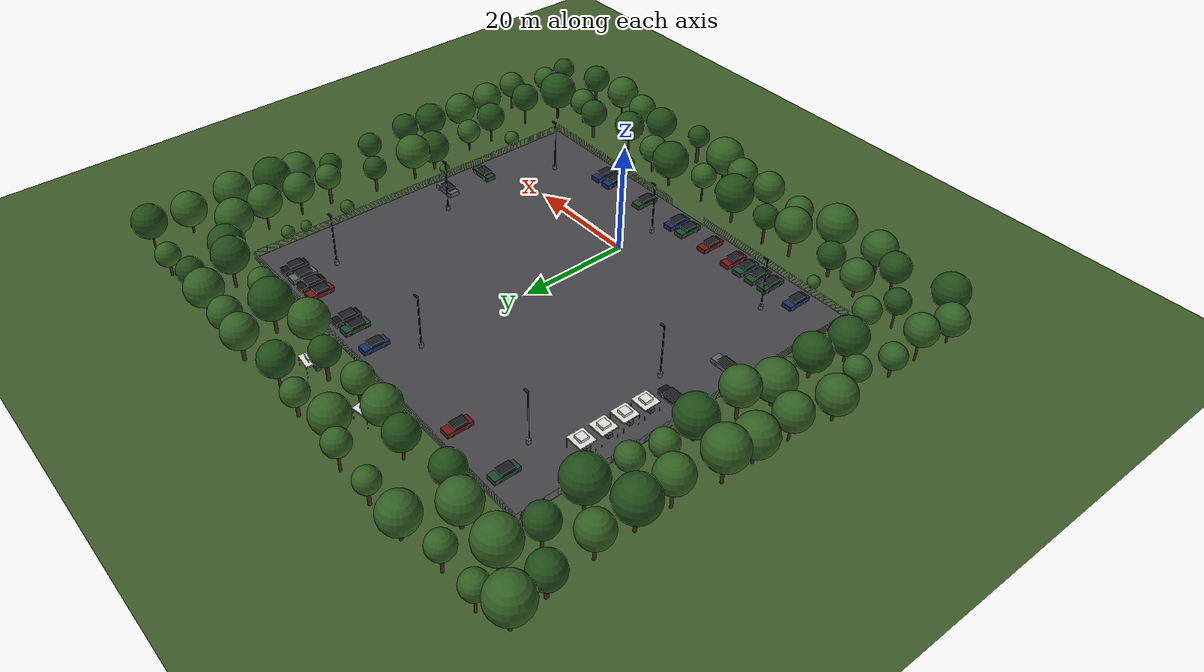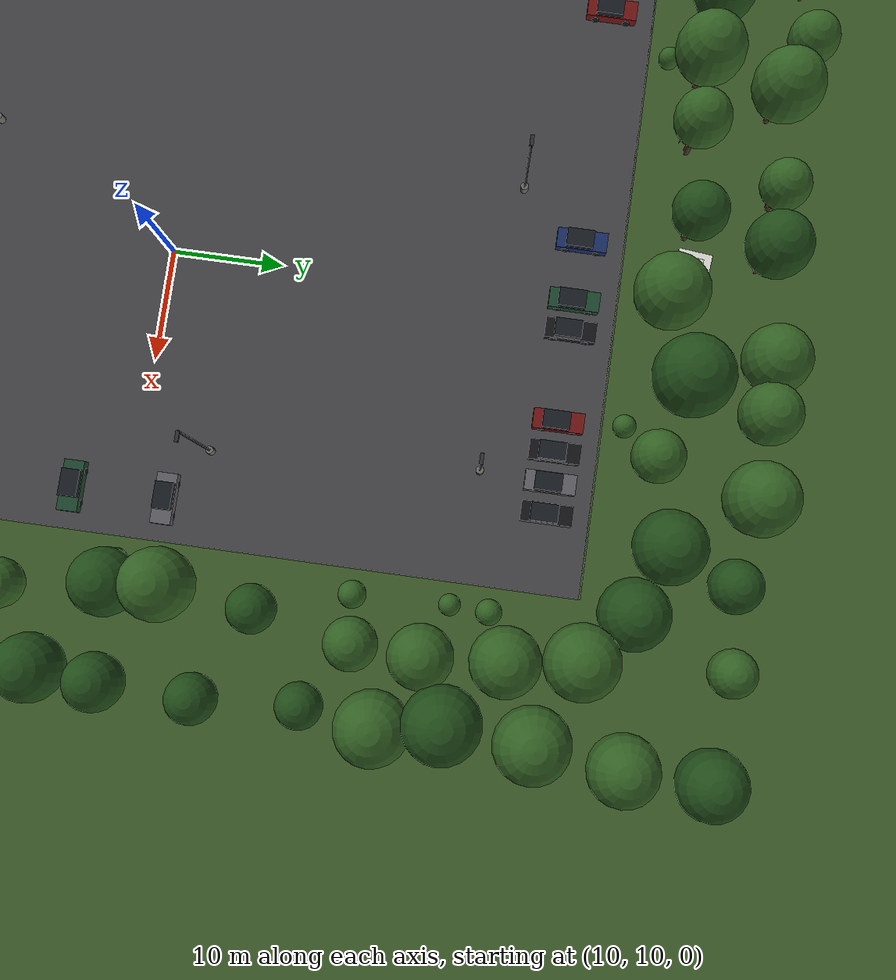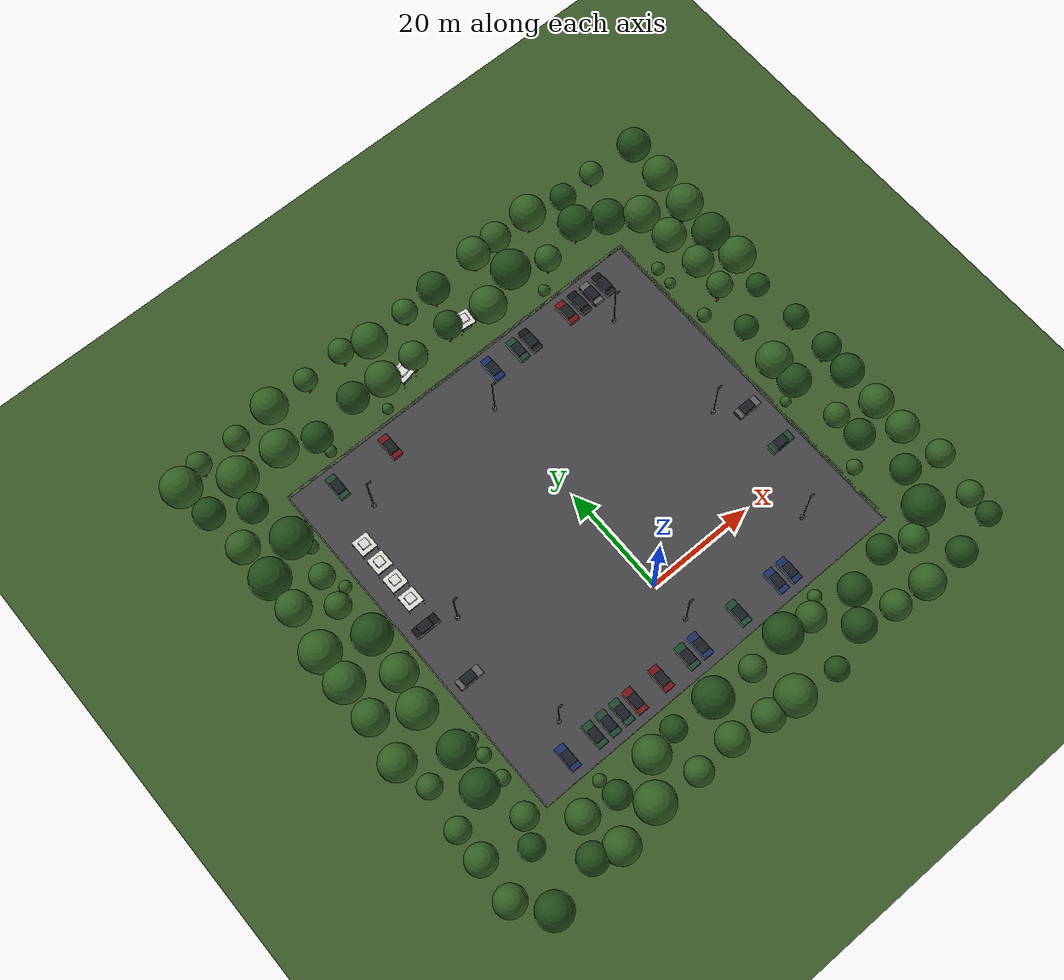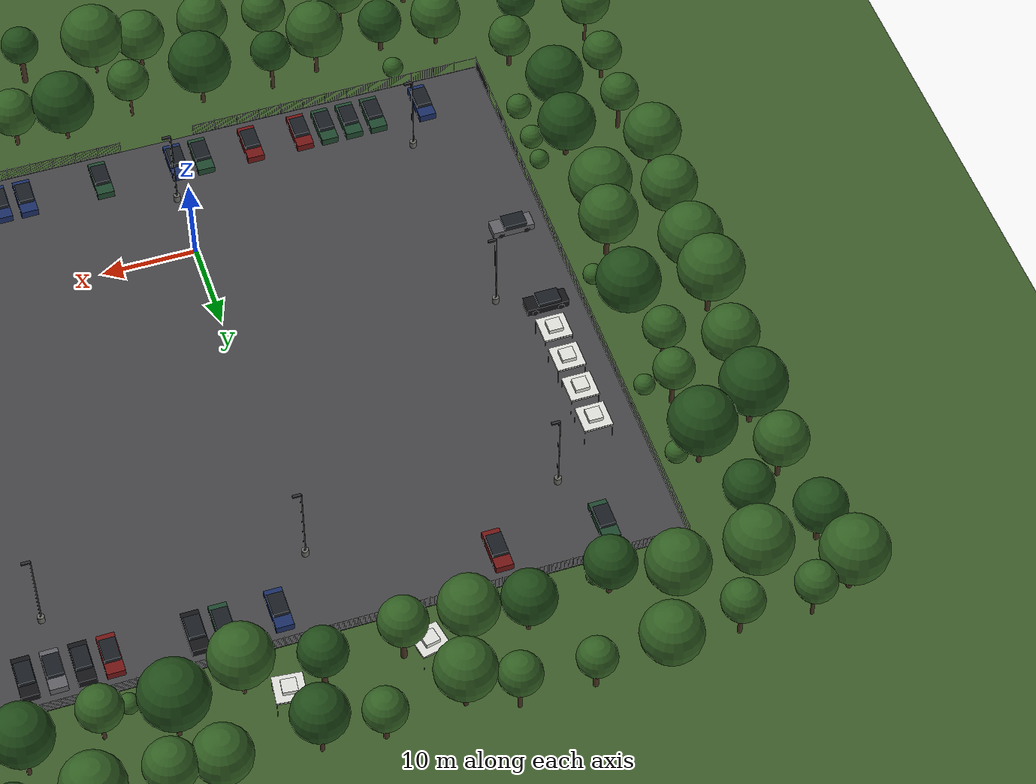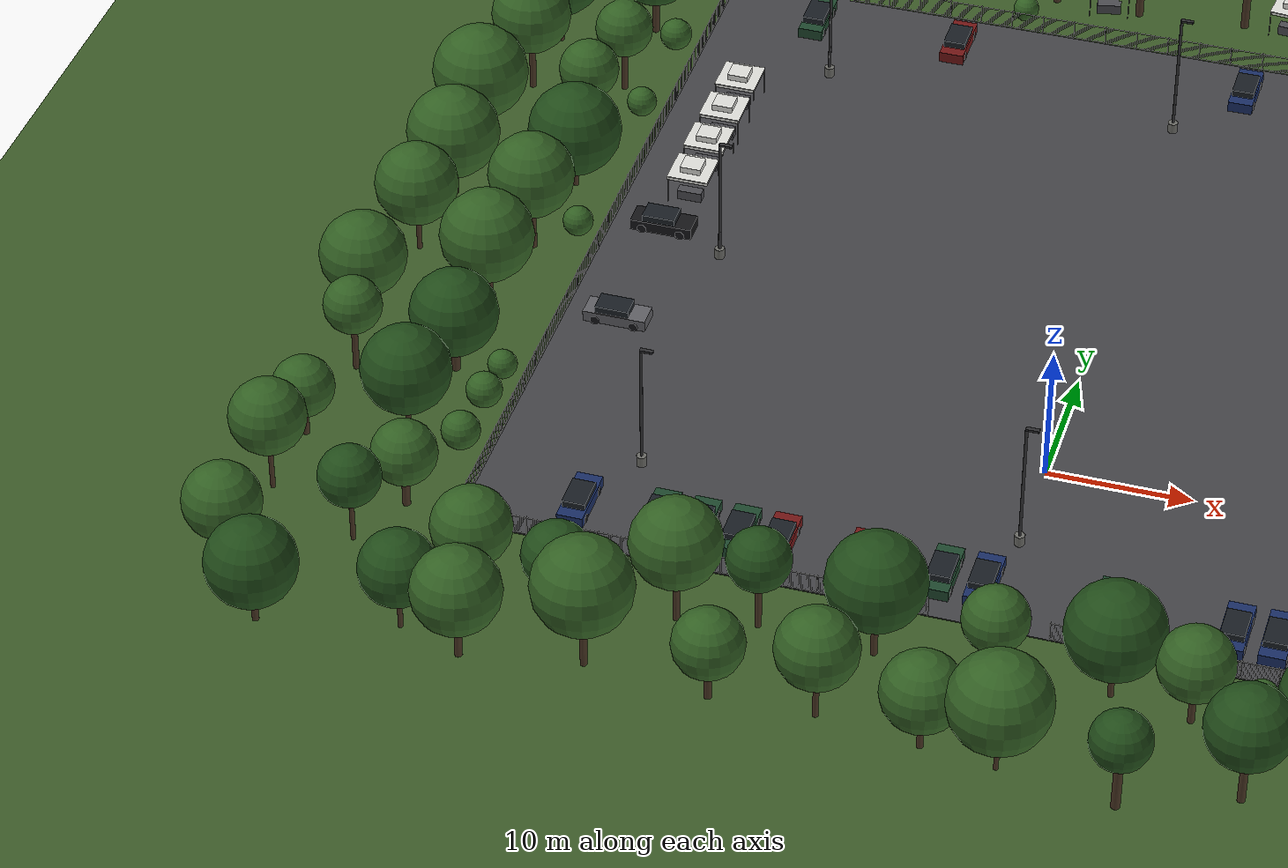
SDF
<?xml version="1.0"?>
<!-- GENERATED by tools/generate_carpark_world.py - edit the layout there, not here. -->
<sdf version="1.6">
  <model name="esda_carpark">
    <static>true</static>
    <!--ground-->
    <link name="ground">
      <pose>0.000 17.000 0 0 0 0</pose>
      <visual name="grass">
        <pose>0 0 -0.02 0 0 0</pose>
        <cast_shadows>false</cast_shadows>
        <geometry><plane><normal>0 0 1</normal><size>120.000 114.000</size></plane></geometry>
        <material>
          <ambient>0.24 0.36 0.16 1</ambient>
          <diffuse>0.24 0.36 0.16 1</diffuse>
          <specular>0.05 0.05 0.05 1</specular>
        </material>
      </visual>
      <collision name="collision">
        <geometry><plane><normal>0 0 1</normal><size>120.000 114.000</size></plane></geometry>
        <surface>
          <friction><ode><mu>100</mu><mu2>50</mu2></ode></friction>
          <bounce/>
          <contact><ode/></contact>
        </surface>
      </collision>
    </link>
    <link name="lot">
      <pose>0.000 17.000 -0.01 0 0 0</pose>
      <visual name="asphalt">
        <pose>0 0 0 0 0 0</pose>
        <cast_shadows>false</cast_shadows>
        <geometry><plane><normal>0 0 1</normal><size>72.000 66.000</size></plane></geometry>
        <material>
          <ambient>0.27 0.27 0.28 1</ambient>
          <diffuse>0.27 0.27 0.28 1</diffuse>
          <specular>0.05 0.05 0.05 1</specular>
        </material>
      </visual>
    </link>
    <!--stall lines (visual only)-->
    <link name="stall_lines">
      <pose>0 0 0 0 0 0</pose>
      <visual name="stall_south_back">
        <pose>0.173 -15.000 0.003 0 0 0</pose>
        <cast_shadows>false</cast_shadows>
        <geometry><plane><normal>0 0 1</normal><size>60.346 0.100</size></plane></geometry>
        <material>
          <ambient>0.50 0.42 0.08 1</ambient>
          <diffuse>0.50 0.42 0.08 1</diffuse>
          <specular>0.05 0.05 0.05 1</specular>
        </material>
      </visual>
      <visual name="stall_south_0">
        <pose>-30.000 -12.250 0.003 0 0 0</pose>
        <cast_shadows>false</cast_shadows>
        <geometry><plane><normal>0 0 1</normal><size>0.100 5.500</size></plane></geometry>
        <material>
          <ambient>0.50 0.42 0.08 1</ambient>
          <diffuse>0.50 0.42 0.08 1</diffuse>
          <specular>0.05 0.05 0.05 1</specular>
        </material>
      </visual>
      <visual name="stall_south_1">
        <pose>-27.257 -12.250 0.003 0 0 0</pose>
        <cast_shadows>false</cast_shadows>
        <geometry><plane><normal>0 0 1</normal><size>0.100 5.500</size></plane></geometry>
        <material>
          <ambient>0.50 0.42 0.08 1</ambient>
          <diffuse>0.50 0.42 0.08 1</diffuse>
          <specular>0.05 0.05 0.05 1</specular>
        </material>
      </visual>
      <visual name="stall_south_2">
        <pose>-24.514 -12.250 0.003 0 0 0</pose>
        <cast_shadows>false</cast_shadows>
        <geometry><plane><normal>0 0 1</normal><size>0.100 5.500</size></plane></geometry>
        <material>
          <ambient>0.50 0.42 0.08 1</ambient>
          <diffuse>0.50 0.42 0.08 1</diffuse>
          <specular>0.05 0.05 0.05 1</specular>
        </material>
      </visual>
      <visual name="stall_south_3">
        <pose>-21.771 -12.250 0.003 0 0 0</pose>
        <cast_shadows>false</cast_shadows>
        <geometry><plane><normal>0 0 1</normal><size>0.100 5.500</size></plane></geometry>
        <material>
          <ambient>0.50 0.42 0.08 1</ambient>
          <diffuse>0.50 0.42 0.08 1</diffuse>
          <specular>0.05 0.05 0.05 1</specular>
        </material>
      </visual>
      <visual name="stall_south_4">
        <pose>-19.028 -12.250 0.003 0 0 0</pose>
        <cast_shadows>false</cast_shadows>
        <geometry><plane><normal>0 0 1</normal><size>0.100 5.500</size></plane></geometry>
        <material>
          <ambient>0.50 0.42 0.08 1</ambient>
          <diffuse>0.50 0.42 0.08 1</diffuse>
          <specular>0.05 0.05 0.05 1</specular>
        </material>
      </visual>
      <visual name="stall_south_5">
        <pose>-16.285 -12.250 0.003 0 0 0</pose>
        <cast_shadows>false</cast_shadows>
        <geometry><plane><normal>0 0 1</normal><size>0.100 5.500</size></plane></geometry>
        <material>
          <ambient>0.50 0.42 0.08 1</ambient>
          <diffuse>0.50 0.42 0.08 1</diffuse>
          <specular>0.05 0.05 0.05 1</specular>
        </material>
      </visual>
      <visual name="stall_south_6">
        <pose>-13.542 -12.250 0.003 0 0 0</pose>
        <cast_shadows>false</cast_shadows>
        <geometry><plane><normal>0 0 1</normal><size>0.100 5.500</size></plane></geometry>
        <material>
          <ambient>0.50 0.42 0.08 1</ambient>
          <diffuse>0.50 0.42 0.08 1</diffuse>
          <specular>0.05 0.05 0.05 1</specular>
        </material>
      </visual>
      <visual name="stall_south_7">
        <pose>-10.799 -12.250 0.003 0 0 0</pose>
        <cast_shadows>false</cast_shadows>
        <geometry><plane><normal>0 0 1</normal><size>0.100 5.500</size></plane></geometry>
        <material>
          <ambient>0.50 0.42 0.08 1</ambient>
          <diffuse>0.50 0.42 0.08 1</diffuse>
          <specular>0.05 0.05 0.05 1</specular>
        </material>
      </visual>
      <visual name="stall_south_8">
        <pose>-8.056 -12.250 0.003 0 0 0</pose>
        <cast_shadows>false</cast_shadows>
        <geometry><plane><normal>0 0 1</normal><size>0.100 5.500</size></plane></geometry>
        <material>
          <ambient>0.50 0.42 0.08 1</ambient>
          <diffuse>0.50 0.42 0.08 1</diffuse>
          <specular>0.05 0.05 0.05 1</specular>
        </material>
      </visual>
      <visual name="stall_south_9">
        <pose>-5.313 -12.250 0.003 0 0 0</pose>
        <cast_shadows>false</cast_shadows>
        <geometry><plane><normal>0 0 1</normal><size>0.100 5.500</size></plane></geometry>
        <material>
          <ambient>0.50 0.42 0.08 1</ambient>
          <diffuse>0.50 0.42 0.08 1</diffuse>
          <specular>0.05 0.05 0.05 1</specular>
        </material>
      </visual>
      <visual name="stall_south_10">
        <pose>-2.570 -12.250 0.003 0 0 0</pose>
        <cast_shadows>false</cast_shadows>
        <geometry><plane><normal>0 0 1</normal><size>0.100 5.500</size></plane></geometry>
        <material>
          <ambient>0.50 0.42 0.08 1</ambient>
          <diffuse>0.50 0.42 0.08 1</diffuse>
          <specular>0.05 0.05 0.05 1</specular>
        </material>
      </visual>
      <visual name="stall_south_11">
        <pose>0.173 -12.250 0.003 0 0 0</pose>
        <cast_shadows>false</cast_shadows>
        <geometry><plane><normal>0 0 1</normal><size>0.100 5.500</size></plane></geometry>
        <material>
          <ambient>0.50 0.42 0.08 1</ambient>
          <diffuse>0.50 0.42 0.08 1</diffuse>
          <specular>0.05 0.05 0.05 1</specular>
        </material>
      </visual>
      <visual name="stall_south_12">
        <pose>2.916 -12.250 0.003 0 0 0</pose>
        <cast_shadows>false</cast_shadows>
        <geometry><plane><normal>0 0 1</normal><size>0.100 5.500</size></plane></geometry>
        <material>
          <ambient>0.50 0.42 0.08 1</ambient>
          <diffuse>0.50 0.42 0.08 1</diffuse>
          <specular>0.05 0.05 0.05 1</specular>
        </material>
      </visual>
      <visual name="stall_south_13">
        <pose>5.659 -12.250 0.003 0 0 0</pose>
        <cast_shadows>false</cast_shadows>
        <geometry><plane><normal>0 0 1</normal><size>0.100 5.500</size></plane></geometry>
        <material>
          <ambient>0.50 0.42 0.08 1</ambient>
          <diffuse>0.50 0.42 0.08 1</diffuse>
          <specular>0.05 0.05 0.05 1</specular>
        </material>
      </visual>
      <visual name="stall_south_14">
        <pose>8.402 -12.250 0.003 0 0 0</pose>
        <cast_shadows>false</cast_shadows>
        <geometry><plane><normal>0 0 1</normal><size>0.100 5.500</size></plane></geometry>
        <material>
          <ambient>0.50 0.42 0.08 1</ambient>
          <diffuse>0.50 0.42 0.08 1</diffuse>
          <specular>0.05 0.05 0.05 1</specular>
        </material>
      </visual>
      <visual name="stall_south_15">
        <pose>11.145 -12.250 0.003 0 0 0</pose>
        <cast_shadows>false</cast_shadows>
        <geometry><plane><normal>0 0 1</normal><size>0.100 5.500</size></plane></geometry>
        <material>
          <ambient>0.50 0.42 0.08 1</ambient>
          <diffuse>0.50 0.42 0.08 1</diffuse>
          <specular>0.05 0.05 0.05 1</specular>
        </material>
      </visual>
      <visual name="stall_south_16">
        <pose>13.888 -12.250 0.003 0 0 0</pose>
        <cast_shadows>false</cast_shadows>
        <geometry><plane><normal>0 0 1</normal><size>0.100 5.500</size></plane></geometry>
        <material>
          <ambient>0.50 0.42 0.08 1</ambient>
          <diffuse>0.50 0.42 0.08 1</diffuse>
          <specular>0.05 0.05 0.05 1</specular>
        </material>
      </visual>
      <visual name="stall_south_17">
        <pose>16.631 -12.250 0.003 0 0 0</pose>
        <cast_shadows>false</cast_shadows>
        <geometry><plane><normal>0 0 1</normal><size>0.100 5.500</size></plane></geometry>
        <material>
          <ambient>0.50 0.42 0.08 1</ambient>
          <diffuse>0.50 0.42 0.08 1</diffuse>
          <specular>0.05 0.05 0.05 1</specular>
        </material>
      </visual>
      <visual name="stall_south_18">
        <pose>19.374 -12.250 0.003 0 0 0</pose>
        <cast_shadows>false</cast_shadows>
        <geometry><plane><normal>0 0 1</normal><size>0.100 5.500</size></plane></geometry>
        <material>
          <ambient>0.50 0.42 0.08 1</ambient>
          <diffuse>0.50 0.42 0.08 1</diffuse>
          <specular>0.05 0.05 0.05 1</specular>
        </material>
      </visual>
      <visual name="stall_south_19">
        <pose>22.117 -12.250 0.003 0 0 0</pose>
        <cast_shadows>false</cast_shadows>
        <geometry><plane><normal>0 0 1</normal><size>0.100 5.500</size></plane></geometry>
        <material>
          <ambient>0.50 0.42 0.08 1</ambient>
          <diffuse>0.50 0.42 0.08 1</diffuse>
          <specular>0.05 0.05 0.05 1</specular>
        </material>
      </visual>
      <visual name="stall_south_20">
        <pose>24.860 -12.250 0.003 0 0 0</pose>
        <cast_shadows>false</cast_shadows>
        <geometry><plane><normal>0 0 1</normal><size>0.100 5.500</size></plane></geometry>
        <material>
          <ambient>0.50 0.42 0.08 1</ambient>
          <diffuse>0.50 0.42 0.08 1</diffuse>
          <specular>0.05 0.05 0.05 1</specular>
        </material>
      </visual>
      <visual name="stall_south_21">
        <pose>27.603 -12.250 0.003 0 0 0</pose>
        <cast_shadows>false</cast_shadows>
        <geometry><plane><normal>0 0 1</normal><size>0.100 5.500</size></plane></geometry>
        <material>
          <ambient>0.50 0.42 0.08 1</ambient>
          <diffuse>0.50 0.42 0.08 1</diffuse>
          <specular>0.05 0.05 0.05 1</specular>
        </material>
      </visual>
      <visual name="stall_south_22">
        <pose>30.346 -12.250 0.003 0 0 0</pose>
        <cast_shadows>false</cast_shadows>
        <geometry><plane><normal>0 0 1</normal><size>0.100 5.500</size></plane></geometry>
        <material>
          <ambient>0.50 0.42 0.08 1</ambient>
          <diffuse>0.50 0.42 0.08 1</diffuse>
          <specular>0.05 0.05 0.05 1</specular>
        </material>
      </visual>
      <visual name="stall_north_back">
        <pose>0.173 49.000 0.003 0 0 0</pose>
        <cast_shadows>false</cast_shadows>
        <geometry><plane><normal>0 0 1</normal><size>60.346 0.100</size></plane></geometry>
        <material>
          <ambient>0.50 0.42 0.08 1</ambient>
          <diffuse>0.50 0.42 0.08 1</diffuse>
          <specular>0.05 0.05 0.05 1</specular>
        </material>
      </visual>
      <visual name="stall_north_0">
        <pose>-30.000 46.250 0.003 0 0 0</pose>
        <cast_shadows>false</cast_shadows>
        <geometry><plane><normal>0 0 1</normal><size>0.100 5.500</size></plane></geometry>
        <material>
          <ambient>0.50 0.42 0.08 1</ambient>
          <diffuse>0.50 0.42 0.08 1</diffuse>
          <specular>0.05 0.05 0.05 1</specular>
        </material>
      </visual>
      <visual name="stall_north_1">
        <pose>-27.257 46.250 0.003 0 0 0</pose>
        <cast_shadows>false</cast_shadows>
        <geometry><plane><normal>0 0 1</normal><size>0.100 5.500</size></plane></geometry>
        <material>
          <ambient>0.50 0.42 0.08 1</ambient>
          <diffuse>0.50 0.42 0.08 1</diffuse>
          <specular>0.05 0.05 0.05 1</specular>
        </material>
      </visual>
      <visual name="stall_north_2">
        <pose>-24.514 46.250 0.003 0 0 0</pose>
        <cast_shadows>false</cast_shadows>
        <geometry><plane><normal>0 0 1</normal><size>0.100 5.500</size></plane></geometry>
        <material>
          <ambient>0.50 0.42 0.08 1</ambient>
          <diffuse>0.50 0.42 0.08 1</diffuse>
          <specular>0.05 0.05 0.05 1</specular>
        </material>
      </visual>
      <visual name="stall_north_3">
        <pose>-21.771 46.250 0.003 0 0 0</pose>
        <cast_shadows>false</cast_shadows>
        <geometry><plane><normal>0 0 1</normal><size>0.100 5.500</size></plane></geometry>
        <material>
          <ambient>0.50 0.42 0.08 1</ambient>
          <diffuse>0.50 0.42 0.08 1</diffuse>
          <specular>0.05 0.05 0.05 1</specular>
        </material>
      </visual>
      <visual name="stall_north_4">
        <pose>-19.028 46.250 0.003 0 0 0</pose>
        <cast_shadows>false</cast_shadows>
        <geometry><plane><normal>0 0 1</normal><size>0.100 5.500</size></plane></geometry>
        <material>
          <ambient>0.50 0.42 0.08 1</ambient>
          <diffuse>0.50 0.42 0.08 1</diffuse>
          <specular>0.05 0.05 0.05 1</specular>
        </material>
      </visual>
      <visual name="stall_north_5">
        <pose>-16.285 46.250 0.003 0 0 0</pose>
        <cast_shadows>false</cast_shadows>
        <geometry><plane><normal>0 0 1</normal><size>0.100 5.500</size></plane></geometry>
        <material>
          <ambient>0.50 0.42 0.08 1</ambient>
          <diffuse>0.50 0.42 0.08 1</diffuse>
          <specular>0.05 0.05 0.05 1</specular>
        </material>
      </visual>
      <visual name="stall_north_6">
        <pose>-13.542 46.250 0.003 0 0 0</pose>
        <cast_shadows>false</cast_shadows>
        <geometry><plane><normal>0 0 1</normal><size>0.100 5.500</size></plane></geometry>
        <material>
          <ambient>0.50 0.42 0.08 1</ambient>
          <diffuse>0.50 0.42 0.08 1</diffuse>
          <specular>0.05 0.05 0.05 1</specular>
        </material>
      </visual>
      <visual name="stall_north_7">
        <pose>-10.799 46.250 0.003 0 0 0</pose>
        <cast_shadows>false</cast_shadows>
        <geometry><plane><normal>0 0 1</normal><size>0.100 5.500</size></plane></geometry>
        <material>
          <ambient>0.50 0.42 0.08 1</ambient>
          <diffuse>0.50 0.42 0.08 1</diffuse>
          <specular>0.05 0.05 0.05 1</specular>
        </material>
      </visual>
      <visual name="stall_north_8">
        <pose>-8.056 46.250 0.003 0 0 0</pose>
        <cast_shadows>false</cast_shadows>
        <geometry><plane><normal>0 0 1</normal><size>0.100 5.500</size></plane></geometry>
        <material>
          <ambient>0.50 0.42 0.08 1</ambient>
          <diffuse>0.50 0.42 0.08 1</diffuse>
          <specular>0.05 0.05 0.05 1</specular>
        </material>
      </visual>
      <visual name="stall_north_9">
        <pose>-5.313 46.250 0.003 0 0 0</pose>
        <cast_shadows>false</cast_shadows>
        <geometry><plane><normal>0 0 1</normal><size>0.100 5.500</size></plane></geometry>
        <material>
          <ambient>0.50 0.42 0.08 1</ambient>
          <diffuse>0.50 0.42 0.08 1</diffuse>
          <specular>0.05 0.05 0.05 1</specular>
        </material>
      </visual>
      <visual name="stall_north_10">
        <pose>-2.570 46.250 0.003 0 0 0</pose>
        <cast_shadows>false</cast_shadows>
        <geometry><plane><normal>0 0 1</normal><size>0.100 5.500</size></plane></geometry>
        <material>
          <ambient>0.50 0.42 0.08 1</ambient>
          <diffuse>0.50 0.42 0.08 1</diffuse>
          <specular>0.05 0.05 0.05 1</specular>
        </material>
      </visual>
      <visual name="stall_north_11">
        <pose>0.173 46.250 0.003 0 0 0</pose>
        <cast_shadows>false</cast_shadows>
        <geometry><plane><normal>0 0 1</normal><size>0.100 5.500</size></plane></geometry>
        <material>
          <ambient>0.50 0.42 0.08 1</ambient>
          <diffuse>0.50 0.42 0.08 1</diffuse>
          <specular>0.05 0.05 0.05 1</specular>
        </material>
      </visual>
      <visual name="stall_north_12">
        <pose>2.916 46.250 0.003 0 0 0</pose>
        <cast_shadows>false</cast_shadows>
        <geometry><plane><normal>0 0 1</normal><size>0.100 5.500</size></plane></geometry>
        <material>
          <ambient>0.50 0.42 0.08 1</ambient>
          <diffuse>0.50 0.42 0.08 1</diffuse>
          <specular>0.05 0.05 0.05 1</specular>
        </material>
      </visual>
      <visual name="stall_north_13">
        <pose>5.659 46.250 0.003 0 0 0</pose>
        <cast_shadows>false</cast_shadows>
        <geometry><plane><normal>0 0 1</normal><size>0.100 5.500</size></plane></geometry>
        <material>
          <ambient>0.50 0.42 0.08 1</ambient>
          <diffuse>0.50 0.42 0.08 1</diffuse>
          <specular>0.05 0.05 0.05 1</specular>
        </material>
      </visual>
      <visual name="stall_north_14">
        <pose>8.402 46.250 0.003 0 0 0</pose>
        <cast_shadows>false</cast_shadows>
        <geometry><plane><normal>0 0 1</normal><size>0.100 5.500</size></plane></geometry>
        <material>
          <ambient>0.50 0.42 0.08 1</ambient>
          <diffuse>0.50 0.42 0.08 1</diffuse>
          <specular>0.05 0.05 0.05 1</specular>
        </material>
      </visual>
      <visual name="stall_north_15">
        <pose>11.145 46.250 0.003 0 0 0</pose>
        <cast_shadows>false</cast_shadows>
        <geometry><plane><normal>0 0 1</normal><size>0.100 5.500</size></plane></geometry>
        <material>
          <ambient>0.50 0.42 0.08 1</ambient>
          <diffuse>0.50 0.42 0.08 1</diffuse>
          <specular>0.05 0.05 0.05 1</specular>
        </material>
      </visual>
      <visual name="stall_north_16">
        <pose>13.888 46.250 0.003 0 0 0</pose>
        <cast_shadows>false</cast_shadows>
        <geometry><plane><normal>0 0 1</normal><size>0.100 5.500</size></plane></geometry>
        <material>
          <ambient>0.50 0.42 0.08 1</ambient>
          <diffuse>0.50 0.42 0.08 1</diffuse>
          <specular>0.05 0.05 0.05 1</specular>
        </material>
      </visual>
      <visual name="stall_north_17">
        <pose>16.631 46.250 0.003 0 0 0</pose>
        <cast_shadows>false</cast_shadows>
        <geometry><plane><normal>0 0 1</normal><size>0.100 5.500</size></plane></geometry>
        <material>
          <ambient>0.50 0.42 0.08 1</ambient>
          <diffuse>0.50 0.42 0.08 1</diffuse>
          <specular>0.05 0.05 0.05 1</specular>
        </material>
      </visual>
      <visual name="stall_north_18">
        <pose>19.374 46.250 0.003 0 0 0</pose>
        <cast_shadows>false</cast_shadows>
        <geometry><plane><normal>0 0 1</normal><size>0.100 5.500</size></plane></geometry>
        <material>
          <ambient>0.50 0.42 0.08 1</ambient>
          <diffuse>0.50 0.42 0.08 1</diffuse>
          <specular>0.05 0.05 0.05 1</specular>
        </material>
      </visual>
      <visual name="stall_north_19">
        <pose>22.117 46.250 0.003 0 0 0</pose>
        <cast_shadows>false</cast_shadows>
        <geometry><plane><normal>0 0 1</normal><size>0.100 5.500</size></plane></geometry>
        <material>
          <ambient>0.50 0.42 0.08 1</ambient>
          <diffuse>0.50 0.42 0.08 1</diffuse>
          <specular>0.05 0.05 0.05 1</specular>
        </material>
      </visual>
      <visual name="stall_north_20">
        <pose>24.860 46.250 0.003 0 0 0</pose>
        <cast_shadows>false</cast_shadows>
        <geometry><plane><normal>0 0 1</normal><size>0.100 5.500</size></plane></geometry>
        <material>
          <ambient>0.50 0.42 0.08 1</ambient>
          <diffuse>0.50 0.42 0.08 1</diffuse>
          <specular>0.05 0.05 0.05 1</specular>
        </material>
      </visual>
      <visual name="stall_north_21">
        <pose>27.603 46.250 0.003 0 0 0</pose>
        <cast_shadows>false</cast_shadows>
        <geometry><plane><normal>0 0 1</normal><size>0.100 5.500</size></plane></geometry>
        <material>
          <ambient>0.50 0.42 0.08 1</ambient>
          <diffuse>0.50 0.42 0.08 1</diffuse>
          <specular>0.05 0.05 0.05 1</specular>
        </material>
      </visual>
      <visual name="stall_north_22">
        <pose>30.346 46.250 0.003 0 0 0</pose>
        <cast_shadows>false</cast_shadows>
        <geometry><plane><normal>0 0 1</normal><size>0.100 5.500</size></plane></geometry>
        <material>
          <ambient>0.50 0.42 0.08 1</ambient>
          <diffuse>0.50 0.42 0.08 1</diffuse>
          <specular>0.05 0.05 0.05 1</specular>
        </material>
      </visual>
      <visual name="stall_east_back">
        <pose>35.000 15.829 0.003 0 0 0</pose>
        <cast_shadows>false</cast_shadows>
        <geometry><plane><normal>0 0 1</normal><size>0.100 35.659</size></plane></geometry>
        <material>
          <ambient>0.50 0.42 0.08 1</ambient>
          <diffuse>0.50 0.42 0.08 1</diffuse>
          <specular>0.05 0.05 0.05 1</specular>
        </material>
      </visual>
      <visual name="stall_east_0">
        <pose>32.250 -2.000 0.003 0 0 0</pose>
        <cast_shadows>false</cast_shadows>
        <geometry><plane><normal>0 0 1</normal><size>5.500 0.100</size></plane></geometry>
        <material>
          <ambient>0.50 0.42 0.08 1</ambient>
          <diffuse>0.50 0.42 0.08 1</diffuse>
          <specular>0.05 0.05 0.05 1</specular>
        </material>
      </visual>
      <visual name="stall_east_1">
        <pose>32.250 0.743 0.003 0 0 0</pose>
        <cast_shadows>false</cast_shadows>
        <geometry><plane><normal>0 0 1</normal><size>5.500 0.100</size></plane></geometry>
        <material>
          <ambient>0.50 0.42 0.08 1</ambient>
          <diffuse>0.50 0.42 0.08 1</diffuse>
          <specular>0.05 0.05 0.05 1</specular>
        </material>
      </visual>
      <visual name="stall_east_2">
        <pose>32.250 3.486 0.003 0 0 0</pose>
        <cast_shadows>false</cast_shadows>
        <geometry><plane><normal>0 0 1</normal><size>5.500 0.100</size></plane></geometry>
        <material>
          <ambient>0.50 0.42 0.08 1</ambient>
          <diffuse>0.50 0.42 0.08 1</diffuse>
          <specular>0.05 0.05 0.05 1</specular>
        </material>
      </visual>
      <visual name="stall_east_3">
        <pose>32.250 6.229 0.003 0 0 0</pose>
        <cast_shadows>false</cast_shadows>
        <geometry><plane><normal>0 0 1</normal><size>5.500 0.100</size></plane></geometry>
        <material>
          <ambient>0.50 0.42 0.08 1</ambient>
          <diffuse>0.50 0.42 0.08 1</diffuse>
          <specular>0.05 0.05 0.05 1</specular>
        </material>
      </visual>
      <visual name="stall_east_4">
        <pose>32.250 8.972 0.003 0 0 0</pose>
        <cast_shadows>false</cast_shadows>
        <geometry><plane><normal>0 0 1</normal><size>5.500 0.100</size></plane></geometry>
        <material>
          <ambient>0.50 0.42 0.08 1</ambient>
          <diffuse>0.50 0.42 0.08 1</diffuse>
          <specular>0.05 0.05 0.05 1</specular>
        </material>
      </visual>
      <visual name="stall_east_5">
        <pose>32.250 11.715 0.003 0 0 0</pose>
        <cast_shadows>false</cast_shadows>
        <geometry><plane><normal>0 0 1</normal><size>5.500 0.100</size></plane></geometry>
        <material>
          <ambient>0.50 0.42 0.08 1</ambient>
          <diffuse>0.50 0.42 0.08 1</diffuse>
          <specular>0.05 0.05 0.05 1</specular>
        </material>
      </visual>
      <visual name="stall_east_6">
        <pose>32.250 14.458 0.003 0 0 0</pose>
        <cast_shadows>false</cast_shadows>
        <geometry><plane><normal>0 0 1</normal><size>5.500 0.100</size></plane></geometry>
        <material>
          <ambient>0.50 0.42 0.08 1</ambient>
          <diffuse>0.50 0.42 0.08 1</diffuse>
          <specular>0.05 0.05 0.05 1</specular>
        </material>
      </visual>
      <visual name="stall_east_7">
        <pose>32.250 17.201 0.003 0 0 0</pose>
        <cast_shadows>false</cast_shadows>
        <geometry><plane><normal>0 0 1</normal><size>5.500 0.100</size></plane></geometry>
        <material>
          <ambient>0.50 0.42 0.08 1</ambient>
          <diffuse>0.50 0.42 0.08 1</diffuse>
          <specular>0.05 0.05 0.05 1</specular>
        </material>
      </visual>
      <visual name="stall_east_8">
        <pose>32.250 19.944 0.003 0 0 0</pose>
        <cast_shadows>false</cast_shadows>
        <geometry><plane><normal>0 0 1</normal><size>5.500 0.100</size></plane></geometry>
        <material>
          <ambient>0.50 0.42 0.08 1</ambient>
          <diffuse>0.50 0.42 0.08 1</diffuse>
          <specular>0.05 0.05 0.05 1</specular>
        </material>
      </visual>
      <visual name="stall_east_9">
        <pose>32.250 22.687 0.003 0 0 0</pose>
        <cast_shadows>false</cast_shadows>
        <geometry><plane><normal>0 0 1</normal><size>5.500 0.100</size></plane></geometry>
        <material>
          <ambient>0.50 0.42 0.08 1</ambient>
          <diffuse>0.50 0.42 0.08 1</diffuse>
          <specular>0.05 0.05 0.05 1</specular>
        </material>
      </visual>
      <visual name="stall_east_10">
        <pose>32.250 25.430 0.003 0 0 0</pose>
        <cast_shadows>false</cast_shadows>
        <geometry><plane><normal>0 0 1</normal><size>5.500 0.100</size></plane></geometry>
        <material>
          <ambient>0.50 0.42 0.08 1</ambient>
          <diffuse>0.50 0.42 0.08 1</diffuse>
          <specular>0.05 0.05 0.05 1</specular>
        </material>
      </visual>
      <visual name="stall_east_11">
        <pose>32.250 28.173 0.003 0 0 0</pose>
        <cast_shadows>false</cast_shadows>
        <geometry><plane><normal>0 0 1</normal><size>5.500 0.100</size></plane></geometry>
        <material>
          <ambient>0.50 0.42 0.08 1</ambient>
          <diffuse>0.50 0.42 0.08 1</diffuse>
          <specular>0.05 0.05 0.05 1</specular>
        </material>
      </visual>
      <visual name="stall_east_12">
        <pose>32.250 30.916 0.003 0 0 0</pose>
        <cast_shadows>false</cast_shadows>
        <geometry><plane><normal>0 0 1</normal><size>5.500 0.100</size></plane></geometry>
        <material>
          <ambient>0.50 0.42 0.08 1</ambient>
          <diffuse>0.50 0.42 0.08 1</diffuse>
          <specular>0.05 0.05 0.05 1</specular>
        </material>
      </visual>
      <visual name="stall_east_13">
        <pose>32.250 33.659 0.003 0 0 0</pose>
        <cast_shadows>false</cast_shadows>
        <geometry><plane><normal>0 0 1</normal><size>5.500 0.100</size></plane></geometry>
        <material>
          <ambient>0.50 0.42 0.08 1</ambient>
          <diffuse>0.50 0.42 0.08 1</diffuse>
          <specular>0.05 0.05 0.05 1</specular>
        </material>
      </visual>
      <visual name="stall_west_back">
        <pose>-35.000 12.857 0.003 0 0 0</pose>
        <cast_shadows>false</cast_shadows>
        <geometry><plane><normal>0 0 1</normal><size>0.100 13.715</size></plane></geometry>
        <material>
          <ambient>0.50 0.42 0.08 1</ambient>
          <diffuse>0.50 0.42 0.08 1</diffuse>
          <specular>0.05 0.05 0.05 1</specular>
        </material>
      </visual>
      <visual name="stall_west_0">
        <pose>-32.250 6.000 0.003 0 0 0</pose>
        <cast_shadows>false</cast_shadows>
        <geometry><plane><normal>0 0 1</normal><size>5.500 0.100</size></plane></geometry>
        <material>
          <ambient>0.50 0.42 0.08 1</ambient>
          <diffuse>0.50 0.42 0.08 1</diffuse>
          <specular>0.05 0.05 0.05 1</specular>
        </material>
      </visual>
      <visual name="stall_west_1">
        <pose>-32.250 8.743 0.003 0 0 0</pose>
        <cast_shadows>false</cast_shadows>
        <geometry><plane><normal>0 0 1</normal><size>5.500 0.100</size></plane></geometry>
        <material>
          <ambient>0.50 0.42 0.08 1</ambient>
          <diffuse>0.50 0.42 0.08 1</diffuse>
          <specular>0.05 0.05 0.05 1</specular>
        </material>
      </visual>
      <visual name="stall_west_2">
        <pose>-32.250 11.486 0.003 0 0 0</pose>
        <cast_shadows>false</cast_shadows>
        <geometry><plane><normal>0 0 1</normal><size>5.500 0.100</size></plane></geometry>
        <material>
          <ambient>0.50 0.42 0.08 1</ambient>
          <diffuse>0.50 0.42 0.08 1</diffuse>
          <specular>0.05 0.05 0.05 1</specular>
        </material>
      </visual>
      <visual name="stall_west_3">
        <pose>-32.250 14.229 0.003 0 0 0</pose>
        <cast_shadows>false</cast_shadows>
        <geometry><plane><normal>0 0 1</normal><size>5.500 0.100</size></plane></geometry>
        <material>
          <ambient>0.50 0.42 0.08 1</ambient>
          <diffuse>0.50 0.42 0.08 1</diffuse>
          <specular>0.05 0.05 0.05 1</specular>
        </material>
      </visual>
      <visual name="stall_west_4">
        <pose>-32.250 16.972 0.003 0 0 0</pose>
        <cast_shadows>false</cast_shadows>
        <geometry><plane><normal>0 0 1</normal><size>5.500 0.100</size></plane></geometry>
        <material>
          <ambient>0.50 0.42 0.08 1</ambient>
          <diffuse>0.50 0.42 0.08 1</diffuse>
          <specular>0.05 0.05 0.05 1</specular>
        </material>
      </visual>
      <visual name="stall_west_5">
        <pose>-32.250 19.715 0.003 0 0 0</pose>
        <cast_shadows>false</cast_shadows>
        <geometry><plane><normal>0 0 1</normal><size>5.500 0.100</size></plane></geometry>
        <material>
          <ambient>0.50 0.42 0.08 1</ambient>
          <diffuse>0.50 0.42 0.08 1</diffuse>
          <specular>0.05 0.05 0.05 1</specular>
        </material>
      </visual>
    </link>
    <!--fence: pickets as one mesh, simple collision walls-->
    <link name="fence">
      <pose>0 0 0 0 0 0</pose>
      <visual name="fence">
        <pose>0 0 0 0 0 0</pose>
        <geometry><mesh><uri>model://esda_carpark/meshes/fence.obj</uri></mesh></geometry>
        <material>
          <ambient>0.06 0.06 0.06 1</ambient>
          <diffuse>0.06 0.06 0.06 1</diffuse>
          <specular>0.05 0.05 0.05 1</specular>
        </material>
      </visual>
      <collision name="fence_wall_0">
        <pose>-20.000 -16.000 0.750 0 0 0.0000</pose>
        <geometry><box><size>32.000 0.050 1.500</size></box></geometry>
      </collision>
      <collision name="fence_wall_1">
        <pose>20.000 -16.000 0.750 0 0 0.0000</pose>
        <geometry><box><size>32.000 0.050 1.500</size></box></geometry>
      </collision>
      <collision name="fence_wall_2">
        <pose>36.000 17.000 0.750 0 0 1.5708</pose>
        <geometry><box><size>66.000 0.050 1.500</size></box></geometry>
      </collision>
      <collision name="fence_wall_3">
        <pose>0.000 50.000 0.750 0 0 3.1416</pose>
        <geometry><box><size>72.000 0.050 1.500</size></box></geometry>
      </collision>
      <collision name="fence_wall_4">
        <pose>-36.000 17.000 0.750 0 0 -1.5708</pose>
        <geometry><box><size>66.000 0.050 1.500</size></box></geometry>
      </collision>
    </link>
    <!--light poles-->
    <link name="pole_sw">
      <pose>-26.0 -7.0 0 0 0 0</pose>
      <visual name="base">
        <pose>0 0 0.4 0 0 0</pose>
        <geometry><cylinder><radius>0.350</radius><length>0.800</length></cylinder></geometry>
        <material>
          <ambient>0.42 0.42 0.40 1</ambient>
          <diffuse>0.42 0.42 0.40 1</diffuse>
          <specular>0.05 0.05 0.05 1</specular>
        </material>
      </visual>
      <collision name="base_collision">
        <pose>0 0 0.4 0 0 0</pose>
        <geometry><cylinder><radius>0.350</radius><length>0.800</length></cylinder></geometry>
      </collision>
      <visual name="pole">
        <pose>0 0 5.3 0 0 0</pose>
        <geometry><cylinder><radius>0.100</radius><length>9.000</length></cylinder></geometry>
        <material>
          <ambient>0.18 0.18 0.19 1</ambient>
          <diffuse>0.18 0.18 0.19 1</diffuse>
          <specular>0.05 0.05 0.05 1</specular>
        </material>
      </visual>
      <collision name="pole_collision">
        <pose>0 0 5.3 0 0 0</pose>
        <geometry><cylinder><radius>0.100</radius><length>9.000</length></cylinder></geometry>
      </collision>
      <visual name="lamp">
        <pose>0.4 0 9.8 0 0 0</pose>
        <geometry><box><size>0.900 0.300 0.150</size></box></geometry>
        <material>
          <ambient>0.18 0.18 0.19 1</ambient>
          <diffuse>0.18 0.18 0.19 1</diffuse>
          <specular>0.05 0.05 0.05 1</specular>
        </material>
      </visual>
    </link>
    <link name="pole_s">
      <pose>0.0 -7.5 0 0 0 0</pose>
      <visual name="base">
        <pose>0 0 0.4 0 0 0</pose>
        <geometry><cylinder><radius>0.350</radius><length>0.800</length></cylinder></geometry>
        <material>
          <ambient>0.42 0.42 0.40 1</ambient>
          <diffuse>0.42 0.42 0.40 1</diffuse>
          <specular>0.05 0.05 0.05 1</specular>
        </material>
      </visual>
      <collision name="base_collision">
        <pose>0 0 0.4 0 0 0</pose>
        <geometry><cylinder><radius>0.350</radius><length>0.800</length></cylinder></geometry>
      </collision>
      <visual name="pole">
        <pose>0 0 5.3 0 0 0</pose>
        <geometry><cylinder><radius>0.100</radius><length>9.000</length></cylinder></geometry>
        <material>
          <ambient>0.18 0.18 0.19 1</ambient>
          <diffuse>0.18 0.18 0.19 1</diffuse>
          <specular>0.05 0.05 0.05 1</specular>
        </material>
      </visual>
      <collision name="pole_collision">
        <pose>0 0 5.3 0 0 0</pose>
        <geometry><cylinder><radius>0.100</radius><length>9.000</length></cylinder></geometry>
      </collision>
      <visual name="lamp">
        <pose>0.4 0 9.8 0 0 0</pose>
        <geometry><box><size>0.900 0.300 0.150</size></box></geometry>
        <material>
          <ambient>0.18 0.18 0.19 1</ambient>
          <diffuse>0.18 0.18 0.19 1</diffuse>
          <specular>0.05 0.05 0.05 1</specular>
        </material>
      </visual>
    </link>
    <link name="pole_se">
      <pose>26.0 -7.0 0 0 0 0</pose>
      <visual name="base">
        <pose>0 0 0.4 0 0 0</pose>
        <geometry><cylinder><radius>0.350</radius><length>0.800</length></cylinder></geometry>
        <material>
          <ambient>0.42 0.42 0.40 1</ambient>
          <diffuse>0.42 0.42 0.40 1</diffuse>
          <specular>0.05 0.05 0.05 1</specular>
        </material>
      </visual>
      <collision name="base_collision">
        <pose>0 0 0.4 0 0 0</pose>
        <geometry><cylinder><radius>0.350</radius><length>0.800</length></cylinder></geometry>
      </collision>
      <visual name="pole">
        <pose>0 0 5.3 0 0 0</pose>
        <geometry><cylinder><radius>0.100</radius><length>9.000</length></cylinder></geometry>
        <material>
          <ambient>0.18 0.18 0.19 1</ambient>
          <diffuse>0.18 0.18 0.19 1</diffuse>
          <specular>0.05 0.05 0.05 1</specular>
        </material>
      </visual>
      <collision name="pole_collision">
        <pose>0 0 5.3 0 0 0</pose>
        <geometry><cylinder><radius>0.100</radius><length>9.000</length></cylinder></geometry>
      </collision>
      <visual name="lamp">
        <pose>0.4 0 9.8 0 0 0</pose>
        <geometry><box><size>0.900 0.300 0.150</size></box></geometry>
        <material>
          <ambient>0.18 0.18 0.19 1</ambient>
          <diffuse>0.18 0.18 0.19 1</diffuse>
          <specular>0.05 0.05 0.05 1</specular>
        </material>
      </visual>
    </link>
    <link name="pole_w">
      <pose>-27.5 16.3 0 0 0 0</pose>
      <visual name="base">
        <pose>0 0 0.4 0 0 0</pose>
        <geometry><cylinder><radius>0.350</radius><length>0.800</length></cylinder></geometry>
        <material>
          <ambient>0.42 0.42 0.40 1</ambient>
          <diffuse>0.42 0.42 0.40 1</diffuse>
          <specular>0.05 0.05 0.05 1</specular>
        </material>
      </visual>
      <collision name="base_collision">
        <pose>0 0 0.4 0 0 0</pose>
        <geometry><cylinder><radius>0.350</radius><length>0.800</length></cylinder></geometry>
      </collision>
      <visual name="pole">
        <pose>0 0 5.3 0 0 0</pose>
        <geometry><cylinder><radius>0.100</radius><length>9.000</length></cylinder></geometry>
        <material>
          <ambient>0.18 0.18 0.19 1</ambient>
          <diffuse>0.18 0.18 0.19 1</diffuse>
          <specular>0.05 0.05 0.05 1</specular>
        </material>
      </visual>
      <collision name="pole_collision">
        <pose>0 0 5.3 0 0 0</pose>
        <geometry><cylinder><radius>0.100</radius><length>9.000</length></cylinder></geometry>
      </collision>
      <visual name="lamp">
        <pose>0.4 0 9.8 0 0 0</pose>
        <geometry><box><size>0.900 0.300 0.150</size></box></geometry>
        <material>
          <ambient>0.18 0.18 0.19 1</ambient>
          <diffuse>0.18 0.18 0.19 1</diffuse>
          <specular>0.05 0.05 0.05 1</specular>
        </material>
      </visual>
    </link>
    <link name="pole_e">
      <pose>27.5 16.3 0 0 0 0</pose>
      <visual name="base">
        <pose>0 0 0.4 0 0 0</pose>
        <geometry><cylinder><radius>0.350</radius><length>0.800</length></cylinder></geometry>
        <material>
          <ambient>0.42 0.42 0.40 1</ambient>
          <diffuse>0.42 0.42 0.40 1</diffuse>
          <specular>0.05 0.05 0.05 1</specular>
        </material>
      </visual>
      <collision name="base_collision">
        <pose>0 0 0.4 0 0 0</pose>
        <geometry><cylinder><radius>0.350</radius><length>0.800</length></cylinder></geometry>
      </collision>
      <visual name="pole">
        <pose>0 0 5.3 0 0 0</pose>
        <geometry><cylinder><radius>0.100</radius><length>9.000</length></cylinder></geometry>
        <material>
          <ambient>0.18 0.18 0.19 1</ambient>
          <diffuse>0.18 0.18 0.19 1</diffuse>
          <specular>0.05 0.05 0.05 1</specular>
        </material>
      </visual>
      <collision name="pole_collision">
        <pose>0 0 5.3 0 0 0</pose>
        <geometry><cylinder><radius>0.100</radius><length>9.000</length></cylinder></geometry>
      </collision>
      <visual name="lamp">
        <pose>0.4 0 9.8 0 0 0</pose>
        <geometry><box><size>0.900 0.300 0.150</size></box></geometry>
        <material>
          <ambient>0.18 0.18 0.19 1</ambient>
          <diffuse>0.18 0.18 0.19 1</diffuse>
          <specular>0.05 0.05 0.05 1</specular>
        </material>
      </visual>
    </link>
    <link name="pole_nw">
      <pose>-26.0 40.0 0 0 0 0</pose>
      <visual name="base">
        <pose>0 0 0.4 0 0 0</pose>
        <geometry><cylinder><radius>0.350</radius><length>0.800</length></cylinder></geometry>
        <material>
          <ambient>0.42 0.42 0.40 1</ambient>
          <diffuse>0.42 0.42 0.40 1</diffuse>
          <specular>0.05 0.05 0.05 1</specular>
        </material>
      </visual>
      <collision name="base_collision">
        <pose>0 0 0.4 0 0 0</pose>
        <geometry><cylinder><radius>0.350</radius><length>0.800</length></cylinder></geometry>
      </collision>
      <visual name="pole">
        <pose>0 0 5.3 0 0 0</pose>
        <geometry><cylinder><radius>0.100</radius><length>9.000</length></cylinder></geometry>
        <material>
          <ambient>0.18 0.18 0.19 1</ambient>
          <diffuse>0.18 0.18 0.19 1</diffuse>
          <specular>0.05 0.05 0.05 1</specular>
        </material>
      </visual>
      <collision name="pole_collision">
        <pose>0 0 5.3 0 0 0</pose>
        <geometry><cylinder><radius>0.100</radius><length>9.000</length></cylinder></geometry>
      </collision>
      <visual name="lamp">
        <pose>0.4 0 9.8 0 0 0</pose>
        <geometry><box><size>0.900 0.300 0.150</size></box></geometry>
        <material>
          <ambient>0.18 0.18 0.19 1</ambient>
          <diffuse>0.18 0.18 0.19 1</diffuse>
          <specular>0.05 0.05 0.05 1</specular>
        </material>
      </visual>
    </link>
    <link name="pole_n">
      <pose>0.0 40.5 0 0 0 0</pose>
      <visual name="base">
        <pose>0 0 0.4 0 0 0</pose>
        <geometry><cylinder><radius>0.350</radius><length>0.800</length></cylinder></geometry>
        <material>
          <ambient>0.42 0.42 0.40 1</ambient>
          <diffuse>0.42 0.42 0.40 1</diffuse>
          <specular>0.05 0.05 0.05 1</specular>
        </material>
      </visual>
      <collision name="base_collision">
        <pose>0 0 0.4 0 0 0</pose>
        <geometry><cylinder><radius>0.350</radius><length>0.800</length></cylinder></geometry>
      </collision>
      <visual name="pole">
        <pose>0 0 5.3 0 0 0</pose>
        <geometry><cylinder><radius>0.100</radius><length>9.000</length></cylinder></geometry>
        <material>
          <ambient>0.18 0.18 0.19 1</ambient>
          <diffuse>0.18 0.18 0.19 1</diffuse>
          <specular>0.05 0.05 0.05 1</specular>
        </material>
      </visual>
      <collision name="pole_collision">
        <pose>0 0 5.3 0 0 0</pose>
        <geometry><cylinder><radius>0.100</radius><length>9.000</length></cylinder></geometry>
      </collision>
      <visual name="lamp">
        <pose>0.4 0 9.8 0 0 0</pose>
        <geometry><box><size>0.900 0.300 0.150</size></box></geometry>
        <material>
          <ambient>0.18 0.18 0.19 1</ambient>
          <diffuse>0.18 0.18 0.19 1</diffuse>
          <specular>0.05 0.05 0.05 1</specular>
        </material>
      </visual>
    </link>
    <link name="pole_ne">
      <pose>26.0 40.0 0 0 0 0</pose>
      <visual name="base">
        <pose>0 0 0.4 0 0 0</pose>
        <geometry><cylinder><radius>0.350</radius><length>0.800</length></cylinder></geometry>
        <material>
          <ambient>0.42 0.42 0.40 1</ambient>
          <diffuse>0.42 0.42 0.40 1</diffuse>
          <specular>0.05 0.05 0.05 1</specular>
        </material>
      </visual>
      <collision name="base_collision">
        <pose>0 0 0.4 0 0 0</pose>
        <geometry><cylinder><radius>0.350</radius><length>0.800</length></cylinder></geometry>
      </collision>
      <visual name="pole">
        <pose>0 0 5.3 0 0 0</pose>
        <geometry><cylinder><radius>0.100</radius><length>9.000</length></cylinder></geometry>
        <material>
          <ambient>0.18 0.18 0.19 1</ambient>
          <diffuse>0.18 0.18 0.19 1</diffuse>
          <specular>0.05 0.05 0.05 1</specular>
        </material>
      </visual>
      <collision name="pole_collision">
        <pose>0 0 5.3 0 0 0</pose>
        <geometry><cylinder><radius>0.100</radius><length>9.000</length></cylinder></geometry>
      </collision>
      <visual name="lamp">
        <pose>0.4 0 9.8 0 0 0</pose>
        <geometry><box><size>0.900 0.300 0.150</size></box></geometry>
        <material>
          <ambient>0.18 0.18 0.19 1</ambient>
          <diffuse>0.18 0.18 0.19 1</diffuse>
          <specular>0.05 0.05 0.05 1</specular>
        </material>
      </visual>
    </link>
    <!--parked cars-->
    <link name="car_south_0">
      <pose>-28.628 -12.250 0 0 0 1.5708</pose>
      <visual name="body">
        <pose>0 0 0.55 0 0 0</pose>
        <geometry><box><size>4.500 1.800 0.800</size></box></geometry>
        <material>
          <ambient>0.10 0.18 0.40 1</ambient>
          <diffuse>0.10 0.18 0.40 1</diffuse>
          <specular>0.05 0.05 0.05 1</specular>
        </material>
      </visual>
      <collision name="body_collision">
        <pose>0 0 0.55 0 0 0</pose>
        <geometry><box><size>4.500 1.800 0.800</size></box></geometry>
      </collision>
      <visual name="cabin">
        <pose>-0.2 0 1.2 0 0 0</pose>
        <geometry><box><size>2.400 1.600 0.500</size></box></geometry>
        <material>
          <ambient>0.10 0.12 0.14 1</ambient>
          <diffuse>0.10 0.12 0.14 1</diffuse>
          <specular>0.05 0.05 0.05 1</specular>
        </material>
      </visual>
      <collision name="cabin_collision">
        <pose>-0.2 0 1.2 0 0 0</pose>
        <geometry><box><size>2.400 1.600 0.500</size></box></geometry>
      </collision>
      <visual name="wheel_-1.4_-0.8">
        <pose>-1.4 -0.8 0.33 1.5708 0 0</pose>
        <geometry><cylinder><radius>0.330</radius><length>0.220</length></cylinder></geometry>
        <material>
          <ambient>0.08 0.08 0.09 1</ambient>
          <diffuse>0.08 0.08 0.09 1</diffuse>
          <specular>0.05 0.05 0.05 1</specular>
        </material>
      </visual>
      <visual name="wheel_-1.4_0.8">
        <pose>-1.4 0.8 0.33 1.5708 0 0</pose>
        <geometry><cylinder><radius>0.330</radius><length>0.220</length></cylinder></geometry>
        <material>
          <ambient>0.08 0.08 0.09 1</ambient>
          <diffuse>0.08 0.08 0.09 1</diffuse>
          <specular>0.05 0.05 0.05 1</specular>
        </material>
      </visual>
      <visual name="wheel_1.4_-0.8">
        <pose>1.4 -0.8 0.33 1.5708 0 0</pose>
        <geometry><cylinder><radius>0.330</radius><length>0.220</length></cylinder></geometry>
        <material>
          <ambient>0.08 0.08 0.09 1</ambient>
          <diffuse>0.08 0.08 0.09 1</diffuse>
          <specular>0.05 0.05 0.05 1</specular>
        </material>
      </visual>
      <visual name="wheel_1.4_0.8">
        <pose>1.4 0.8 0.33 1.5708 0 0</pose>
        <geometry><cylinder><radius>0.330</radius><length>0.220</length></cylinder></geometry>
        <material>
          <ambient>0.08 0.08 0.09 1</ambient>
          <diffuse>0.08 0.08 0.09 1</diffuse>
          <specular>0.05 0.05 0.05 1</specular>
        </material>
      </visual>
    </link>
    <link name="car_south_2">
      <pose>-23.142 -12.250 0 0 0 1.5708</pose>
      <visual name="body">
        <pose>0 0 0.55 0 0 0</pose>
        <geometry><box><size>4.500 1.800 0.800</size></box></geometry>
        <material>
          <ambient>0.12 0.28 0.18 1</ambient>
          <diffuse>0.12 0.28 0.18 1</diffuse>
          <specular>0.05 0.05 0.05 1</specular>
        </material>
      </visual>
      <collision name="body_collision">
        <pose>0 0 0.55 0 0 0</pose>
        <geometry><box><size>4.500 1.800 0.800</size></box></geometry>
      </collision>
      <visual name="cabin">
        <pose>-0.2 0 1.2 0 0 0</pose>
        <geometry><box><size>2.400 1.600 0.500</size></box></geometry>
        <material>
          <ambient>0.10 0.12 0.14 1</ambient>
          <diffuse>0.10 0.12 0.14 1</diffuse>
          <specular>0.05 0.05 0.05 1</specular>
        </material>
      </visual>
      <collision name="cabin_collision">
        <pose>-0.2 0 1.2 0 0 0</pose>
        <geometry><box><size>2.400 1.600 0.500</size></box></geometry>
      </collision>
      <visual name="wheel_-1.4_-0.8">
        <pose>-1.4 -0.8 0.33 1.5708 0 0</pose>
        <geometry><cylinder><radius>0.330</radius><length>0.220</length></cylinder></geometry>
        <material>
          <ambient>0.08 0.08 0.09 1</ambient>
          <diffuse>0.08 0.08 0.09 1</diffuse>
          <specular>0.05 0.05 0.05 1</specular>
        </material>
      </visual>
      <visual name="wheel_-1.4_0.8">
        <pose>-1.4 0.8 0.33 1.5708 0 0</pose>
        <geometry><cylinder><radius>0.330</radius><length>0.220</length></cylinder></geometry>
        <material>
          <ambient>0.08 0.08 0.09 1</ambient>
          <diffuse>0.08 0.08 0.09 1</diffuse>
          <specular>0.05 0.05 0.05 1</specular>
        </material>
      </visual>
      <visual name="wheel_1.4_-0.8">
        <pose>1.4 -0.8 0.33 1.5708 0 0</pose>
        <geometry><cylinder><radius>0.330</radius><length>0.220</length></cylinder></geometry>
        <material>
          <ambient>0.08 0.08 0.09 1</ambient>
          <diffuse>0.08 0.08 0.09 1</diffuse>
          <specular>0.05 0.05 0.05 1</specular>
        </material>
      </visual>
      <visual name="wheel_1.4_0.8">
        <pose>1.4 0.8 0.33 1.5708 0 0</pose>
        <geometry><cylinder><radius>0.330</radius><length>0.220</length></cylinder></geometry>
        <material>
          <ambient>0.08 0.08 0.09 1</ambient>
          <diffuse>0.08 0.08 0.09 1</diffuse>
          <specular>0.05 0.05 0.05 1</specular>
        </material>
      </visual>
    </link>
    <link name="car_south_3">
      <pose>-20.399 -12.250 0 0 0 1.5708</pose>
      <visual name="body">
        <pose>0 0 0.55 0 0 0</pose>
        <geometry><box><size>4.500 1.800 0.800</size></box></geometry>
        <material>
          <ambient>0.12 0.28 0.18 1</ambient>
          <diffuse>0.12 0.28 0.18 1</diffuse>
          <specular>0.05 0.05 0.05 1</specular>
        </material>
      </visual>
      <collision name="body_collision">
        <pose>0 0 0.55 0 0 0</pose>
        <geometry><box><size>4.500 1.800 0.800</size></box></geometry>
      </collision>
      <visual name="cabin">
        <pose>-0.2 0 1.2 0 0 0</pose>
        <geometry><box><size>2.400 1.600 0.500</size></box></geometry>
        <material>
          <ambient>0.10 0.12 0.14 1</ambient>
          <diffuse>0.10 0.12 0.14 1</diffuse>
          <specular>0.05 0.05 0.05 1</specular>
        </material>
      </visual>
      <collision name="cabin_collision">
        <pose>-0.2 0 1.2 0 0 0</pose>
        <geometry><box><size>2.400 1.600 0.500</size></box></geometry>
      </collision>
      <visual name="wheel_-1.4_-0.8">
        <pose>-1.4 -0.8 0.33 1.5708 0 0</pose>
        <geometry><cylinder><radius>0.330</radius><length>0.220</length></cylinder></geometry>
        <material>
          <ambient>0.08 0.08 0.09 1</ambient>
          <diffuse>0.08 0.08 0.09 1</diffuse>
          <specular>0.05 0.05 0.05 1</specular>
        </material>
      </visual>
      <visual name="wheel_-1.4_0.8">
        <pose>-1.4 0.8 0.33 1.5708 0 0</pose>
        <geometry><cylinder><radius>0.330</radius><length>0.220</length></cylinder></geometry>
        <material>
          <ambient>0.08 0.08 0.09 1</ambient>
          <diffuse>0.08 0.08 0.09 1</diffuse>
          <specular>0.05 0.05 0.05 1</specular>
        </material>
      </visual>
      <visual name="wheel_1.4_-0.8">
        <pose>1.4 -0.8 0.33 1.5708 0 0</pose>
        <geometry><cylinder><radius>0.330</radius><length>0.220</length></cylinder></geometry>
        <material>
          <ambient>0.08 0.08 0.09 1</ambient>
          <diffuse>0.08 0.08 0.09 1</diffuse>
          <specular>0.05 0.05 0.05 1</specular>
        </material>
      </visual>
      <visual name="wheel_1.4_0.8">
        <pose>1.4 0.8 0.33 1.5708 0 0</pose>
        <geometry><cylinder><radius>0.330</radius><length>0.220</length></cylinder></geometry>
        <material>
          <ambient>0.08 0.08 0.09 1</ambient>
          <diffuse>0.08 0.08 0.09 1</diffuse>
          <specular>0.05 0.05 0.05 1</specular>
        </material>
      </visual>
    </link>
    <link name="car_south_4">
      <pose>-17.657 -12.250 0 0 0 1.5708</pose>
      <visual name="body">
        <pose>0 0 0.55 0 0 0</pose>
        <geometry><box><size>4.500 1.800 0.800</size></box></geometry>
        <material>
          <ambient>0.12 0.28 0.18 1</ambient>
          <diffuse>0.12 0.28 0.18 1</diffuse>
          <specular>0.05 0.05 0.05 1</specular>
        </material>
      </visual>
      <collision name="body_collision">
        <pose>0 0 0.55 0 0 0</pose>
        <geometry><box><size>4.500 1.800 0.800</size></box></geometry>
      </collision>
      <visual name="cabin">
        <pose>-0.2 0 1.2 0 0 0</pose>
        <geometry><box><size>2.400 1.600 0.500</size></box></geometry>
        <material>
          <ambient>0.10 0.12 0.14 1</ambient>
          <diffuse>0.10 0.12 0.14 1</diffuse>
          <specular>0.05 0.05 0.05 1</specular>
        </material>
      </visual>
      <collision name="cabin_collision">
        <pose>-0.2 0 1.2 0 0 0</pose>
        <geometry><box><size>2.400 1.600 0.500</size></box></geometry>
      </collision>
      <visual name="wheel_-1.4_-0.8">
        <pose>-1.4 -0.8 0.33 1.5708 0 0</pose>
        <geometry><cylinder><radius>0.330</radius><length>0.220</length></cylinder></geometry>
        <material>
          <ambient>0.08 0.08 0.09 1</ambient>
          <diffuse>0.08 0.08 0.09 1</diffuse>
          <specular>0.05 0.05 0.05 1</specular>
        </material>
      </visual>
      <visual name="wheel_-1.4_0.8">
        <pose>-1.4 0.8 0.33 1.5708 0 0</pose>
        <geometry><cylinder><radius>0.330</radius><length>0.220</length></cylinder></geometry>
        <material>
          <ambient>0.08 0.08 0.09 1</ambient>
          <diffuse>0.08 0.08 0.09 1</diffuse>
          <specular>0.05 0.05 0.05 1</specular>
        </material>
      </visual>
      <visual name="wheel_1.4_-0.8">
        <pose>1.4 -0.8 0.33 1.5708 0 0</pose>
        <geometry><cylinder><radius>0.330</radius><length>0.220</length></cylinder></geometry>
        <material>
          <ambient>0.08 0.08 0.09 1</ambient>
          <diffuse>0.08 0.08 0.09 1</diffuse>
          <specular>0.05 0.05 0.05 1</specular>
        </material>
      </visual>
      <visual name="wheel_1.4_0.8">
        <pose>1.4 0.8 0.33 1.5708 0 0</pose>
        <geometry><cylinder><radius>0.330</radius><length>0.220</length></cylinder></geometry>
        <material>
          <ambient>0.08 0.08 0.09 1</ambient>
          <diffuse>0.08 0.08 0.09 1</diffuse>
          <specular>0.05 0.05 0.05 1</specular>
        </material>
      </visual>
    </link>
    <link name="car_south_5">
      <pose>-14.914 -12.250 0 0 0 1.5708</pose>
      <visual name="body">
        <pose>0 0 0.55 0 0 0</pose>
        <geometry><box><size>4.500 1.800 0.800</size></box></geometry>
        <material>
          <ambient>0.45 0.08 0.08 1</ambient>
          <diffuse>0.45 0.08 0.08 1</diffuse>
          <specular>0.05 0.05 0.05 1</specular>
        </material>
      </visual>
      <collision name="body_collision">
        <pose>0 0 0.55 0 0 0</pose>
        <geometry><box><size>4.500 1.800 0.800</size></box></geometry>
      </collision>
      <visual name="cabin">
        <pose>-0.2 0 1.2 0 0 0</pose>
        <geometry><box><size>2.400 1.600 0.500</size></box></geometry>
        <material>
          <ambient>0.10 0.12 0.14 1</ambient>
          <diffuse>0.10 0.12 0.14 1</diffuse>
          <specular>0.05 0.05 0.05 1</specular>
        </material>
      </visual>
      <collision name="cabin_collision">
        <pose>-0.2 0 1.2 0 0 0</pose>
        <geometry><box><size>2.400 1.600 0.500</size></box></geometry>
      </collision>
      <visual name="wheel_-1.4_-0.8">
        <pose>-1.4 -0.8 0.33 1.5708 0 0</pose>
        <geometry><cylinder><radius>0.330</radius><length>0.220</length></cylinder></geometry>
        <material>
          <ambient>0.08 0.08 0.09 1</ambient>
          <diffuse>0.08 0.08 0.09 1</diffuse>
          <specular>0.05 0.05 0.05 1</specular>
        </material>
      </visual>
      <visual name="wheel_-1.4_0.8">
        <pose>-1.4 0.8 0.33 1.5708 0 0</pose>
        <geometry><cylinder><radius>0.330</radius><length>0.220</length></cylinder></geometry>
        <material>
          <ambient>0.08 0.08 0.09 1</ambient>
          <diffuse>0.08 0.08 0.09 1</diffuse>
          <specular>0.05 0.05 0.05 1</specular>
        </material>
      </visual>
      <visual name="wheel_1.4_-0.8">
        <pose>1.4 -0.8 0.33 1.5708 0 0</pose>
        <geometry><cylinder><radius>0.330</radius><length>0.220</length></cylinder></geometry>
        <material>
          <ambient>0.08 0.08 0.09 1</ambient>
          <diffuse>0.08 0.08 0.09 1</diffuse>
          <specular>0.05 0.05 0.05 1</specular>
        </material>
      </visual>
      <visual name="wheel_1.4_0.8">
        <pose>1.4 0.8 0.33 1.5708 0 0</pose>
        <geometry><cylinder><radius>0.330</radius><length>0.220</length></cylinder></geometry>
        <material>
          <ambient>0.08 0.08 0.09 1</ambient>
          <diffuse>0.08 0.08 0.09 1</diffuse>
          <specular>0.05 0.05 0.05 1</specular>
        </material>
      </visual>
    </link>
    <link name="car_south_7">
      <pose>-9.428 -12.250 0 0 0 1.5708</pose>
      <visual name="body">
        <pose>0 0 0.55 0 0 0</pose>
        <geometry><box><size>4.500 1.800 0.800</size></box></geometry>
        <material>
          <ambient>0.45 0.08 0.08 1</ambient>
          <diffuse>0.45 0.08 0.08 1</diffuse>
          <specular>0.05 0.05 0.05 1</specular>
        </material>
      </visual>
      <collision name="body_collision">
        <pose>0 0 0.55 0 0 0</pose>
        <geometry><box><size>4.500 1.800 0.800</size></box></geometry>
      </collision>
      <visual name="cabin">
        <pose>-0.2 0 1.2 0 0 0</pose>
        <geometry><box><size>2.400 1.600 0.500</size></box></geometry>
        <material>
          <ambient>0.10 0.12 0.14 1</ambient>
          <diffuse>0.10 0.12 0.14 1</diffuse>
          <specular>0.05 0.05 0.05 1</specular>
        </material>
      </visual>
      <collision name="cabin_collision">
        <pose>-0.2 0 1.2 0 0 0</pose>
        <geometry><box><size>2.400 1.600 0.500</size></box></geometry>
      </collision>
      <visual name="wheel_-1.4_-0.8">
        <pose>-1.4 -0.8 0.33 1.5708 0 0</pose>
        <geometry><cylinder><radius>0.330</radius><length>0.220</length></cylinder></geometry>
        <material>
          <ambient>0.08 0.08 0.09 1</ambient>
          <diffuse>0.08 0.08 0.09 1</diffuse>
          <specular>0.05 0.05 0.05 1</specular>
        </material>
      </visual>
      <visual name="wheel_-1.4_0.8">
        <pose>-1.4 0.8 0.33 1.5708 0 0</pose>
        <geometry><cylinder><radius>0.330</radius><length>0.220</length></cylinder></geometry>
        <material>
          <ambient>0.08 0.08 0.09 1</ambient>
          <diffuse>0.08 0.08 0.09 1</diffuse>
          <specular>0.05 0.05 0.05 1</specular>
        </material>
      </visual>
      <visual name="wheel_1.4_-0.8">
        <pose>1.4 -0.8 0.33 1.5708 0 0</pose>
        <geometry><cylinder><radius>0.330</radius><length>0.220</length></cylinder></geometry>
        <material>
          <ambient>0.08 0.08 0.09 1</ambient>
          <diffuse>0.08 0.08 0.09 1</diffuse>
          <specular>0.05 0.05 0.05 1</specular>
        </material>
      </visual>
      <visual name="wheel_1.4_0.8">
        <pose>1.4 0.8 0.33 1.5708 0 0</pose>
        <geometry><cylinder><radius>0.330</radius><length>0.220</length></cylinder></geometry>
        <material>
          <ambient>0.08 0.08 0.09 1</ambient>
          <diffuse>0.08 0.08 0.09 1</diffuse>
          <specular>0.05 0.05 0.05 1</specular>
        </material>
      </visual>
    </link>
    <link name="car_south_9">
      <pose>-3.942 -12.250 0 0 0 1.5708</pose>
      <visual name="body">
        <pose>0 0 0.55 0 0 0</pose>
        <geometry><box><size>4.500 1.800 0.800</size></box></geometry>
        <material>
          <ambient>0.12 0.28 0.18 1</ambient>
          <diffuse>0.12 0.28 0.18 1</diffuse>
          <specular>0.05 0.05 0.05 1</specular>
        </material>
      </visual>
      <collision name="body_collision">
        <pose>0 0 0.55 0 0 0</pose>
        <geometry><box><size>4.500 1.800 0.800</size></box></geometry>
      </collision>
      <visual name="cabin">
        <pose>-0.2 0 1.2 0 0 0</pose>
        <geometry><box><size>2.400 1.600 0.500</size></box></geometry>
        <material>
          <ambient>0.10 0.12 0.14 1</ambient>
          <diffuse>0.10 0.12 0.14 1</diffuse>
          <specular>0.05 0.05 0.05 1</specular>
        </material>
      </visual>
      <collision name="cabin_collision">
        <pose>-0.2 0 1.2 0 0 0</pose>
        <geometry><box><size>2.400 1.600 0.500</size></box></geometry>
      </collision>
      <visual name="wheel_-1.4_-0.8">
        <pose>-1.4 -0.8 0.33 1.5708 0 0</pose>
        <geometry><cylinder><radius>0.330</radius><length>0.220</length></cylinder></geometry>
        <material>
          <ambient>0.08 0.08 0.09 1</ambient>
          <diffuse>0.08 0.08 0.09 1</diffuse>
          <specular>0.05 0.05 0.05 1</specular>
        </material>
      </visual>
      <visual name="wheel_-1.4_0.8">
        <pose>-1.4 0.8 0.33 1.5708 0 0</pose>
        <geometry><cylinder><radius>0.330</radius><length>0.220</length></cylinder></geometry>
        <material>
          <ambient>0.08 0.08 0.09 1</ambient>
          <diffuse>0.08 0.08 0.09 1</diffuse>
          <specular>0.05 0.05 0.05 1</specular>
        </material>
      </visual>
      <visual name="wheel_1.4_-0.8">
        <pose>1.4 -0.8 0.33 1.5708 0 0</pose>
        <geometry><cylinder><radius>0.330</radius><length>0.220</length></cylinder></geometry>
        <material>
          <ambient>0.08 0.08 0.09 1</ambient>
          <diffuse>0.08 0.08 0.09 1</diffuse>
          <specular>0.05 0.05 0.05 1</specular>
        </material>
      </visual>
      <visual name="wheel_1.4_0.8">
        <pose>1.4 0.8 0.33 1.5708 0 0</pose>
        <geometry><cylinder><radius>0.330</radius><length>0.220</length></cylinder></geometry>
        <material>
          <ambient>0.08 0.08 0.09 1</ambient>
          <diffuse>0.08 0.08 0.09 1</diffuse>
          <specular>0.05 0.05 0.05 1</specular>
        </material>
      </visual>
    </link>
    <link name="car_south_10">
      <pose>-1.199 -12.250 0 0 0 1.5708</pose>
      <visual name="body">
        <pose>0 0 0.55 0 0 0</pose>
        <geometry><box><size>4.500 1.800 0.800</size></box></geometry>
        <material>
          <ambient>0.10 0.18 0.40 1</ambient>
          <diffuse>0.10 0.18 0.40 1</diffuse>
          <specular>0.05 0.05 0.05 1</specular>
        </material>
      </visual>
      <collision name="body_collision">
        <pose>0 0 0.55 0 0 0</pose>
        <geometry><box><size>4.500 1.800 0.800</size></box></geometry>
      </collision>
      <visual name="cabin">
        <pose>-0.2 0 1.2 0 0 0</pose>
        <geometry><box><size>2.400 1.600 0.500</size></box></geometry>
        <material>
          <ambient>0.10 0.12 0.14 1</ambient>
          <diffuse>0.10 0.12 0.14 1</diffuse>
          <specular>0.05 0.05 0.05 1</specular>
        </material>
      </visual>
      <collision name="cabin_collision">
        <pose>-0.2 0 1.2 0 0 0</pose>
        <geometry><box><size>2.400 1.600 0.500</size></box></geometry>
      </collision>
      <visual name="wheel_-1.4_-0.8">
        <pose>-1.4 -0.8 0.33 1.5708 0 0</pose>
        <geometry><cylinder><radius>0.330</radius><length>0.220</length></cylinder></geometry>
        <material>
          <ambient>0.08 0.08 0.09 1</ambient>
          <diffuse>0.08 0.08 0.09 1</diffuse>
          <specular>0.05 0.05 0.05 1</specular>
        </material>
      </visual>
      <visual name="wheel_-1.4_0.8">
        <pose>-1.4 0.8 0.33 1.5708 0 0</pose>
        <geometry><cylinder><radius>0.330</radius><length>0.220</length></cylinder></geometry>
        <material>
          <ambient>0.08 0.08 0.09 1</ambient>
          <diffuse>0.08 0.08 0.09 1</diffuse>
          <specular>0.05 0.05 0.05 1</specular>
        </material>
      </visual>
      <visual name="wheel_1.4_-0.8">
        <pose>1.4 -0.8 0.33 1.5708 0 0</pose>
        <geometry><cylinder><radius>0.330</radius><length>0.220</length></cylinder></geometry>
        <material>
          <ambient>0.08 0.08 0.09 1</ambient>
          <diffuse>0.08 0.08 0.09 1</diffuse>
          <specular>0.05 0.05 0.05 1</specular>
        </material>
      </visual>
      <visual name="wheel_1.4_0.8">
        <pose>1.4 0.8 0.33 1.5708 0 0</pose>
        <geometry><cylinder><radius>0.330</radius><length>0.220</length></cylinder></geometry>
        <material>
          <ambient>0.08 0.08 0.09 1</ambient>
          <diffuse>0.08 0.08 0.09 1</diffuse>
          <specular>0.05 0.05 0.05 1</specular>
        </material>
      </visual>
    </link>
    <link name="car_south_13">
      <pose>7.030 -12.250 0 0 0 1.5708</pose>
      <visual name="body">
        <pose>0 0 0.55 0 0 0</pose>
        <geometry><box><size>4.500 1.800 0.800</size></box></geometry>
        <material>
          <ambient>0.12 0.28 0.18 1</ambient>
          <diffuse>0.12 0.28 0.18 1</diffuse>
          <specular>0.05 0.05 0.05 1</specular>
        </material>
      </visual>
      <collision name="body_collision">
        <pose>0 0 0.55 0 0 0</pose>
        <geometry><box><size>4.500 1.800 0.800</size></box></geometry>
      </collision>
      <visual name="cabin">
        <pose>-0.2 0 1.2 0 0 0</pose>
        <geometry><box><size>2.400 1.600 0.500</size></box></geometry>
        <material>
          <ambient>0.10 0.12 0.14 1</ambient>
          <diffuse>0.10 0.12 0.14 1</diffuse>
          <specular>0.05 0.05 0.05 1</specular>
        </material>
      </visual>
      <collision name="cabin_collision">
        <pose>-0.2 0 1.2 0 0 0</pose>
        <geometry><box><size>2.400 1.600 0.500</size></box></geometry>
      </collision>
      <visual name="wheel_-1.4_-0.8">
        <pose>-1.4 -0.8 0.33 1.5708 0 0</pose>
        <geometry><cylinder><radius>0.330</radius><length>0.220</length></cylinder></geometry>
        <material>
          <ambient>0.08 0.08 0.09 1</ambient>
          <diffuse>0.08 0.08 0.09 1</diffuse>
          <specular>0.05 0.05 0.05 1</specular>
        </material>
      </visual>
      <visual name="wheel_-1.4_0.8">
        <pose>-1.4 0.8 0.33 1.5708 0 0</pose>
        <geometry><cylinder><radius>0.330</radius><length>0.220</length></cylinder></geometry>
        <material>
          <ambient>0.08 0.08 0.09 1</ambient>
          <diffuse>0.08 0.08 0.09 1</diffuse>
          <specular>0.05 0.05 0.05 1</specular>
        </material>
      </visual>
      <visual name="wheel_1.4_-0.8">
        <pose>1.4 -0.8 0.33 1.5708 0 0</pose>
        <geometry><cylinder><radius>0.330</radius><length>0.220</length></cylinder></geometry>
        <material>
          <ambient>0.08 0.08 0.09 1</ambient>
          <diffuse>0.08 0.08 0.09 1</diffuse>
          <specular>0.05 0.05 0.05 1</specular>
        </material>
      </visual>
      <visual name="wheel_1.4_0.8">
        <pose>1.4 0.8 0.33 1.5708 0 0</pose>
        <geometry><cylinder><radius>0.330</radius><length>0.220</length></cylinder></geometry>
        <material>
          <ambient>0.08 0.08 0.09 1</ambient>
          <diffuse>0.08 0.08 0.09 1</diffuse>
          <specular>0.05 0.05 0.05 1</specular>
        </material>
      </visual>
    </link>
    <link name="car_south_16">
      <pose>15.259 -12.250 0 0 0 1.5708</pose>
      <visual name="body">
        <pose>0 0 0.55 0 0 0</pose>
        <geometry><box><size>4.500 1.800 0.800</size></box></geometry>
        <material>
          <ambient>0.10 0.18 0.40 1</ambient>
          <diffuse>0.10 0.18 0.40 1</diffuse>
          <specular>0.05 0.05 0.05 1</specular>
        </material>
      </visual>
      <collision name="body_collision">
        <pose>0 0 0.55 0 0 0</pose>
        <geometry><box><size>4.500 1.800 0.800</size></box></geometry>
      </collision>
      <visual name="cabin">
        <pose>-0.2 0 1.2 0 0 0</pose>
        <geometry><box><size>2.400 1.600 0.500</size></box></geometry>
        <material>
          <ambient>0.10 0.12 0.14 1</ambient>
          <diffuse>0.10 0.12 0.14 1</diffuse>
          <specular>0.05 0.05 0.05 1</specular>
        </material>
      </visual>
      <collision name="cabin_collision">
        <pose>-0.2 0 1.2 0 0 0</pose>
        <geometry><box><size>2.400 1.600 0.500</size></box></geometry>
      </collision>
      <visual name="wheel_-1.4_-0.8">
        <pose>-1.4 -0.8 0.33 1.5708 0 0</pose>
        <geometry><cylinder><radius>0.330</radius><length>0.220</length></cylinder></geometry>
        <material>
          <ambient>0.08 0.08 0.09 1</ambient>
          <diffuse>0.08 0.08 0.09 1</diffuse>
          <specular>0.05 0.05 0.05 1</specular>
        </material>
      </visual>
      <visual name="wheel_-1.4_0.8">
        <pose>-1.4 0.8 0.33 1.5708 0 0</pose>
        <geometry><cylinder><radius>0.330</radius><length>0.220</length></cylinder></geometry>
        <material>
          <ambient>0.08 0.08 0.09 1</ambient>
          <diffuse>0.08 0.08 0.09 1</diffuse>
          <specular>0.05 0.05 0.05 1</specular>
        </material>
      </visual>
      <visual name="wheel_1.4_-0.8">
        <pose>1.4 -0.8 0.33 1.5708 0 0</pose>
        <geometry><cylinder><radius>0.330</radius><length>0.220</length></cylinder></geometry>
        <material>
          <ambient>0.08 0.08 0.09 1</ambient>
          <diffuse>0.08 0.08 0.09 1</diffuse>
          <specular>0.05 0.05 0.05 1</specular>
        </material>
      </visual>
      <visual name="wheel_1.4_0.8">
        <pose>1.4 0.8 0.33 1.5708 0 0</pose>
        <geometry><cylinder><radius>0.330</radius><length>0.220</length></cylinder></geometry>
        <material>
          <ambient>0.08 0.08 0.09 1</ambient>
          <diffuse>0.08 0.08 0.09 1</diffuse>
          <specular>0.05 0.05 0.05 1</specular>
        </material>
      </visual>
    </link>
    <link name="car_south_17">
      <pose>18.002 -12.250 0 0 0 1.5708</pose>
      <visual name="body">
        <pose>0 0 0.55 0 0 0</pose>
        <geometry><box><size>4.500 1.800 0.800</size></box></geometry>
        <material>
          <ambient>0.10 0.18 0.40 1</ambient>
          <diffuse>0.10 0.18 0.40 1</diffuse>
          <specular>0.05 0.05 0.05 1</specular>
        </material>
      </visual>
      <collision name="body_collision">
        <pose>0 0 0.55 0 0 0</pose>
        <geometry><box><size>4.500 1.800 0.800</size></box></geometry>
      </collision>
      <visual name="cabin">
        <pose>-0.2 0 1.2 0 0 0</pose>
        <geometry><box><size>2.400 1.600 0.500</size></box></geometry>
        <material>
          <ambient>0.10 0.12 0.14 1</ambient>
          <diffuse>0.10 0.12 0.14 1</diffuse>
          <specular>0.05 0.05 0.05 1</specular>
        </material>
      </visual>
      <collision name="cabin_collision">
        <pose>-0.2 0 1.2 0 0 0</pose>
        <geometry><box><size>2.400 1.600 0.500</size></box></geometry>
      </collision>
      <visual name="wheel_-1.4_-0.8">
        <pose>-1.4 -0.8 0.33 1.5708 0 0</pose>
        <geometry><cylinder><radius>0.330</radius><length>0.220</length></cylinder></geometry>
        <material>
          <ambient>0.08 0.08 0.09 1</ambient>
          <diffuse>0.08 0.08 0.09 1</diffuse>
          <specular>0.05 0.05 0.05 1</specular>
        </material>
      </visual>
      <visual name="wheel_-1.4_0.8">
        <pose>-1.4 0.8 0.33 1.5708 0 0</pose>
        <geometry><cylinder><radius>0.330</radius><length>0.220</length></cylinder></geometry>
        <material>
          <ambient>0.08 0.08 0.09 1</ambient>
          <diffuse>0.08 0.08 0.09 1</diffuse>
          <specular>0.05 0.05 0.05 1</specular>
        </material>
      </visual>
      <visual name="wheel_1.4_-0.8">
        <pose>1.4 -0.8 0.33 1.5708 0 0</pose>
        <geometry><cylinder><radius>0.330</radius><length>0.220</length></cylinder></geometry>
        <material>
          <ambient>0.08 0.08 0.09 1</ambient>
          <diffuse>0.08 0.08 0.09 1</diffuse>
          <specular>0.05 0.05 0.05 1</specular>
        </material>
      </visual>
      <visual name="wheel_1.4_0.8">
        <pose>1.4 0.8 0.33 1.5708 0 0</pose>
        <geometry><cylinder><radius>0.330</radius><length>0.220</length></cylinder></geometry>
        <material>
          <ambient>0.08 0.08 0.09 1</ambient>
          <diffuse>0.08 0.08 0.09 1</diffuse>
          <specular>0.05 0.05 0.05 1</specular>
        </material>
      </visual>
    </link>
    <link name="car_north_0">
      <pose>-28.628 46.250 0 0 0 1.5708</pose>
      <visual name="body">
        <pose>0 0 0.55 0 0 0</pose>
        <geometry><box><size>4.500 1.800 0.800</size></box></geometry>
        <material>
          <ambient>0.12 0.28 0.18 1</ambient>
          <diffuse>0.12 0.28 0.18 1</diffuse>
          <specular>0.05 0.05 0.05 1</specular>
        </material>
      </visual>
      <collision name="body_collision">
        <pose>0 0 0.55 0 0 0</pose>
        <geometry><box><size>4.500 1.800 0.800</size></box></geometry>
      </collision>
      <visual name="cabin">
        <pose>-0.2 0 1.2 0 0 0</pose>
        <geometry><box><size>2.400 1.600 0.500</size></box></geometry>
        <material>
          <ambient>0.10 0.12 0.14 1</ambient>
          <diffuse>0.10 0.12 0.14 1</diffuse>
          <specular>0.05 0.05 0.05 1</specular>
        </material>
      </visual>
      <collision name="cabin_collision">
        <pose>-0.2 0 1.2 0 0 0</pose>
        <geometry><box><size>2.400 1.600 0.500</size></box></geometry>
      </collision>
      <visual name="wheel_-1.4_-0.8">
        <pose>-1.4 -0.8 0.33 1.5708 0 0</pose>
        <geometry><cylinder><radius>0.330</radius><length>0.220</length></cylinder></geometry>
        <material>
          <ambient>0.08 0.08 0.09 1</ambient>
          <diffuse>0.08 0.08 0.09 1</diffuse>
          <specular>0.05 0.05 0.05 1</specular>
        </material>
      </visual>
      <visual name="wheel_-1.4_0.8">
        <pose>-1.4 0.8 0.33 1.5708 0 0</pose>
        <geometry><cylinder><radius>0.330</radius><length>0.220</length></cylinder></geometry>
        <material>
          <ambient>0.08 0.08 0.09 1</ambient>
          <diffuse>0.08 0.08 0.09 1</diffuse>
          <specular>0.05 0.05 0.05 1</specular>
        </material>
      </visual>
      <visual name="wheel_1.4_-0.8">
        <pose>1.4 -0.8 0.33 1.5708 0 0</pose>
        <geometry><cylinder><radius>0.330</radius><length>0.220</length></cylinder></geometry>
        <material>
          <ambient>0.08 0.08 0.09 1</ambient>
          <diffuse>0.08 0.08 0.09 1</diffuse>
          <specular>0.05 0.05 0.05 1</specular>
        </material>
      </visual>
      <visual name="wheel_1.4_0.8">
        <pose>1.4 0.8 0.33 1.5708 0 0</pose>
        <geometry><cylinder><radius>0.330</radius><length>0.220</length></cylinder></geometry>
        <material>
          <ambient>0.08 0.08 0.09 1</ambient>
          <diffuse>0.08 0.08 0.09 1</diffuse>
          <specular>0.05 0.05 0.05 1</specular>
        </material>
      </visual>
    </link>
    <link name="car_north_4">
      <pose>-17.657 46.250 0 0 0 1.5708</pose>
      <visual name="body">
        <pose>0 0 0.55 0 0 0</pose>
        <geometry><box><size>4.500 1.800 0.800</size></box></geometry>
        <material>
          <ambient>0.45 0.08 0.08 1</ambient>
          <diffuse>0.45 0.08 0.08 1</diffuse>
          <specular>0.05 0.05 0.05 1</specular>
        </material>
      </visual>
      <collision name="body_collision">
        <pose>0 0 0.55 0 0 0</pose>
        <geometry><box><size>4.500 1.800 0.800</size></box></geometry>
      </collision>
      <visual name="cabin">
        <pose>-0.2 0 1.2 0 0 0</pose>
        <geometry><box><size>2.400 1.600 0.500</size></box></geometry>
        <material>
          <ambient>0.10 0.12 0.14 1</ambient>
          <diffuse>0.10 0.12 0.14 1</diffuse>
          <specular>0.05 0.05 0.05 1</specular>
        </material>
      </visual>
      <collision name="cabin_collision">
        <pose>-0.2 0 1.2 0 0 0</pose>
        <geometry><box><size>2.400 1.600 0.500</size></box></geometry>
      </collision>
      <visual name="wheel_-1.4_-0.8">
        <pose>-1.4 -0.8 0.33 1.5708 0 0</pose>
        <geometry><cylinder><radius>0.330</radius><length>0.220</length></cylinder></geometry>
        <material>
          <ambient>0.08 0.08 0.09 1</ambient>
          <diffuse>0.08 0.08 0.09 1</diffuse>
          <specular>0.05 0.05 0.05 1</specular>
        </material>
      </visual>
      <visual name="wheel_-1.4_0.8">
        <pose>-1.4 0.8 0.33 1.5708 0 0</pose>
        <geometry><cylinder><radius>0.330</radius><length>0.220</length></cylinder></geometry>
        <material>
          <ambient>0.08 0.08 0.09 1</ambient>
          <diffuse>0.08 0.08 0.09 1</diffuse>
          <specular>0.05 0.05 0.05 1</specular>
        </material>
      </visual>
      <visual name="wheel_1.4_-0.8">
        <pose>1.4 -0.8 0.33 1.5708 0 0</pose>
        <geometry><cylinder><radius>0.330</radius><length>0.220</length></cylinder></geometry>
        <material>
          <ambient>0.08 0.08 0.09 1</ambient>
          <diffuse>0.08 0.08 0.09 1</diffuse>
          <specular>0.05 0.05 0.05 1</specular>
        </material>
      </visual>
      <visual name="wheel_1.4_0.8">
        <pose>1.4 0.8 0.33 1.5708 0 0</pose>
        <geometry><cylinder><radius>0.330</radius><length>0.220</length></cylinder></geometry>
        <material>
          <ambient>0.08 0.08 0.09 1</ambient>
          <diffuse>0.08 0.08 0.09 1</diffuse>
          <specular>0.05 0.05 0.05 1</specular>
        </material>
      </visual>
    </link>
    <link name="car_north_12">
      <pose>4.288 46.250 0 0 0 1.5708</pose>
      <visual name="body">
        <pose>0 0 0.55 0 0 0</pose>
        <geometry><box><size>4.500 1.800 0.800</size></box></geometry>
        <material>
          <ambient>0.10 0.18 0.40 1</ambient>
          <diffuse>0.10 0.18 0.40 1</diffuse>
          <specular>0.05 0.05 0.05 1</specular>
        </material>
      </visual>
      <collision name="body_collision">
        <pose>0 0 0.55 0 0 0</pose>
        <geometry><box><size>4.500 1.800 0.800</size></box></geometry>
      </collision>
      <visual name="cabin">
        <pose>-0.2 0 1.2 0 0 0</pose>
        <geometry><box><size>2.400 1.600 0.500</size></box></geometry>
        <material>
          <ambient>0.10 0.12 0.14 1</ambient>
          <diffuse>0.10 0.12 0.14 1</diffuse>
          <specular>0.05 0.05 0.05 1</specular>
        </material>
      </visual>
      <collision name="cabin_collision">
        <pose>-0.2 0 1.2 0 0 0</pose>
        <geometry><box><size>2.400 1.600 0.500</size></box></geometry>
      </collision>
      <visual name="wheel_-1.4_-0.8">
        <pose>-1.4 -0.8 0.33 1.5708 0 0</pose>
        <geometry><cylinder><radius>0.330</radius><length>0.220</length></cylinder></geometry>
        <material>
          <ambient>0.08 0.08 0.09 1</ambient>
          <diffuse>0.08 0.08 0.09 1</diffuse>
          <specular>0.05 0.05 0.05 1</specular>
        </material>
      </visual>
      <visual name="wheel_-1.4_0.8">
        <pose>-1.4 0.8 0.33 1.5708 0 0</pose>
        <geometry><cylinder><radius>0.330</radius><length>0.220</length></cylinder></geometry>
        <material>
          <ambient>0.08 0.08 0.09 1</ambient>
          <diffuse>0.08 0.08 0.09 1</diffuse>
          <specular>0.05 0.05 0.05 1</specular>
        </material>
      </visual>
      <visual name="wheel_1.4_-0.8">
        <pose>1.4 -0.8 0.33 1.5708 0 0</pose>
        <geometry><cylinder><radius>0.330</radius><length>0.220</length></cylinder></geometry>
        <material>
          <ambient>0.08 0.08 0.09 1</ambient>
          <diffuse>0.08 0.08 0.09 1</diffuse>
          <specular>0.05 0.05 0.05 1</specular>
        </material>
      </visual>
      <visual name="wheel_1.4_0.8">
        <pose>1.4 0.8 0.33 1.5708 0 0</pose>
        <geometry><cylinder><radius>0.330</radius><length>0.220</length></cylinder></geometry>
        <material>
          <ambient>0.08 0.08 0.09 1</ambient>
          <diffuse>0.08 0.08 0.09 1</diffuse>
          <specular>0.05 0.05 0.05 1</specular>
        </material>
      </visual>
    </link>
    <link name="car_north_14">
      <pose>9.773 46.250 0 0 0 1.5708</pose>
      <visual name="body">
        <pose>0 0 0.55 0 0 0</pose>
        <geometry><box><size>4.500 1.800 0.800</size></box></geometry>
        <material>
          <ambient>0.12 0.28 0.18 1</ambient>
          <diffuse>0.12 0.28 0.18 1</diffuse>
          <specular>0.05 0.05 0.05 1</specular>
        </material>
      </visual>
      <collision name="body_collision">
        <pose>0 0 0.55 0 0 0</pose>
        <geometry><box><size>4.500 1.800 0.800</size></box></geometry>
      </collision>
      <visual name="cabin">
        <pose>-0.2 0 1.2 0 0 0</pose>
        <geometry><box><size>2.400 1.600 0.500</size></box></geometry>
        <material>
          <ambient>0.10 0.12 0.14 1</ambient>
          <diffuse>0.10 0.12 0.14 1</diffuse>
          <specular>0.05 0.05 0.05 1</specular>
        </material>
      </visual>
      <collision name="cabin_collision">
        <pose>-0.2 0 1.2 0 0 0</pose>
        <geometry><box><size>2.400 1.600 0.500</size></box></geometry>
      </collision>
      <visual name="wheel_-1.4_-0.8">
        <pose>-1.4 -0.8 0.33 1.5708 0 0</pose>
        <geometry><cylinder><radius>0.330</radius><length>0.220</length></cylinder></geometry>
        <material>
          <ambient>0.08 0.08 0.09 1</ambient>
          <diffuse>0.08 0.08 0.09 1</diffuse>
          <specular>0.05 0.05 0.05 1</specular>
        </material>
      </visual>
      <visual name="wheel_-1.4_0.8">
        <pose>-1.4 0.8 0.33 1.5708 0 0</pose>
        <geometry><cylinder><radius>0.330</radius><length>0.220</length></cylinder></geometry>
        <material>
          <ambient>0.08 0.08 0.09 1</ambient>
          <diffuse>0.08 0.08 0.09 1</diffuse>
          <specular>0.05 0.05 0.05 1</specular>
        </material>
      </visual>
      <visual name="wheel_1.4_-0.8">
        <pose>1.4 -0.8 0.33 1.5708 0 0</pose>
        <geometry><cylinder><radius>0.330</radius><length>0.220</length></cylinder></geometry>
        <material>
          <ambient>0.08 0.08 0.09 1</ambient>
          <diffuse>0.08 0.08 0.09 1</diffuse>
          <specular>0.05 0.05 0.05 1</specular>
        </material>
      </visual>
      <visual name="wheel_1.4_0.8">
        <pose>1.4 0.8 0.33 1.5708 0 0</pose>
        <geometry><cylinder><radius>0.330</radius><length>0.220</length></cylinder></geometry>
        <material>
          <ambient>0.08 0.08 0.09 1</ambient>
          <diffuse>0.08 0.08 0.09 1</diffuse>
          <specular>0.05 0.05 0.05 1</specular>
        </material>
      </visual>
    </link>
    <link name="car_north_15">
      <pose>12.517 46.250 0 0 0 1.5708</pose>
      <visual name="body">
        <pose>0 0 0.55 0 0 0</pose>
        <geometry><box><size>4.500 1.800 0.800</size></box></geometry>
        <material>
          <ambient>0.08 0.08 0.09 1</ambient>
          <diffuse>0.08 0.08 0.09 1</diffuse>
          <specular>0.05 0.05 0.05 1</specular>
        </material>
      </visual>
      <collision name="body_collision">
        <pose>0 0 0.55 0 0 0</pose>
        <geometry><box><size>4.500 1.800 0.800</size></box></geometry>
      </collision>
      <visual name="cabin">
        <pose>-0.2 0 1.2 0 0 0</pose>
        <geometry><box><size>2.400 1.600 0.500</size></box></geometry>
        <material>
          <ambient>0.10 0.12 0.14 1</ambient>
          <diffuse>0.10 0.12 0.14 1</diffuse>
          <specular>0.05 0.05 0.05 1</specular>
        </material>
      </visual>
      <collision name="cabin_collision">
        <pose>-0.2 0 1.2 0 0 0</pose>
        <geometry><box><size>2.400 1.600 0.500</size></box></geometry>
      </collision>
      <visual name="wheel_-1.4_-0.8">
        <pose>-1.4 -0.8 0.33 1.5708 0 0</pose>
        <geometry><cylinder><radius>0.330</radius><length>0.220</length></cylinder></geometry>
        <material>
          <ambient>0.08 0.08 0.09 1</ambient>
          <diffuse>0.08 0.08 0.09 1</diffuse>
          <specular>0.05 0.05 0.05 1</specular>
        </material>
      </visual>
      <visual name="wheel_-1.4_0.8">
        <pose>-1.4 0.8 0.33 1.5708 0 0</pose>
        <geometry><cylinder><radius>0.330</radius><length>0.220</length></cylinder></geometry>
        <material>
          <ambient>0.08 0.08 0.09 1</ambient>
          <diffuse>0.08 0.08 0.09 1</diffuse>
          <specular>0.05 0.05 0.05 1</specular>
        </material>
      </visual>
      <visual name="wheel_1.4_-0.8">
        <pose>1.4 -0.8 0.33 1.5708 0 0</pose>
        <geometry><cylinder><radius>0.330</radius><length>0.220</length></cylinder></geometry>
        <material>
          <ambient>0.08 0.08 0.09 1</ambient>
          <diffuse>0.08 0.08 0.09 1</diffuse>
          <specular>0.05 0.05 0.05 1</specular>
        </material>
      </visual>
      <visual name="wheel_1.4_0.8">
        <pose>1.4 0.8 0.33 1.5708 0 0</pose>
        <geometry><cylinder><radius>0.330</radius><length>0.220</length></cylinder></geometry>
        <material>
          <ambient>0.08 0.08 0.09 1</ambient>
          <diffuse>0.08 0.08 0.09 1</diffuse>
          <specular>0.05 0.05 0.05 1</specular>
        </material>
      </visual>
    </link>
    <link name="car_north_18">
      <pose>20.745 46.250 0 0 0 1.5708</pose>
      <visual name="body">
        <pose>0 0 0.55 0 0 0</pose>
        <geometry><box><size>4.500 1.800 0.800</size></box></geometry>
        <material>
          <ambient>0.45 0.08 0.08 1</ambient>
          <diffuse>0.45 0.08 0.08 1</diffuse>
          <specular>0.05 0.05 0.05 1</specular>
        </material>
      </visual>
      <collision name="body_collision">
        <pose>0 0 0.55 0 0 0</pose>
        <geometry><box><size>4.500 1.800 0.800</size></box></geometry>
      </collision>
      <visual name="cabin">
        <pose>-0.2 0 1.2 0 0 0</pose>
        <geometry><box><size>2.400 1.600 0.500</size></box></geometry>
        <material>
          <ambient>0.10 0.12 0.14 1</ambient>
          <diffuse>0.10 0.12 0.14 1</diffuse>
          <specular>0.05 0.05 0.05 1</specular>
        </material>
      </visual>
      <collision name="cabin_collision">
        <pose>-0.2 0 1.2 0 0 0</pose>
        <geometry><box><size>2.400 1.600 0.500</size></box></geometry>
      </collision>
      <visual name="wheel_-1.4_-0.8">
        <pose>-1.4 -0.8 0.33 1.5708 0 0</pose>
        <geometry><cylinder><radius>0.330</radius><length>0.220</length></cylinder></geometry>
        <material>
          <ambient>0.08 0.08 0.09 1</ambient>
          <diffuse>0.08 0.08 0.09 1</diffuse>
          <specular>0.05 0.05 0.05 1</specular>
        </material>
      </visual>
      <visual name="wheel_-1.4_0.8">
        <pose>-1.4 0.8 0.33 1.5708 0 0</pose>
        <geometry><cylinder><radius>0.330</radius><length>0.220</length></cylinder></geometry>
        <material>
          <ambient>0.08 0.08 0.09 1</ambient>
          <diffuse>0.08 0.08 0.09 1</diffuse>
          <specular>0.05 0.05 0.05 1</specular>
        </material>
      </visual>
      <visual name="wheel_1.4_-0.8">
        <pose>1.4 -0.8 0.33 1.5708 0 0</pose>
        <geometry><cylinder><radius>0.330</radius><length>0.220</length></cylinder></geometry>
        <material>
          <ambient>0.08 0.08 0.09 1</ambient>
          <diffuse>0.08 0.08 0.09 1</diffuse>
          <specular>0.05 0.05 0.05 1</specular>
        </material>
      </visual>
      <visual name="wheel_1.4_0.8">
        <pose>1.4 0.8 0.33 1.5708 0 0</pose>
        <geometry><cylinder><radius>0.330</radius><length>0.220</length></cylinder></geometry>
        <material>
          <ambient>0.08 0.08 0.09 1</ambient>
          <diffuse>0.08 0.08 0.09 1</diffuse>
          <specular>0.05 0.05 0.05 1</specular>
        </material>
      </visual>
    </link>
    <link name="car_north_19">
      <pose>23.488 46.250 0 0 0 1.5708</pose>
      <visual name="body">
        <pose>0 0 0.55 0 0 0</pose>
        <geometry><box><size>4.500 1.800 0.800</size></box></geometry>
        <material>
          <ambient>0.08 0.08 0.09 1</ambient>
          <diffuse>0.08 0.08 0.09 1</diffuse>
          <specular>0.05 0.05 0.05 1</specular>
        </material>
      </visual>
      <collision name="body_collision">
        <pose>0 0 0.55 0 0 0</pose>
        <geometry><box><size>4.500 1.800 0.800</size></box></geometry>
      </collision>
      <visual name="cabin">
        <pose>-0.2 0 1.2 0 0 0</pose>
        <geometry><box><size>2.400 1.600 0.500</size></box></geometry>
        <material>
          <ambient>0.10 0.12 0.14 1</ambient>
          <diffuse>0.10 0.12 0.14 1</diffuse>
          <specular>0.05 0.05 0.05 1</specular>
        </material>
      </visual>
      <collision name="cabin_collision">
        <pose>-0.2 0 1.2 0 0 0</pose>
        <geometry><box><size>2.400 1.600 0.500</size></box></geometry>
      </collision>
      <visual name="wheel_-1.4_-0.8">
        <pose>-1.4 -0.8 0.33 1.5708 0 0</pose>
        <geometry><cylinder><radius>0.330</radius><length>0.220</length></cylinder></geometry>
        <material>
          <ambient>0.08 0.08 0.09 1</ambient>
          <diffuse>0.08 0.08 0.09 1</diffuse>
          <specular>0.05 0.05 0.05 1</specular>
        </material>
      </visual>
      <visual name="wheel_-1.4_0.8">
        <pose>-1.4 0.8 0.33 1.5708 0 0</pose>
        <geometry><cylinder><radius>0.330</radius><length>0.220</length></cylinder></geometry>
        <material>
          <ambient>0.08 0.08 0.09 1</ambient>
          <diffuse>0.08 0.08 0.09 1</diffuse>
          <specular>0.05 0.05 0.05 1</specular>
        </material>
      </visual>
      <visual name="wheel_1.4_-0.8">
        <pose>1.4 -0.8 0.33 1.5708 0 0</pose>
        <geometry><cylinder><radius>0.330</radius><length>0.220</length></cylinder></geometry>
        <material>
          <ambient>0.08 0.08 0.09 1</ambient>
          <diffuse>0.08 0.08 0.09 1</diffuse>
          <specular>0.05 0.05 0.05 1</specular>
        </material>
      </visual>
      <visual name="wheel_1.4_0.8">
        <pose>1.4 0.8 0.33 1.5708 0 0</pose>
        <geometry><cylinder><radius>0.330</radius><length>0.220</length></cylinder></geometry>
        <material>
          <ambient>0.08 0.08 0.09 1</ambient>
          <diffuse>0.08 0.08 0.09 1</diffuse>
          <specular>0.05 0.05 0.05 1</specular>
        </material>
      </visual>
    </link>
    <link name="car_north_20">
      <pose>26.231 46.250 0 0 0 1.5708</pose>
      <visual name="body">
        <pose>0 0 0.55 0 0 0</pose>
        <geometry><box><size>4.500 1.800 0.800</size></box></geometry>
        <material>
          <ambient>0.38 0.38 0.40 1</ambient>
          <diffuse>0.38 0.38 0.40 1</diffuse>
          <specular>0.05 0.05 0.05 1</specular>
        </material>
      </visual>
      <collision name="body_collision">
        <pose>0 0 0.55 0 0 0</pose>
        <geometry><box><size>4.500 1.800 0.800</size></box></geometry>
      </collision>
      <visual name="cabin">
        <pose>-0.2 0 1.2 0 0 0</pose>
        <geometry><box><size>2.400 1.600 0.500</size></box></geometry>
        <material>
          <ambient>0.10 0.12 0.14 1</ambient>
          <diffuse>0.10 0.12 0.14 1</diffuse>
          <specular>0.05 0.05 0.05 1</specular>
        </material>
      </visual>
      <collision name="cabin_collision">
        <pose>-0.2 0 1.2 0 0 0</pose>
        <geometry><box><size>2.400 1.600 0.500</size></box></geometry>
      </collision>
      <visual name="wheel_-1.4_-0.8">
        <pose>-1.4 -0.8 0.33 1.5708 0 0</pose>
        <geometry><cylinder><radius>0.330</radius><length>0.220</length></cylinder></geometry>
        <material>
          <ambient>0.08 0.08 0.09 1</ambient>
          <diffuse>0.08 0.08 0.09 1</diffuse>
          <specular>0.05 0.05 0.05 1</specular>
        </material>
      </visual>
      <visual name="wheel_-1.4_0.8">
        <pose>-1.4 0.8 0.33 1.5708 0 0</pose>
        <geometry><cylinder><radius>0.330</radius><length>0.220</length></cylinder></geometry>
        <material>
          <ambient>0.08 0.08 0.09 1</ambient>
          <diffuse>0.08 0.08 0.09 1</diffuse>
          <specular>0.05 0.05 0.05 1</specular>
        </material>
      </visual>
      <visual name="wheel_1.4_-0.8">
        <pose>1.4 -0.8 0.33 1.5708 0 0</pose>
        <geometry><cylinder><radius>0.330</radius><length>0.220</length></cylinder></geometry>
        <material>
          <ambient>0.08 0.08 0.09 1</ambient>
          <diffuse>0.08 0.08 0.09 1</diffuse>
          <specular>0.05 0.05 0.05 1</specular>
        </material>
      </visual>
      <visual name="wheel_1.4_0.8">
        <pose>1.4 0.8 0.33 1.5708 0 0</pose>
        <geometry><cylinder><radius>0.330</radius><length>0.220</length></cylinder></geometry>
        <material>
          <ambient>0.08 0.08 0.09 1</ambient>
          <diffuse>0.08 0.08 0.09 1</diffuse>
          <specular>0.05 0.05 0.05 1</specular>
        </material>
      </visual>
    </link>
    <link name="car_north_21">
      <pose>28.974 46.250 0 0 0 1.5708</pose>
      <visual name="body">
        <pose>0 0 0.55 0 0 0</pose>
        <geometry><box><size>4.500 1.800 0.800</size></box></geometry>
        <material>
          <ambient>0.08 0.08 0.09 1</ambient>
          <diffuse>0.08 0.08 0.09 1</diffuse>
          <specular>0.05 0.05 0.05 1</specular>
        </material>
      </visual>
      <collision name="body_collision">
        <pose>0 0 0.55 0 0 0</pose>
        <geometry><box><size>4.500 1.800 0.800</size></box></geometry>
      </collision>
      <visual name="cabin">
        <pose>-0.2 0 1.2 0 0 0</pose>
        <geometry><box><size>2.400 1.600 0.500</size></box></geometry>
        <material>
          <ambient>0.10 0.12 0.14 1</ambient>
          <diffuse>0.10 0.12 0.14 1</diffuse>
          <specular>0.05 0.05 0.05 1</specular>
        </material>
      </visual>
      <collision name="cabin_collision">
        <pose>-0.2 0 1.2 0 0 0</pose>
        <geometry><box><size>2.400 1.600 0.500</size></box></geometry>
      </collision>
      <visual name="wheel_-1.4_-0.8">
        <pose>-1.4 -0.8 0.33 1.5708 0 0</pose>
        <geometry><cylinder><radius>0.330</radius><length>0.220</length></cylinder></geometry>
        <material>
          <ambient>0.08 0.08 0.09 1</ambient>
          <diffuse>0.08 0.08 0.09 1</diffuse>
          <specular>0.05 0.05 0.05 1</specular>
        </material>
      </visual>
      <visual name="wheel_-1.4_0.8">
        <pose>-1.4 0.8 0.33 1.5708 0 0</pose>
        <geometry><cylinder><radius>0.330</radius><length>0.220</length></cylinder></geometry>
        <material>
          <ambient>0.08 0.08 0.09 1</ambient>
          <diffuse>0.08 0.08 0.09 1</diffuse>
          <specular>0.05 0.05 0.05 1</specular>
        </material>
      </visual>
      <visual name="wheel_1.4_-0.8">
        <pose>1.4 -0.8 0.33 1.5708 0 0</pose>
        <geometry><cylinder><radius>0.330</radius><length>0.220</length></cylinder></geometry>
        <material>
          <ambient>0.08 0.08 0.09 1</ambient>
          <diffuse>0.08 0.08 0.09 1</diffuse>
          <specular>0.05 0.05 0.05 1</specular>
        </material>
      </visual>
      <visual name="wheel_1.4_0.8">
        <pose>1.4 0.8 0.33 1.5708 0 0</pose>
        <geometry><cylinder><radius>0.330</radius><length>0.220</length></cylinder></geometry>
        <material>
          <ambient>0.08 0.08 0.09 1</ambient>
          <diffuse>0.08 0.08 0.09 1</diffuse>
          <specular>0.05 0.05 0.05 1</specular>
        </material>
      </visual>
    </link>
    <link name="car_east_2">
      <pose>32.250 4.857 0 0 0 0.0000</pose>
      <visual name="body">
        <pose>0 0 0.55 0 0 0</pose>
        <geometry><box><size>4.500 1.800 0.800</size></box></geometry>
        <material>
          <ambient>0.12 0.28 0.18 1</ambient>
          <diffuse>0.12 0.28 0.18 1</diffuse>
          <specular>0.05 0.05 0.05 1</specular>
        </material>
      </visual>
      <collision name="body_collision">
        <pose>0 0 0.55 0 0 0</pose>
        <geometry><box><size>4.500 1.800 0.800</size></box></geometry>
      </collision>
      <visual name="cabin">
        <pose>-0.2 0 1.2 0 0 0</pose>
        <geometry><box><size>2.400 1.600 0.500</size></box></geometry>
        <material>
          <ambient>0.10 0.12 0.14 1</ambient>
          <diffuse>0.10 0.12 0.14 1</diffuse>
          <specular>0.05 0.05 0.05 1</specular>
        </material>
      </visual>
      <collision name="cabin_collision">
        <pose>-0.2 0 1.2 0 0 0</pose>
        <geometry><box><size>2.400 1.600 0.500</size></box></geometry>
      </collision>
      <visual name="wheel_-1.4_-0.8">
        <pose>-1.4 -0.8 0.33 1.5708 0 0</pose>
        <geometry><cylinder><radius>0.330</radius><length>0.220</length></cylinder></geometry>
        <material>
          <ambient>0.08 0.08 0.09 1</ambient>
          <diffuse>0.08 0.08 0.09 1</diffuse>
          <specular>0.05 0.05 0.05 1</specular>
        </material>
      </visual>
      <visual name="wheel_-1.4_0.8">
        <pose>-1.4 0.8 0.33 1.5708 0 0</pose>
        <geometry><cylinder><radius>0.330</radius><length>0.220</length></cylinder></geometry>
        <material>
          <ambient>0.08 0.08 0.09 1</ambient>
          <diffuse>0.08 0.08 0.09 1</diffuse>
          <specular>0.05 0.05 0.05 1</specular>
        </material>
      </visual>
      <visual name="wheel_1.4_-0.8">
        <pose>1.4 -0.8 0.33 1.5708 0 0</pose>
        <geometry><cylinder><radius>0.330</radius><length>0.220</length></cylinder></geometry>
        <material>
          <ambient>0.08 0.08 0.09 1</ambient>
          <diffuse>0.08 0.08 0.09 1</diffuse>
          <specular>0.05 0.05 0.05 1</specular>
        </material>
      </visual>
      <visual name="wheel_1.4_0.8">
        <pose>1.4 0.8 0.33 1.5708 0 0</pose>
        <geometry><cylinder><radius>0.330</radius><length>0.220</length></cylinder></geometry>
        <material>
          <ambient>0.08 0.08 0.09 1</ambient>
          <diffuse>0.08 0.08 0.09 1</diffuse>
          <specular>0.05 0.05 0.05 1</specular>
        </material>
      </visual>
    </link>
    <link name="car_east_5">
      <pose>32.250 13.086 0 0 0 0.0000</pose>
      <visual name="body">
        <pose>0 0 0.55 0 0 0</pose>
        <geometry><box><size>4.500 1.800 0.800</size></box></geometry>
        <material>
          <ambient>0.38 0.38 0.40 1</ambient>
          <diffuse>0.38 0.38 0.40 1</diffuse>
          <specular>0.05 0.05 0.05 1</specular>
        </material>
      </visual>
      <collision name="body_collision">
        <pose>0 0 0.55 0 0 0</pose>
        <geometry><box><size>4.500 1.800 0.800</size></box></geometry>
      </collision>
      <visual name="cabin">
        <pose>-0.2 0 1.2 0 0 0</pose>
        <geometry><box><size>2.400 1.600 0.500</size></box></geometry>
        <material>
          <ambient>0.10 0.12 0.14 1</ambient>
          <diffuse>0.10 0.12 0.14 1</diffuse>
          <specular>0.05 0.05 0.05 1</specular>
        </material>
      </visual>
      <collision name="cabin_collision">
        <pose>-0.2 0 1.2 0 0 0</pose>
        <geometry><box><size>2.400 1.600 0.500</size></box></geometry>
      </collision>
      <visual name="wheel_-1.4_-0.8">
        <pose>-1.4 -0.8 0.33 1.5708 0 0</pose>
        <geometry><cylinder><radius>0.330</radius><length>0.220</length></cylinder></geometry>
        <material>
          <ambient>0.08 0.08 0.09 1</ambient>
          <diffuse>0.08 0.08 0.09 1</diffuse>
          <specular>0.05 0.05 0.05 1</specular>
        </material>
      </visual>
      <visual name="wheel_-1.4_0.8">
        <pose>-1.4 0.8 0.33 1.5708 0 0</pose>
        <geometry><cylinder><radius>0.330</radius><length>0.220</length></cylinder></geometry>
        <material>
          <ambient>0.08 0.08 0.09 1</ambient>
          <diffuse>0.08 0.08 0.09 1</diffuse>
          <specular>0.05 0.05 0.05 1</specular>
        </material>
      </visual>
      <visual name="wheel_1.4_-0.8">
        <pose>1.4 -0.8 0.33 1.5708 0 0</pose>
        <geometry><cylinder><radius>0.330</radius><length>0.220</length></cylinder></geometry>
        <material>
          <ambient>0.08 0.08 0.09 1</ambient>
          <diffuse>0.08 0.08 0.09 1</diffuse>
          <specular>0.05 0.05 0.05 1</specular>
        </material>
      </visual>
      <visual name="wheel_1.4_0.8">
        <pose>1.4 0.8 0.33 1.5708 0 0</pose>
        <geometry><cylinder><radius>0.330</radius><length>0.220</length></cylinder></geometry>
        <material>
          <ambient>0.08 0.08 0.09 1</ambient>
          <diffuse>0.08 0.08 0.09 1</diffuse>
          <specular>0.05 0.05 0.05 1</specular>
        </material>
      </visual>
    </link>
    <link name="car_west_0">
      <pose>-32.250 7.372 0 0 0 0.0000</pose>
      <visual name="body">
        <pose>0 0 0.55 0 0 0</pose>
        <geometry><box><size>4.500 1.800 0.800</size></box></geometry>
        <material>
          <ambient>0.38 0.38 0.40 1</ambient>
          <diffuse>0.38 0.38 0.40 1</diffuse>
          <specular>0.05 0.05 0.05 1</specular>
        </material>
      </visual>
      <collision name="body_collision">
        <pose>0 0 0.55 0 0 0</pose>
        <geometry><box><size>4.500 1.800 0.800</size></box></geometry>
      </collision>
      <visual name="cabin">
        <pose>-0.2 0 1.2 0 0 0</pose>
        <geometry><box><size>2.400 1.600 0.500</size></box></geometry>
        <material>
          <ambient>0.10 0.12 0.14 1</ambient>
          <diffuse>0.10 0.12 0.14 1</diffuse>
          <specular>0.05 0.05 0.05 1</specular>
        </material>
      </visual>
      <collision name="cabin_collision">
        <pose>-0.2 0 1.2 0 0 0</pose>
        <geometry><box><size>2.400 1.600 0.500</size></box></geometry>
      </collision>
      <visual name="wheel_-1.4_-0.8">
        <pose>-1.4 -0.8 0.33 1.5708 0 0</pose>
        <geometry><cylinder><radius>0.330</radius><length>0.220</length></cylinder></geometry>
        <material>
          <ambient>0.08 0.08 0.09 1</ambient>
          <diffuse>0.08 0.08 0.09 1</diffuse>
          <specular>0.05 0.05 0.05 1</specular>
        </material>
      </visual>
      <visual name="wheel_-1.4_0.8">
        <pose>-1.4 0.8 0.33 1.5708 0 0</pose>
        <geometry><cylinder><radius>0.330</radius><length>0.220</length></cylinder></geometry>
        <material>
          <ambient>0.08 0.08 0.09 1</ambient>
          <diffuse>0.08 0.08 0.09 1</diffuse>
          <specular>0.05 0.05 0.05 1</specular>
        </material>
      </visual>
      <visual name="wheel_1.4_-0.8">
        <pose>1.4 -0.8 0.33 1.5708 0 0</pose>
        <geometry><cylinder><radius>0.330</radius><length>0.220</length></cylinder></geometry>
        <material>
          <ambient>0.08 0.08 0.09 1</ambient>
          <diffuse>0.08 0.08 0.09 1</diffuse>
          <specular>0.05 0.05 0.05 1</specular>
        </material>
      </visual>
      <visual name="wheel_1.4_0.8">
        <pose>1.4 0.8 0.33 1.5708 0 0</pose>
        <geometry><cylinder><radius>0.330</radius><length>0.220</length></cylinder></geometry>
        <material>
          <ambient>0.08 0.08 0.09 1</ambient>
          <diffuse>0.08 0.08 0.09 1</diffuse>
          <specular>0.05 0.05 0.05 1</specular>
        </material>
      </visual>
    </link>
    <link name="car_west_4">
      <pose>-32.250 18.343 0 0 0 0.0000</pose>
      <visual name="body">
        <pose>0 0 0.55 0 0 0</pose>
        <geometry><box><size>4.500 1.800 0.800</size></box></geometry>
        <material>
          <ambient>0.08 0.08 0.09 1</ambient>
          <diffuse>0.08 0.08 0.09 1</diffuse>
          <specular>0.05 0.05 0.05 1</specular>
        </material>
      </visual>
      <collision name="body_collision">
        <pose>0 0 0.55 0 0 0</pose>
        <geometry><box><size>4.500 1.800 0.800</size></box></geometry>
      </collision>
      <visual name="cabin">
        <pose>-0.2 0 1.2 0 0 0</pose>
        <geometry><box><size>2.400 1.600 0.500</size></box></geometry>
        <material>
          <ambient>0.10 0.12 0.14 1</ambient>
          <diffuse>0.10 0.12 0.14 1</diffuse>
          <specular>0.05 0.05 0.05 1</specular>
        </material>
      </visual>
      <collision name="cabin_collision">
        <pose>-0.2 0 1.2 0 0 0</pose>
        <geometry><box><size>2.400 1.600 0.500</size></box></geometry>
      </collision>
      <visual name="wheel_-1.4_-0.8">
        <pose>-1.4 -0.8 0.33 1.5708 0 0</pose>
        <geometry><cylinder><radius>0.330</radius><length>0.220</length></cylinder></geometry>
        <material>
          <ambient>0.08 0.08 0.09 1</ambient>
          <diffuse>0.08 0.08 0.09 1</diffuse>
          <specular>0.05 0.05 0.05 1</specular>
        </material>
      </visual>
      <visual name="wheel_-1.4_0.8">
        <pose>-1.4 0.8 0.33 1.5708 0 0</pose>
        <geometry><cylinder><radius>0.330</radius><length>0.220</length></cylinder></geometry>
        <material>
          <ambient>0.08 0.08 0.09 1</ambient>
          <diffuse>0.08 0.08 0.09 1</diffuse>
          <specular>0.05 0.05 0.05 1</specular>
        </material>
      </visual>
      <visual name="wheel_1.4_-0.8">
        <pose>1.4 -0.8 0.33 1.5708 0 0</pose>
        <geometry><cylinder><radius>0.330</radius><length>0.220</length></cylinder></geometry>
        <material>
          <ambient>0.08 0.08 0.09 1</ambient>
          <diffuse>0.08 0.08 0.09 1</diffuse>
          <specular>0.05 0.05 0.05 1</specular>
        </material>
      </visual>
      <visual name="wheel_1.4_0.8">
        <pose>1.4 0.8 0.33 1.5708 0 0</pose>
        <geometry><cylinder><radius>0.330</radius><length>0.220</length></cylinder></geometry>
        <material>
          <ambient>0.08 0.08 0.09 1</ambient>
          <diffuse>0.08 0.08 0.09 1</diffuse>
          <specular>0.05 0.05 0.05 1</specular>
        </material>
      </visual>
    </link>
    <!--tents-->
    <link name="tent_pit_1">
      <pose>-31.5 23.0 0 0 0 0.0</pose>
      <visual name="leg_0">
        <pose>-1.45 -1.45 1.1 0 0 0</pose>
        <geometry><cylinder><radius>0.025</radius><length>2.200</length></cylinder></geometry>
        <material>
          <ambient>0.35 0.35 0.36 1</ambient>
          <diffuse>0.35 0.35 0.36 1</diffuse>
          <specular>0.05 0.05 0.05 1</specular>
        </material>
      </visual>
      <collision name="leg_0_collision">
        <pose>-1.45 -1.45 1.1 0 0 0</pose>
        <geometry><cylinder><radius>0.025</radius><length>2.200</length></cylinder></geometry>
      </collision>
      <visual name="leg_1">
        <pose>1.45 -1.45 1.1 0 0 0</pose>
        <geometry><cylinder><radius>0.025</radius><length>2.200</length></cylinder></geometry>
        <material>
          <ambient>0.35 0.35 0.36 1</ambient>
          <diffuse>0.35 0.35 0.36 1</diffuse>
          <specular>0.05 0.05 0.05 1</specular>
        </material>
      </visual>
      <collision name="leg_1_collision">
        <pose>1.45 -1.45 1.1 0 0 0</pose>
        <geometry><cylinder><radius>0.025</radius><length>2.200</length></cylinder></geometry>
      </collision>
      <visual name="leg_2">
        <pose>1.45 1.45 1.1 0 0 0</pose>
        <geometry><cylinder><radius>0.025</radius><length>2.200</length></cylinder></geometry>
        <material>
          <ambient>0.35 0.35 0.36 1</ambient>
          <diffuse>0.35 0.35 0.36 1</diffuse>
          <specular>0.05 0.05 0.05 1</specular>
        </material>
      </visual>
      <collision name="leg_2_collision">
        <pose>1.45 1.45 1.1 0 0 0</pose>
        <geometry><cylinder><radius>0.025</radius><length>2.200</length></cylinder></geometry>
      </collision>
      <visual name="leg_3">
        <pose>-1.45 1.45 1.1 0 0 0</pose>
        <geometry><cylinder><radius>0.025</radius><length>2.200</length></cylinder></geometry>
        <material>
          <ambient>0.35 0.35 0.36 1</ambient>
          <diffuse>0.35 0.35 0.36 1</diffuse>
          <specular>0.05 0.05 0.05 1</specular>
        </material>
      </visual>
      <collision name="leg_3_collision">
        <pose>-1.45 1.45 1.1 0 0 0</pose>
        <geometry><cylinder><radius>0.025</radius><length>2.200</length></cylinder></geometry>
      </collision>
      <visual name="roof_low">
        <pose>0 0 2.22 0 0 0</pose>
        <geometry><box><size>3.000 3.000 0.040</size></box></geometry>
        <material>
          <ambient>0.88 0.88 0.86 1</ambient>
          <diffuse>0.88 0.88 0.86 1</diffuse>
          <specular>0.05 0.05 0.05 1</specular>
        </material>
      </visual>
      <visual name="roof_peak">
        <pose>0 0 2.45 0 0 0</pose>
        <geometry><box><size>1.500 1.500 0.500</size></box></geometry>
        <material>
          <ambient>0.88 0.88 0.86 1</ambient>
          <diffuse>0.88 0.88 0.86 1</diffuse>
          <specular>0.05 0.05 0.05 1</specular>
        </material>
      </visual>
      <visual name="valance_0">
        <pose>0 -1.45 2.075 0 0 0</pose>
        <geometry><box><size>3.000 0.020 0.250</size></box></geometry>
        <material>
          <ambient>0.88 0.88 0.86 1</ambient>
          <diffuse>0.88 0.88 0.86 1</diffuse>
          <specular>0.05 0.05 0.05 1</specular>
        </material>
      </visual>
      <visual name="valance_1">
        <pose>0 1.45 2.075 0 0 0</pose>
        <geometry><box><size>3.000 0.020 0.250</size></box></geometry>
        <material>
          <ambient>0.88 0.88 0.86 1</ambient>
          <diffuse>0.88 0.88 0.86 1</diffuse>
          <specular>0.05 0.05 0.05 1</specular>
        </material>
      </visual>
      <visual name="valance_2">
        <pose>-1.45 0 2.075 0 0 0</pose>
        <geometry><box><size>0.020 3.000 0.250</size></box></geometry>
        <material>
          <ambient>0.88 0.88 0.86 1</ambient>
          <diffuse>0.88 0.88 0.86 1</diffuse>
          <specular>0.05 0.05 0.05 1</specular>
        </material>
      </visual>
      <visual name="valance_3">
        <pose>1.45 0 2.075 0 0 0</pose>
        <geometry><box><size>0.020 3.000 0.250</size></box></geometry>
        <material>
          <ambient>0.88 0.88 0.86 1</ambient>
          <diffuse>0.88 0.88 0.86 1</diffuse>
          <specular>0.05 0.05 0.05 1</specular>
        </material>
      </visual>
      <visual name="table">
        <pose>0 -0.6 0.37 0 0 0</pose>
        <geometry><box><size>1.800 0.750 0.740</size></box></geometry>
        <material>
          <ambient>0.30 0.30 0.32 1</ambient>
          <diffuse>0.30 0.30 0.32 1</diffuse>
          <specular>0.05 0.05 0.05 1</specular>
        </material>
      </visual>
      <collision name="table_collision">
        <pose>0 -0.6 0.37 0 0 0</pose>
        <geometry><box><size>1.800 0.750 0.740</size></box></geometry>
      </collision>
    </link>
    <link name="tent_pit_2">
      <pose>-31.5 27.0 0 0 0 0.0</pose>
      <visual name="leg_0">
        <pose>-1.45 -1.45 1.1 0 0 0</pose>
        <geometry><cylinder><radius>0.025</radius><length>2.200</length></cylinder></geometry>
        <material>
          <ambient>0.35 0.35 0.36 1</ambient>
          <diffuse>0.35 0.35 0.36 1</diffuse>
          <specular>0.05 0.05 0.05 1</specular>
        </material>
      </visual>
      <collision name="leg_0_collision">
        <pose>-1.45 -1.45 1.1 0 0 0</pose>
        <geometry><cylinder><radius>0.025</radius><length>2.200</length></cylinder></geometry>
      </collision>
      <visual name="leg_1">
        <pose>1.45 -1.45 1.1 0 0 0</pose>
        <geometry><cylinder><radius>0.025</radius><length>2.200</length></cylinder></geometry>
        <material>
          <ambient>0.35 0.35 0.36 1</ambient>
          <diffuse>0.35 0.35 0.36 1</diffuse>
          <specular>0.05 0.05 0.05 1</specular>
        </material>
      </visual>
      <collision name="leg_1_collision">
        <pose>1.45 -1.45 1.1 0 0 0</pose>
        <geometry><cylinder><radius>0.025</radius><length>2.200</length></cylinder></geometry>
      </collision>
      <visual name="leg_2">
        <pose>1.45 1.45 1.1 0 0 0</pose>
        <geometry><cylinder><radius>0.025</radius><length>2.200</length></cylinder></geometry>
        <material>
          <ambient>0.35 0.35 0.36 1</ambient>
          <diffuse>0.35 0.35 0.36 1</diffuse>
          <specular>0.05 0.05 0.05 1</specular>
        </material>
      </visual>
      <collision name="leg_2_collision">
        <pose>1.45 1.45 1.1 0 0 0</pose>
        <geometry><cylinder><radius>0.025</radius><length>2.200</length></cylinder></geometry>
      </collision>
      <visual name="leg_3">
        <pose>-1.45 1.45 1.1 0 0 0</pose>
        <geometry><cylinder><radius>0.025</radius><length>2.200</length></cylinder></geometry>
        <material>
          <ambient>0.35 0.35 0.36 1</ambient>
          <diffuse>0.35 0.35 0.36 1</diffuse>
          <specular>0.05 0.05 0.05 1</specular>
        </material>
      </visual>
      <collision name="leg_3_collision">
        <pose>-1.45 1.45 1.1 0 0 0</pose>
        <geometry><cylinder><radius>0.025</radius><length>2.200</length></cylinder></geometry>
      </collision>
      <visual name="roof_low">
        <pose>0 0 2.22 0 0 0</pose>
        <geometry><box><size>3.000 3.000 0.040</size></box></geometry>
        <material>
          <ambient>0.88 0.88 0.86 1</ambient>
          <diffuse>0.88 0.88 0.86 1</diffuse>
          <specular>0.05 0.05 0.05 1</specular>
        </material>
      </visual>
      <visual name="roof_peak">
        <pose>0 0 2.45 0 0 0</pose>
        <geometry><box><size>1.500 1.500 0.500</size></box></geometry>
        <material>
          <ambient>0.88 0.88 0.86 1</ambient>
          <diffuse>0.88 0.88 0.86 1</diffuse>
          <specular>0.05 0.05 0.05 1</specular>
        </material>
      </visual>
      <visual name="valance_0">
        <pose>0 -1.45 2.075 0 0 0</pose>
        <geometry><box><size>3.000 0.020 0.250</size></box></geometry>
        <material>
          <ambient>0.88 0.88 0.86 1</ambient>
          <diffuse>0.88 0.88 0.86 1</diffuse>
          <specular>0.05 0.05 0.05 1</specular>
        </material>
      </visual>
      <visual name="valance_1">
        <pose>0 1.45 2.075 0 0 0</pose>
        <geometry><box><size>3.000 0.020 0.250</size></box></geometry>
        <material>
          <ambient>0.88 0.88 0.86 1</ambient>
          <diffuse>0.88 0.88 0.86 1</diffuse>
          <specular>0.05 0.05 0.05 1</specular>
        </material>
      </visual>
      <visual name="valance_2">
        <pose>-1.45 0 2.075 0 0 0</pose>
        <geometry><box><size>0.020 3.000 0.250</size></box></geometry>
        <material>
          <ambient>0.88 0.88 0.86 1</ambient>
          <diffuse>0.88 0.88 0.86 1</diffuse>
          <specular>0.05 0.05 0.05 1</specular>
        </material>
      </visual>
      <visual name="valance_3">
        <pose>1.45 0 2.075 0 0 0</pose>
        <geometry><box><size>0.020 3.000 0.250</size></box></geometry>
        <material>
          <ambient>0.88 0.88 0.86 1</ambient>
          <diffuse>0.88 0.88 0.86 1</diffuse>
          <specular>0.05 0.05 0.05 1</specular>
        </material>
      </visual>
      <visual name="table">
        <pose>0 -0.6 0.37 0 0 0</pose>
        <geometry><box><size>1.800 0.750 0.740</size></box></geometry>
        <material>
          <ambient>0.30 0.30 0.32 1</ambient>
          <diffuse>0.30 0.30 0.32 1</diffuse>
          <specular>0.05 0.05 0.05 1</specular>
        </material>
      </visual>
      <collision name="table_collision">
        <pose>0 -0.6 0.37 0 0 0</pose>
        <geometry><box><size>1.800 0.750 0.740</size></box></geometry>
      </collision>
    </link>
    <link name="tent_pit_3">
      <pose>-31.5 31.0 0 0 0 0.0</pose>
      <visual name="leg_0">
        <pose>-1.45 -1.45 1.1 0 0 0</pose>
        <geometry><cylinder><radius>0.025</radius><length>2.200</length></cylinder></geometry>
        <material>
          <ambient>0.35 0.35 0.36 1</ambient>
          <diffuse>0.35 0.35 0.36 1</diffuse>
          <specular>0.05 0.05 0.05 1</specular>
        </material>
      </visual>
      <collision name="leg_0_collision">
        <pose>-1.45 -1.45 1.1 0 0 0</pose>
        <geometry><cylinder><radius>0.025</radius><length>2.200</length></cylinder></geometry>
      </collision>
      <visual name="leg_1">
        <pose>1.45 -1.45 1.1 0 0 0</pose>
        <geometry><cylinder><radius>0.025</radius><length>2.200</length></cylinder></geometry>
        <material>
          <ambient>0.35 0.35 0.36 1</ambient>
          <diffuse>0.35 0.35 0.36 1</diffuse>
          <specular>0.05 0.05 0.05 1</specular>
        </material>
      </visual>
      <collision name="leg_1_collision">
        <pose>1.45 -1.45 1.1 0 0 0</pose>
        <geometry><cylinder><radius>0.025</radius><length>2.200</length></cylinder></geometry>
      </collision>
      <visual name="leg_2">
        <pose>1.45 1.45 1.1 0 0 0</pose>
        <geometry><cylinder><radius>0.025</radius><length>2.200</length></cylinder></geometry>
        <material>
          <ambient>0.35 0.35 0.36 1</ambient>
          <diffuse>0.35 0.35 0.36 1</diffuse>
          <specular>0.05 0.05 0.05 1</specular>
        </material>
      </visual>
      <collision name="leg_2_collision">
        <pose>1.45 1.45 1.1 0 0 0</pose>
        <geometry><cylinder><radius>0.025</radius><length>2.200</length></cylinder></geometry>
      </collision>
      <visual name="leg_3">
        <pose>-1.45 1.45 1.1 0 0 0</pose>
        <geometry><cylinder><radius>0.025</radius><length>2.200</length></cylinder></geometry>
        <material>
          <ambient>0.35 0.35 0.36 1</ambient>
          <diffuse>0.35 0.35 0.36 1</diffuse>
          <specular>0.05 0.05 0.05 1</specular>
        </material>
      </visual>
      <collision name="leg_3_collision">
        <pose>-1.45 1.45 1.1 0 0 0</pose>
        <geometry><cylinder><radius>0.025</radius><length>2.200</length></cylinder></geometry>
      </collision>
      <visual name="roof_low">
        <pose>0 0 2.22 0 0 0</pose>
        <geometry><box><size>3.000 3.000 0.040</size></box></geometry>
        <material>
          <ambient>0.88 0.88 0.86 1</ambient>
          <diffuse>0.88 0.88 0.86 1</diffuse>
          <specular>0.05 0.05 0.05 1</specular>
        </material>
      </visual>
      <visual name="roof_peak">
        <pose>0 0 2.45 0 0 0</pose>
        <geometry><box><size>1.500 1.500 0.500</size></box></geometry>
        <material>
          <ambient>0.88 0.88 0.86 1</ambient>
          <diffuse>0.88 0.88 0.86 1</diffuse>
          <specular>0.05 0.05 0.05 1</specular>
        </material>
      </visual>
      <visual name="valance_0">
        <pose>0 -1.45 2.075 0 0 0</pose>
        <geometry><box><size>3.000 0.020 0.250</size></box></geometry>
        <material>
          <ambient>0.88 0.88 0.86 1</ambient>
          <diffuse>0.88 0.88 0.86 1</diffuse>
          <specular>0.05 0.05 0.05 1</specular>
        </material>
      </visual>
      <visual name="valance_1">
        <pose>0 1.45 2.075 0 0 0</pose>
        <geometry><box><size>3.000 0.020 0.250</size></box></geometry>
        <material>
          <ambient>0.88 0.88 0.86 1</ambient>
          <diffuse>0.88 0.88 0.86 1</diffuse>
          <specular>0.05 0.05 0.05 1</specular>
        </material>
      </visual>
      <visual name="valance_2">
        <pose>-1.45 0 2.075 0 0 0</pose>
        <geometry><box><size>0.020 3.000 0.250</size></box></geometry>
        <material>
          <ambient>0.88 0.88 0.86 1</ambient>
          <diffuse>0.88 0.88 0.86 1</diffuse>
          <specular>0.05 0.05 0.05 1</specular>
        </material>
      </visual>
      <visual name="valance_3">
        <pose>1.45 0 2.075 0 0 0</pose>
        <geometry><box><size>0.020 3.000 0.250</size></box></geometry>
        <material>
          <ambient>0.88 0.88 0.86 1</ambient>
          <diffuse>0.88 0.88 0.86 1</diffuse>
          <specular>0.05 0.05 0.05 1</specular>
        </material>
      </visual>
      <visual name="table">
        <pose>0 -0.6 0.37 0 0 0</pose>
        <geometry><box><size>1.800 0.750 0.740</size></box></geometry>
        <material>
          <ambient>0.30 0.30 0.32 1</ambient>
          <diffuse>0.30 0.30 0.32 1</diffuse>
          <specular>0.05 0.05 0.05 1</specular>
        </material>
      </visual>
      <collision name="table_collision">
        <pose>0 -0.6 0.37 0 0 0</pose>
        <geometry><box><size>1.800 0.750 0.740</size></box></geometry>
      </collision>
    </link>
    <link name="tent_pit_4">
      <pose>-31.5 35.0 0 0 0 0.0</pose>
      <visual name="leg_0">
        <pose>-1.45 -1.45 1.1 0 0 0</pose>
        <geometry><cylinder><radius>0.025</radius><length>2.200</length></cylinder></geometry>
        <material>
          <ambient>0.35 0.35 0.36 1</ambient>
          <diffuse>0.35 0.35 0.36 1</diffuse>
          <specular>0.05 0.05 0.05 1</specular>
        </material>
      </visual>
      <collision name="leg_0_collision">
        <pose>-1.45 -1.45 1.1 0 0 0</pose>
        <geometry><cylinder><radius>0.025</radius><length>2.200</length></cylinder></geometry>
      </collision>
      <visual name="leg_1">
        <pose>1.45 -1.45 1.1 0 0 0</pose>
        <geometry><cylinder><radius>0.025</radius><length>2.200</length></cylinder></geometry>
        <material>
          <ambient>0.35 0.35 0.36 1</ambient>
          <diffuse>0.35 0.35 0.36 1</diffuse>
          <specular>0.05 0.05 0.05 1</specular>
        </material>
      </visual>
      <collision name="leg_1_collision">
        <pose>1.45 -1.45 1.1 0 0 0</pose>
        <geometry><cylinder><radius>0.025</radius><length>2.200</length></cylinder></geometry>
      </collision>
      <visual name="leg_2">
        <pose>1.45 1.45 1.1 0 0 0</pose>
        <geometry><cylinder><radius>0.025</radius><length>2.200</length></cylinder></geometry>
        <material>
          <ambient>0.35 0.35 0.36 1</ambient>
          <diffuse>0.35 0.35 0.36 1</diffuse>
          <specular>0.05 0.05 0.05 1</specular>
        </material>
      </visual>
      <collision name="leg_2_collision">
        <pose>1.45 1.45 1.1 0 0 0</pose>
        <geometry><cylinder><radius>0.025</radius><length>2.200</length></cylinder></geometry>
      </collision>
      <visual name="leg_3">
        <pose>-1.45 1.45 1.1 0 0 0</pose>
        <geometry><cylinder><radius>0.025</radius><length>2.200</length></cylinder></geometry>
        <material>
          <ambient>0.35 0.35 0.36 1</ambient>
          <diffuse>0.35 0.35 0.36 1</diffuse>
          <specular>0.05 0.05 0.05 1</specular>
        </material>
      </visual>
      <collision name="leg_3_collision">
        <pose>-1.45 1.45 1.1 0 0 0</pose>
        <geometry><cylinder><radius>0.025</radius><length>2.200</length></cylinder></geometry>
      </collision>
      <visual name="roof_low">
        <pose>0 0 2.22 0 0 0</pose>
        <geometry><box><size>3.000 3.000 0.040</size></box></geometry>
        <material>
          <ambient>0.88 0.88 0.86 1</ambient>
          <diffuse>0.88 0.88 0.86 1</diffuse>
          <specular>0.05 0.05 0.05 1</specular>
        </material>
      </visual>
      <visual name="roof_peak">
        <pose>0 0 2.45 0 0 0</pose>
        <geometry><box><size>1.500 1.500 0.500</size></box></geometry>
        <material>
          <ambient>0.88 0.88 0.86 1</ambient>
          <diffuse>0.88 0.88 0.86 1</diffuse>
          <specular>0.05 0.05 0.05 1</specular>
        </material>
      </visual>
      <visual name="valance_0">
        <pose>0 -1.45 2.075 0 0 0</pose>
        <geometry><box><size>3.000 0.020 0.250</size></box></geometry>
        <material>
          <ambient>0.88 0.88 0.86 1</ambient>
          <diffuse>0.88 0.88 0.86 1</diffuse>
          <specular>0.05 0.05 0.05 1</specular>
        </material>
      </visual>
      <visual name="valance_1">
        <pose>0 1.45 2.075 0 0 0</pose>
        <geometry><box><size>3.000 0.020 0.250</size></box></geometry>
        <material>
          <ambient>0.88 0.88 0.86 1</ambient>
          <diffuse>0.88 0.88 0.86 1</diffuse>
          <specular>0.05 0.05 0.05 1</specular>
        </material>
      </visual>
      <visual name="valance_2">
        <pose>-1.45 0 2.075 0 0 0</pose>
        <geometry><box><size>0.020 3.000 0.250</size></box></geometry>
        <material>
          <ambient>0.88 0.88 0.86 1</ambient>
          <diffuse>0.88 0.88 0.86 1</diffuse>
          <specular>0.05 0.05 0.05 1</specular>
        </material>
      </visual>
      <visual name="valance_3">
        <pose>1.45 0 2.075 0 0 0</pose>
        <geometry><box><size>0.020 3.000 0.250</size></box></geometry>
        <material>
          <ambient>0.88 0.88 0.86 1</ambient>
          <diffuse>0.88 0.88 0.86 1</diffuse>
          <specular>0.05 0.05 0.05 1</specular>
        </material>
      </visual>
      <visual name="table">
        <pose>0 -0.6 0.37 0 0 0</pose>
        <geometry><box><size>1.800 0.750 0.740</size></box></geometry>
        <material>
          <ambient>0.30 0.30 0.32 1</ambient>
          <diffuse>0.30 0.30 0.32 1</diffuse>
          <specular>0.05 0.05 0.05 1</specular>
        </material>
      </visual>
      <collision name="table_collision">
        <pose>0 -0.6 0.37 0 0 0</pose>
        <geometry><box><size>1.800 0.750 0.740</size></box></geometry>
      </collision>
    </link>
    <link name="tent_grass_1">
      <pose>-8.0 55.0 0 0 0 0.2</pose>
      <visual name="leg_0">
        <pose>-1.45 -1.45 1.1 0 0 0</pose>
        <geometry><cylinder><radius>0.025</radius><length>2.200</length></cylinder></geometry>
        <material>
          <ambient>0.35 0.35 0.36 1</ambient>
          <diffuse>0.35 0.35 0.36 1</diffuse>
          <specular>0.05 0.05 0.05 1</specular>
        </material>
      </visual>
      <collision name="leg_0_collision">
        <pose>-1.45 -1.45 1.1 0 0 0</pose>
        <geometry><cylinder><radius>0.025</radius><length>2.200</length></cylinder></geometry>
      </collision>
      <visual name="leg_1">
        <pose>1.45 -1.45 1.1 0 0 0</pose>
        <geometry><cylinder><radius>0.025</radius><length>2.200</length></cylinder></geometry>
        <material>
          <ambient>0.35 0.35 0.36 1</ambient>
          <diffuse>0.35 0.35 0.36 1</diffuse>
          <specular>0.05 0.05 0.05 1</specular>
        </material>
      </visual>
      <collision name="leg_1_collision">
        <pose>1.45 -1.45 1.1 0 0 0</pose>
        <geometry><cylinder><radius>0.025</radius><length>2.200</length></cylinder></geometry>
      </collision>
      <visual name="leg_2">
        <pose>1.45 1.45 1.1 0 0 0</pose>
        <geometry><cylinder><radius>0.025</radius><length>2.200</length></cylinder></geometry>
        <material>
          <ambient>0.35 0.35 0.36 1</ambient>
          <diffuse>0.35 0.35 0.36 1</diffuse>
          <specular>0.05 0.05 0.05 1</specular>
        </material>
      </visual>
      <collision name="leg_2_collision">
        <pose>1.45 1.45 1.1 0 0 0</pose>
        <geometry><cylinder><radius>0.025</radius><length>2.200</length></cylinder></geometry>
      </collision>
      <visual name="leg_3">
        <pose>-1.45 1.45 1.1 0 0 0</pose>
        <geometry><cylinder><radius>0.025</radius><length>2.200</length></cylinder></geometry>
        <material>
          <ambient>0.35 0.35 0.36 1</ambient>
          <diffuse>0.35 0.35 0.36 1</diffuse>
          <specular>0.05 0.05 0.05 1</specular>
        </material>
      </visual>
      <collision name="leg_3_collision">
        <pose>-1.45 1.45 1.1 0 0 0</pose>
        <geometry><cylinder><radius>0.025</radius><length>2.200</length></cylinder></geometry>
      </collision>
      <visual name="roof_low">
        <pose>0 0 2.22 0 0 0</pose>
        <geometry><box><size>3.000 3.000 0.040</size></box></geometry>
        <material>
          <ambient>0.88 0.88 0.86 1</ambient>
          <diffuse>0.88 0.88 0.86 1</diffuse>
          <specular>0.05 0.05 0.05 1</specular>
        </material>
      </visual>
      <visual name="roof_peak">
        <pose>0 0 2.45 0 0 0</pose>
        <geometry><box><size>1.500 1.500 0.500</size></box></geometry>
        <material>
          <ambient>0.88 0.88 0.86 1</ambient>
          <diffuse>0.88 0.88 0.86 1</diffuse>
          <specular>0.05 0.05 0.05 1</specular>
        </material>
      </visual>
      <visual name="valance_0">
        <pose>0 -1.45 2.075 0 0 0</pose>
        <geometry><box><size>3.000 0.020 0.250</size></box></geometry>
        <material>
          <ambient>0.88 0.88 0.86 1</ambient>
          <diffuse>0.88 0.88 0.86 1</diffuse>
          <specular>0.05 0.05 0.05 1</specular>
        </material>
      </visual>
      <visual name="valance_1">
        <pose>0 1.45 2.075 0 0 0</pose>
        <geometry><box><size>3.000 0.020 0.250</size></box></geometry>
        <material>
          <ambient>0.88 0.88 0.86 1</ambient>
          <diffuse>0.88 0.88 0.86 1</diffuse>
          <specular>0.05 0.05 0.05 1</specular>
        </material>
      </visual>
      <visual name="valance_2">
        <pose>-1.45 0 2.075 0 0 0</pose>
        <geometry><box><size>0.020 3.000 0.250</size></box></geometry>
        <material>
          <ambient>0.88 0.88 0.86 1</ambient>
          <diffuse>0.88 0.88 0.86 1</diffuse>
          <specular>0.05 0.05 0.05 1</specular>
        </material>
      </visual>
      <visual name="valance_3">
        <pose>1.45 0 2.075 0 0 0</pose>
        <geometry><box><size>0.020 3.000 0.250</size></box></geometry>
        <material>
          <ambient>0.88 0.88 0.86 1</ambient>
          <diffuse>0.88 0.88 0.86 1</diffuse>
          <specular>0.05 0.05 0.05 1</specular>
        </material>
      </visual>
      <visual name="table">
        <pose>0 -0.6 0.37 0 0 0</pose>
        <geometry><box><size>1.800 0.750 0.740</size></box></geometry>
        <material>
          <ambient>0.30 0.30 0.32 1</ambient>
          <diffuse>0.30 0.30 0.32 1</diffuse>
          <specular>0.05 0.05 0.05 1</specular>
        </material>
      </visual>
      <collision name="table_collision">
        <pose>0 -0.6 0.37 0 0 0</pose>
        <geometry><box><size>1.800 0.750 0.740</size></box></geometry>
      </collision>
    </link>
    <link name="tent_grass_2">
      <pose>6.0 56.0 0 0 0 -0.1</pose>
      <visual name="leg_0">
        <pose>-1.45 -1.45 1.1 0 0 0</pose>
        <geometry><cylinder><radius>0.025</radius><length>2.200</length></cylinder></geometry>
        <material>
          <ambient>0.35 0.35 0.36 1</ambient>
          <diffuse>0.35 0.35 0.36 1</diffuse>
          <specular>0.05 0.05 0.05 1</specular>
        </material>
      </visual>
      <collision name="leg_0_collision">
        <pose>-1.45 -1.45 1.1 0 0 0</pose>
        <geometry><cylinder><radius>0.025</radius><length>2.200</length></cylinder></geometry>
      </collision>
      <visual name="leg_1">
        <pose>1.45 -1.45 1.1 0 0 0</pose>
        <geometry><cylinder><radius>0.025</radius><length>2.200</length></cylinder></geometry>
        <material>
          <ambient>0.35 0.35 0.36 1</ambient>
          <diffuse>0.35 0.35 0.36 1</diffuse>
          <specular>0.05 0.05 0.05 1</specular>
        </material>
      </visual>
      <collision name="leg_1_collision">
        <pose>1.45 -1.45 1.1 0 0 0</pose>
        <geometry><cylinder><radius>0.025</radius><length>2.200</length></cylinder></geometry>
      </collision>
      <visual name="leg_2">
        <pose>1.45 1.45 1.1 0 0 0</pose>
        <geometry><cylinder><radius>0.025</radius><length>2.200</length></cylinder></geometry>
        <material>
          <ambient>0.35 0.35 0.36 1</ambient>
          <diffuse>0.35 0.35 0.36 1</diffuse>
          <specular>0.05 0.05 0.05 1</specular>
        </material>
      </visual>
      <collision name="leg_2_collision">
        <pose>1.45 1.45 1.1 0 0 0</pose>
        <geometry><cylinder><radius>0.025</radius><length>2.200</length></cylinder></geometry>
      </collision>
      <visual name="leg_3">
        <pose>-1.45 1.45 1.1 0 0 0</pose>
        <geometry><cylinder><radius>0.025</radius><length>2.200</length></cylinder></geometry>
        <material>
          <ambient>0.35 0.35 0.36 1</ambient>
          <diffuse>0.35 0.35 0.36 1</diffuse>
          <specular>0.05 0.05 0.05 1</specular>
        </material>
      </visual>
      <collision name="leg_3_collision">
        <pose>-1.45 1.45 1.1 0 0 0</pose>
        <geometry><cylinder><radius>0.025</radius><length>2.200</length></cylinder></geometry>
      </collision>
      <visual name="roof_low">
        <pose>0 0 2.22 0 0 0</pose>
        <geometry><box><size>3.000 3.000 0.040</size></box></geometry>
        <material>
          <ambient>0.88 0.88 0.86 1</ambient>
          <diffuse>0.88 0.88 0.86 1</diffuse>
          <specular>0.05 0.05 0.05 1</specular>
        </material>
      </visual>
      <visual name="roof_peak">
        <pose>0 0 2.45 0 0 0</pose>
        <geometry><box><size>1.500 1.500 0.500</size></box></geometry>
        <material>
          <ambient>0.88 0.88 0.86 1</ambient>
          <diffuse>0.88 0.88 0.86 1</diffuse>
          <specular>0.05 0.05 0.05 1</specular>
        </material>
      </visual>
      <visual name="valance_0">
        <pose>0 -1.45 2.075 0 0 0</pose>
        <geometry><box><size>3.000 0.020 0.250</size></box></geometry>
        <material>
          <ambient>0.88 0.88 0.86 1</ambient>
          <diffuse>0.88 0.88 0.86 1</diffuse>
          <specular>0.05 0.05 0.05 1</specular>
        </material>
      </visual>
      <visual name="valance_1">
        <pose>0 1.45 2.075 0 0 0</pose>
        <geometry><box><size>3.000 0.020 0.250</size></box></geometry>
        <material>
          <ambient>0.88 0.88 0.86 1</ambient>
          <diffuse>0.88 0.88 0.86 1</diffuse>
          <specular>0.05 0.05 0.05 1</specular>
        </material>
      </visual>
      <visual name="valance_2">
        <pose>-1.45 0 2.075 0 0 0</pose>
        <geometry><box><size>0.020 3.000 0.250</size></box></geometry>
        <material>
          <ambient>0.88 0.88 0.86 1</ambient>
          <diffuse>0.88 0.88 0.86 1</diffuse>
          <specular>0.05 0.05 0.05 1</specular>
        </material>
      </visual>
      <visual name="valance_3">
        <pose>1.45 0 2.075 0 0 0</pose>
        <geometry><box><size>0.020 3.000 0.250</size></box></geometry>
        <material>
          <ambient>0.88 0.88 0.86 1</ambient>
          <diffuse>0.88 0.88 0.86 1</diffuse>
          <specular>0.05 0.05 0.05 1</specular>
        </material>
      </visual>
      <visual name="table">
        <pose>0 -0.6 0.37 0 0 0</pose>
        <geometry><box><size>1.800 0.750 0.740</size></box></geometry>
        <material>
          <ambient>0.30 0.30 0.32 1</ambient>
          <diffuse>0.30 0.30 0.32 1</diffuse>
          <specular>0.05 0.05 0.05 1</specular>
        </material>
      </visual>
      <collision name="table_collision">
        <pose>0 -0.6 0.37 0 0 0</pose>
        <geometry><box><size>1.800 0.750 0.740</size></box></geometry>
      </collision>
    </link>
    <!--trees-->
    <link name="tree_0_0">
      <pose>-41.820 -19.613 0 0 0 0</pose>
      <visual name="trunk">
        <pose>0 0 1.955 0 0 0</pose>
        <geometry><cylinder><radius>0.169</radius><length>3.910</length></cylinder></geometry>
        <material>
          <ambient>0.28 0.20 0.13 1</ambient>
          <diffuse>0.28 0.20 0.13 1</diffuse>
          <specular>0.05 0.05 0.05 1</specular>
        </material>
      </visual>
      <collision name="trunk_collision">
        <pose>0 0 1.955 0 0 0</pose>
        <geometry><cylinder><radius>0.169</radius><length>3.910</length></cylinder></geometry>
      </collision>
      <visual name="canopy">
        <pose>0 0 5.399 0 0 0</pose>
        <geometry><sphere><radius>2.128</radius></sphere></geometry>
        <material>
          <ambient>0.13 0.30 0.10 1</ambient>
          <diffuse>0.13 0.30 0.10 1</diffuse>
          <specular>0.05 0.05 0.05 1</specular>
        </material>
      </visual>
    </link>
    <link name="tree_0_1">
      <pose>-33.044 -20.981 0 0 0 0</pose>
      <visual name="trunk">
        <pose>0 0 1.280 0 0 0</pose>
        <geometry><cylinder><radius>0.210</radius><length>2.561</length></cylinder></geometry>
        <material>
          <ambient>0.28 0.20 0.13 1</ambient>
          <diffuse>0.28 0.20 0.13 1</diffuse>
          <specular>0.05 0.05 0.05 1</specular>
        </material>
      </visual>
      <collision name="trunk_collision">
        <pose>0 0 1.280 0 0 0</pose>
        <geometry><cylinder><radius>0.210</radius><length>2.561</length></cylinder></geometry>
      </collision>
      <visual name="canopy">
        <pose>0 0 4.472 0 0 0</pose>
        <geometry><sphere><radius>2.731</radius></sphere></geometry>
        <material>
          <ambient>0.20 0.38 0.14 1</ambient>
          <diffuse>0.20 0.38 0.14 1</diffuse>
          <specular>0.05 0.05 0.05 1</specular>
        </material>
      </visual>
    </link>
    <link name="tree_0_2">
      <pose>-26.971 -21.923 0 0 0 0</pose>
      <visual name="trunk">
        <pose>0 0 1.340 0 0 0</pose>
        <geometry><cylinder><radius>0.275</radius><length>2.679</length></cylinder></geometry>
        <material>
          <ambient>0.28 0.20 0.13 1</ambient>
          <diffuse>0.28 0.20 0.13 1</diffuse>
          <specular>0.05 0.05 0.05 1</specular>
        </material>
      </visual>
      <collision name="trunk_collision">
        <pose>0 0 1.340 0 0 0</pose>
        <geometry><cylinder><radius>0.275</radius><length>2.679</length></cylinder></geometry>
      </collision>
      <visual name="canopy">
        <pose>0 0 4.325 0 0 0</pose>
        <geometry><sphere><radius>2.351</radius></sphere></geometry>
        <material>
          <ambient>0.13 0.30 0.10 1</ambient>
          <diffuse>0.13 0.30 0.10 1</diffuse>
          <specular>0.05 0.05 0.05 1</specular>
        </material>
      </visual>
    </link>
    <link name="tree_0_3">
      <pose>-19.330 -20.939 0 0 0 0</pose>
      <visual name="trunk">
        <pose>0 0 2.161 0 0 0</pose>
        <geometry><cylinder><radius>0.221</radius><length>4.322</length></cylinder></geometry>
        <material>
          <ambient>0.28 0.20 0.13 1</ambient>
          <diffuse>0.28 0.20 0.13 1</diffuse>
          <specular>0.05 0.05 0.05 1</specular>
        </material>
      </visual>
      <collision name="trunk_collision">
        <pose>0 0 2.161 0 0 0</pose>
        <geometry><cylinder><radius>0.221</radius><length>4.322</length></cylinder></geometry>
      </collision>
      <visual name="canopy">
        <pose>0 0 6.485 0 0 0</pose>
        <geometry><sphere><radius>3.089</radius></sphere></geometry>
        <material>
          <ambient>0.20 0.38 0.14 1</ambient>
          <diffuse>0.20 0.38 0.14 1</diffuse>
          <specular>0.05 0.05 0.05 1</specular>
        </material>
      </visual>
    </link>
    <link name="tree_0_4">
      <pose>-14.120 -20.057 0 0 0 0</pose>
      <visual name="trunk">
        <pose>0 0 2.080 0 0 0</pose>
        <geometry><cylinder><radius>0.208</radius><length>4.159</length></cylinder></geometry>
        <material>
          <ambient>0.28 0.20 0.13 1</ambient>
          <diffuse>0.28 0.20 0.13 1</diffuse>
          <specular>0.05 0.05 0.05 1</specular>
        </material>
      </visual>
      <collision name="trunk_collision">
        <pose>0 0 2.080 0 0 0</pose>
        <geometry><cylinder><radius>0.208</radius><length>4.159</length></cylinder></geometry>
      </collision>
      <visual name="canopy">
        <pose>0 0 5.672 0 0 0</pose>
        <geometry><sphere><radius>2.162</radius></sphere></geometry>
        <material>
          <ambient>0.13 0.30 0.10 1</ambient>
          <diffuse>0.13 0.30 0.10 1</diffuse>
          <specular>0.05 0.05 0.05 1</specular>
        </material>
      </visual>
    </link>
    <link name="tree_0_5">
      <pose>-6.374 -20.426 0 0 0 0</pose>
      <visual name="trunk">
        <pose>0 0 1.900 0 0 0</pose>
        <geometry><cylinder><radius>0.225</radius><length>3.799</length></cylinder></geometry>
        <material>
          <ambient>0.28 0.20 0.13 1</ambient>
          <diffuse>0.28 0.20 0.13 1</diffuse>
          <specular>0.05 0.05 0.05 1</specular>
        </material>
      </visual>
      <collision name="trunk_collision">
        <pose>0 0 1.900 0 0 0</pose>
        <geometry><cylinder><radius>0.225</radius><length>3.799</length></cylinder></geometry>
      </collision>
      <visual name="canopy">
        <pose>0 0 6.146 0 0 0</pose>
        <geometry><sphere><radius>3.352</radius></sphere></geometry>
        <material>
          <ambient>0.13 0.30 0.10 1</ambient>
          <diffuse>0.13 0.30 0.10 1</diffuse>
          <specular>0.05 0.05 0.05 1</specular>
        </material>
      </visual>
    </link>
    <link name="tree_0_6">
      <pose>1.453 -20.881 0 0 0 0</pose>
      <visual name="trunk">
        <pose>0 0 1.952 0 0 0</pose>
        <geometry><cylinder><radius>0.156</radius><length>3.904</length></cylinder></geometry>
        <material>
          <ambient>0.28 0.20 0.13 1</ambient>
          <diffuse>0.28 0.20 0.13 1</diffuse>
          <specular>0.05 0.05 0.05 1</specular>
        </material>
      </visual>
      <collision name="trunk_collision">
        <pose>0 0 1.952 0 0 0</pose>
        <geometry><cylinder><radius>0.156</radius><length>3.904</length></cylinder></geometry>
      </collision>
      <visual name="canopy">
        <pose>0 0 5.459 0 0 0</pose>
        <geometry><sphere><radius>2.222</radius></sphere></geometry>
        <material>
          <ambient>0.20 0.38 0.14 1</ambient>
          <diffuse>0.20 0.38 0.14 1</diffuse>
          <specular>0.05 0.05 0.05 1</specular>
        </material>
      </visual>
    </link>
    <link name="tree_0_7">
      <pose>8.842 -19.857 0 0 0 0</pose>
      <visual name="trunk">
        <pose>0 0 1.607 0 0 0</pose>
        <geometry><cylinder><radius>0.193</radius><length>3.213</length></cylinder></geometry>
        <material>
          <ambient>0.28 0.20 0.13 1</ambient>
          <diffuse>0.28 0.20 0.13 1</diffuse>
          <specular>0.05 0.05 0.05 1</specular>
        </material>
      </visual>
      <collision name="trunk_collision">
        <pose>0 0 1.607 0 0 0</pose>
        <geometry><cylinder><radius>0.193</radius><length>3.213</length></cylinder></geometry>
      </collision>
      <visual name="canopy">
        <pose>0 0 5.535 0 0 0</pose>
        <geometry><sphere><radius>3.317</radius></sphere></geometry>
        <material>
          <ambient>0.13 0.30 0.10 1</ambient>
          <diffuse>0.13 0.30 0.10 1</diffuse>
          <specular>0.05 0.05 0.05 1</specular>
        </material>
      </visual>
    </link>
    <link name="tree_0_8">
      <pose>14.153 -20.696 0 0 0 0</pose>
      <visual name="trunk">
        <pose>0 0 1.564 0 0 0</pose>
        <geometry><cylinder><radius>0.230</radius><length>3.128</length></cylinder></geometry>
        <material>
          <ambient>0.28 0.20 0.13 1</ambient>
          <diffuse>0.28 0.20 0.13 1</diffuse>
          <specular>0.05 0.05 0.05 1</specular>
        </material>
      </visual>
      <collision name="trunk_collision">
        <pose>0 0 1.564 0 0 0</pose>
        <geometry><cylinder><radius>0.230</radius><length>3.128</length></cylinder></geometry>
      </collision>
      <visual name="canopy">
        <pose>0 0 4.902 0 0 0</pose>
        <geometry><sphere><radius>2.536</radius></sphere></geometry>
        <material>
          <ambient>0.20 0.38 0.14 1</ambient>
          <diffuse>0.20 0.38 0.14 1</diffuse>
          <specular>0.05 0.05 0.05 1</specular>
        </material>
      </visual>
    </link>
    <link name="tree_0_9">
      <pose>22.211 -21.907 0 0 0 0</pose>
      <visual name="trunk">
        <pose>0 0 1.779 0 0 0</pose>
        <geometry><cylinder><radius>0.173</radius><length>3.557</length></cylinder></geometry>
        <material>
          <ambient>0.28 0.20 0.13 1</ambient>
          <diffuse>0.28 0.20 0.13 1</diffuse>
          <specular>0.05 0.05 0.05 1</specular>
        </material>
      </visual>
      <collision name="trunk_collision">
        <pose>0 0 1.779 0 0 0</pose>
        <geometry><cylinder><radius>0.173</radius><length>3.557</length></cylinder></geometry>
      </collision>
      <visual name="canopy">
        <pose>0 0 5.493 0 0 0</pose>
        <geometry><sphere><radius>2.765</radius></sphere></geometry>
        <material>
          <ambient>0.13 0.30 0.10 1</ambient>
          <diffuse>0.13 0.30 0.10 1</diffuse>
          <specular>0.05 0.05 0.05 1</specular>
        </material>
      </visual>
    </link>
    <link name="tree_0_10">
      <pose>30.147 -19.930 0 0 0 0</pose>
      <visual name="trunk">
        <pose>0 0 1.795 0 0 0</pose>
        <geometry><cylinder><radius>0.287</radius><length>3.590</length></cylinder></geometry>
        <material>
          <ambient>0.28 0.20 0.13 1</ambient>
          <diffuse>0.28 0.20 0.13 1</diffuse>
          <specular>0.05 0.05 0.05 1</specular>
        </material>
      </visual>
      <collision name="trunk_collision">
        <pose>0 0 1.795 0 0 0</pose>
        <geometry><cylinder><radius>0.287</radius><length>3.590</length></cylinder></geometry>
      </collision>
      <visual name="canopy">
        <pose>0 0 5.351 0 0 0</pose>
        <geometry><sphere><radius>2.516</radius></sphere></geometry>
        <material>
          <ambient>0.13 0.30 0.10 1</ambient>
          <diffuse>0.13 0.30 0.10 1</diffuse>
          <specular>0.05 0.05 0.05 1</specular>
        </material>
      </visual>
    </link>
    <link name="tree_0_11">
      <pose>35.632 -21.841 0 0 0 0</pose>
      <visual name="trunk">
        <pose>0 0 1.505 0 0 0</pose>
        <geometry><cylinder><radius>0.155</radius><length>3.010</length></cylinder></geometry>
        <material>
          <ambient>0.28 0.20 0.13 1</ambient>
          <diffuse>0.28 0.20 0.13 1</diffuse>
          <specular>0.05 0.05 0.05 1</specular>
        </material>
      </visual>
      <collision name="trunk_collision">
        <pose>0 0 1.505 0 0 0</pose>
        <geometry><cylinder><radius>0.155</radius><length>3.010</length></cylinder></geometry>
      </collision>
      <visual name="canopy">
        <pose>0 0 4.723 0 0 0</pose>
        <geometry><sphere><radius>2.448</radius></sphere></geometry>
        <material>
          <ambient>0.20 0.38 0.14 1</ambient>
          <diffuse>0.20 0.38 0.14 1</diffuse>
          <specular>0.05 0.05 0.05 1</specular>
        </material>
      </visual>
    </link>
    <link name="tree_0_12">
      <pose>40.026 -19.045 0 0 0 0</pose>
      <visual name="trunk">
        <pose>0 0 1.913 0 0 0</pose>
        <geometry><cylinder><radius>0.175</radius><length>3.826</length></cylinder></geometry>
        <material>
          <ambient>0.28 0.20 0.13 1</ambient>
          <diffuse>0.28 0.20 0.13 1</diffuse>
          <specular>0.05 0.05 0.05 1</specular>
        </material>
      </visual>
      <collision name="trunk_collision">
        <pose>0 0 1.913 0 0 0</pose>
        <geometry><cylinder><radius>0.175</radius><length>3.826</length></cylinder></geometry>
      </collision>
      <visual name="canopy">
        <pose>0 0 6.250 0 0 0</pose>
        <geometry><sphere><radius>3.462</radius></sphere></geometry>
        <material>
          <ambient>0.13 0.30 0.10 1</ambient>
          <diffuse>0.13 0.30 0.10 1</diffuse>
          <specular>0.05 0.05 0.05 1</specular>
        </material>
      </visual>
    </link>
    <link name="tree_0_13">
      <pose>42.419 -12.729 0 0 0 0</pose>
      <visual name="trunk">
        <pose>0 0 2.046 0 0 0</pose>
        <geometry><cylinder><radius>0.167</radius><length>4.093</length></cylinder></geometry>
        <material>
          <ambient>0.28 0.20 0.13 1</ambient>
          <diffuse>0.28 0.20 0.13 1</diffuse>
          <specular>0.05 0.05 0.05 1</specular>
        </material>
      </visual>
      <collision name="trunk_collision">
        <pose>0 0 2.046 0 0 0</pose>
        <geometry><cylinder><radius>0.167</radius><length>4.093</length></cylinder></geometry>
      </collision>
      <visual name="canopy">
        <pose>0 0 5.892 0 0 0</pose>
        <geometry><sphere><radius>2.571</radius></sphere></geometry>
        <material>
          <ambient>0.13 0.30 0.10 1</ambient>
          <diffuse>0.13 0.30 0.10 1</diffuse>
          <specular>0.05 0.05 0.05 1</specular>
        </material>
      </visual>
    </link>
    <link name="tree_0_14">
      <pose>41.207 -3.473 0 0 0 0</pose>
      <visual name="trunk">
        <pose>0 0 1.814 0 0 0</pose>
        <geometry><cylinder><radius>0.171</radius><length>3.628</length></cylinder></geometry>
        <material>
          <ambient>0.28 0.20 0.13 1</ambient>
          <diffuse>0.28 0.20 0.13 1</diffuse>
          <specular>0.05 0.05 0.05 1</specular>
        </material>
      </visual>
      <collision name="trunk_collision">
        <pose>0 0 1.814 0 0 0</pose>
        <geometry><cylinder><radius>0.171</radius><length>3.628</length></cylinder></geometry>
      </collision>
      <visual name="canopy">
        <pose>0 0 5.456 0 0 0</pose>
        <geometry><sphere><radius>2.611</radius></sphere></geometry>
        <material>
          <ambient>0.13 0.30 0.10 1</ambient>
          <diffuse>0.13 0.30 0.10 1</diffuse>
          <specular>0.05 0.05 0.05 1</specular>
        </material>
      </visual>
    </link>
    <link name="tree_0_15">
      <pose>41.266 1.700 0 0 0 0</pose>
      <visual name="trunk">
        <pose>0 0 1.335 0 0 0</pose>
        <geometry><cylinder><radius>0.164</radius><length>2.671</length></cylinder></geometry>
        <material>
          <ambient>0.28 0.20 0.13 1</ambient>
          <diffuse>0.28 0.20 0.13 1</diffuse>
          <specular>0.05 0.05 0.05 1</specular>
        </material>
      </visual>
      <collision name="trunk_collision">
        <pose>0 0 1.335 0 0 0</pose>
        <geometry><cylinder><radius>0.164</radius><length>2.671</length></cylinder></geometry>
      </collision>
      <visual name="canopy">
        <pose>0 0 4.182 0 0 0</pose>
        <geometry><sphere><radius>2.160</radius></sphere></geometry>
        <material>
          <ambient>0.20 0.38 0.14 1</ambient>
          <diffuse>0.20 0.38 0.14 1</diffuse>
          <specular>0.05 0.05 0.05 1</specular>
        </material>
      </visual>
    </link>
    <link name="tree_0_16">
      <pose>39.961 10.665 0 0 0 0</pose>
      <visual name="trunk">
        <pose>0 0 1.399 0 0 0</pose>
        <geometry><cylinder><radius>0.223</radius><length>2.797</length></cylinder></geometry>
        <material>
          <ambient>0.28 0.20 0.13 1</ambient>
          <diffuse>0.28 0.20 0.13 1</diffuse>
          <specular>0.05 0.05 0.05 1</specular>
        </material>
      </visual>
      <collision name="trunk_collision">
        <pose>0 0 1.399 0 0 0</pose>
        <geometry><cylinder><radius>0.223</radius><length>2.797</length></cylinder></geometry>
      </collision>
      <visual name="canopy">
        <pose>0 0 4.832 0 0 0</pose>
        <geometry><sphere><radius>2.907</radius></sphere></geometry>
        <material>
          <ambient>0.13 0.30 0.10 1</ambient>
          <diffuse>0.13 0.30 0.10 1</diffuse>
          <specular>0.05 0.05 0.05 1</specular>
        </material>
      </visual>
    </link>
    <link name="tree_0_17">
      <pose>39.551 15.299 0 0 0 0</pose>
      <visual name="trunk">
        <pose>0 0 1.824 0 0 0</pose>
        <geometry><cylinder><radius>0.208</radius><length>3.647</length></cylinder></geometry>
        <material>
          <ambient>0.28 0.20 0.13 1</ambient>
          <diffuse>0.28 0.20 0.13 1</diffuse>
          <specular>0.05 0.05 0.05 1</specular>
        </material>
      </visual>
      <collision name="trunk_collision">
        <pose>0 0 1.824 0 0 0</pose>
        <geometry><cylinder><radius>0.208</radius><length>3.647</length></cylinder></geometry>
      </collision>
      <visual name="canopy">
        <pose>0 0 5.828 0 0 0</pose>
        <geometry><sphere><radius>3.116</radius></sphere></geometry>
        <material>
          <ambient>0.20 0.38 0.14 1</ambient>
          <diffuse>0.20 0.38 0.14 1</diffuse>
          <specular>0.05 0.05 0.05 1</specular>
        </material>
      </visual>
    </link>
    <link name="tree_0_18">
      <pose>40.476 22.998 0 0 0 0</pose>
      <visual name="trunk">
        <pose>0 0 1.749 0 0 0</pose>
        <geometry><cylinder><radius>0.247</radius><length>3.498</length></cylinder></geometry>
        <material>
          <ambient>0.28 0.20 0.13 1</ambient>
          <diffuse>0.28 0.20 0.13 1</diffuse>
          <specular>0.05 0.05 0.05 1</specular>
        </material>
      </visual>
      <collision name="trunk_collision">
        <pose>0 0 1.749 0 0 0</pose>
        <geometry><cylinder><radius>0.247</radius><length>3.498</length></cylinder></geometry>
      </collision>
      <visual name="canopy">
        <pose>0 0 4.962 0 0 0</pose>
        <geometry><sphere><radius>2.091</radius></sphere></geometry>
        <material>
          <ambient>0.13 0.30 0.10 1</ambient>
          <diffuse>0.13 0.30 0.10 1</diffuse>
          <specular>0.05 0.05 0.05 1</specular>
        </material>
      </visual>
    </link>
    <link name="tree_0_19">
      <pose>42.149 31.529 0 0 0 0</pose>
      <visual name="trunk">
        <pose>0 0 2.066 0 0 0</pose>
        <geometry><cylinder><radius>0.271</radius><length>4.133</length></cylinder></geometry>
        <material>
          <ambient>0.28 0.20 0.13 1</ambient>
          <diffuse>0.28 0.20 0.13 1</diffuse>
          <specular>0.05 0.05 0.05 1</specular>
        </material>
      </visual>
      <collision name="trunk_collision">
        <pose>0 0 2.066 0 0 0</pose>
        <geometry><cylinder><radius>0.271</radius><length>4.133</length></cylinder></geometry>
      </collision>
      <visual name="canopy">
        <pose>0 0 5.713 0 0 0</pose>
        <geometry><sphere><radius>2.258</radius></sphere></geometry>
        <material>
          <ambient>0.20 0.38 0.14 1</ambient>
          <diffuse>0.20 0.38 0.14 1</diffuse>
          <specular>0.05 0.05 0.05 1</specular>
        </material>
      </visual>
    </link>
    <link name="tree_0_20">
      <pose>42.410 37.269 0 0 0 0</pose>
      <visual name="trunk">
        <pose>0 0 1.855 0 0 0</pose>
        <geometry><cylinder><radius>0.163</radius><length>3.711</length></cylinder></geometry>
        <material>
          <ambient>0.28 0.20 0.13 1</ambient>
          <diffuse>0.28 0.20 0.13 1</diffuse>
          <specular>0.05 0.05 0.05 1</specular>
        </material>
      </visual>
      <collision name="trunk_collision">
        <pose>0 0 1.855 0 0 0</pose>
        <geometry><cylinder><radius>0.163</radius><length>3.711</length></cylinder></geometry>
      </collision>
      <visual name="canopy">
        <pose>0 0 5.633 0 0 0</pose>
        <geometry><sphere><radius>2.746</radius></sphere></geometry>
        <material>
          <ambient>0.20 0.38 0.14 1</ambient>
          <diffuse>0.20 0.38 0.14 1</diffuse>
          <specular>0.05 0.05 0.05 1</specular>
        </material>
      </visual>
    </link>
    <link name="tree_0_21">
      <pose>41.871 44.110 0 0 0 0</pose>
      <visual name="trunk">
        <pose>0 0 1.971 0 0 0</pose>
        <geometry><cylinder><radius>0.166</radius><length>3.942</length></cylinder></geometry>
        <material>
          <ambient>0.28 0.20 0.13 1</ambient>
          <diffuse>0.28 0.20 0.13 1</diffuse>
          <specular>0.05 0.05 0.05 1</specular>
        </material>
      </visual>
      <collision name="trunk_collision">
        <pose>0 0 1.971 0 0 0</pose>
        <geometry><cylinder><radius>0.166</radius><length>3.942</length></cylinder></geometry>
      </collision>
      <visual name="canopy">
        <pose>0 0 6.022 0 0 0</pose>
        <geometry><sphere><radius>2.972</radius></sphere></geometry>
        <material>
          <ambient>0.20 0.38 0.14 1</ambient>
          <diffuse>0.20 0.38 0.14 1</diffuse>
          <specular>0.05 0.05 0.05 1</specular>
        </material>
      </visual>
    </link>
    <link name="tree_0_22">
      <pose>41.043 50.260 0 0 0 0</pose>
      <visual name="trunk">
        <pose>0 0 1.814 0 0 0</pose>
        <geometry><cylinder><radius>0.289</radius><length>3.628</length></cylinder></geometry>
        <material>
          <ambient>0.28 0.20 0.13 1</ambient>
          <diffuse>0.28 0.20 0.13 1</diffuse>
          <specular>0.05 0.05 0.05 1</specular>
        </material>
      </visual>
      <collision name="trunk_collision">
        <pose>0 0 1.814 0 0 0</pose>
        <geometry><cylinder><radius>0.289</radius><length>3.628</length></cylinder></geometry>
      </collision>
      <visual name="canopy">
        <pose>0 0 5.885 0 0 0</pose>
        <geometry><sphere><radius>3.225</radius></sphere></geometry>
        <material>
          <ambient>0.20 0.38 0.14 1</ambient>
          <diffuse>0.20 0.38 0.14 1</diffuse>
          <specular>0.05 0.05 0.05 1</specular>
        </material>
      </visual>
    </link>
    <link name="tree_0_23">
      <pose>36.665 54.093 0 0 0 0</pose>
      <visual name="trunk">
        <pose>0 0 1.358 0 0 0</pose>
        <geometry><cylinder><radius>0.217</radius><length>2.716</length></cylinder></geometry>
        <material>
          <ambient>0.28 0.20 0.13 1</ambient>
          <diffuse>0.28 0.20 0.13 1</diffuse>
          <specular>0.05 0.05 0.05 1</specular>
        </material>
      </visual>
      <collision name="trunk_collision">
        <pose>0 0 1.358 0 0 0</pose>
        <geometry><cylinder><radius>0.217</radius><length>2.716</length></cylinder></geometry>
      </collision>
      <visual name="canopy">
        <pose>0 0 4.878 0 0 0</pose>
        <geometry><sphere><radius>3.088</radius></sphere></geometry>
        <material>
          <ambient>0.13 0.30 0.10 1</ambient>
          <diffuse>0.13 0.30 0.10 1</diffuse>
          <specular>0.05 0.05 0.05 1</specular>
        </material>
      </visual>
    </link>
    <link name="tree_0_24">
      <pose>30.932 55.988 0 0 0 0</pose>
      <visual name="trunk">
        <pose>0 0 2.229 0 0 0</pose>
        <geometry><cylinder><radius>0.229</radius><length>4.457</length></cylinder></geometry>
        <material>
          <ambient>0.28 0.20 0.13 1</ambient>
          <diffuse>0.28 0.20 0.13 1</diffuse>
          <specular>0.05 0.05 0.05 1</specular>
        </material>
      </visual>
      <collision name="trunk_collision">
        <pose>0 0 2.229 0 0 0</pose>
        <geometry><cylinder><radius>0.229</radius><length>4.457</length></cylinder></geometry>
      </collision>
      <visual name="canopy">
        <pose>0 0 6.644 0 0 0</pose>
        <geometry><sphere><radius>3.123</radius></sphere></geometry>
        <material>
          <ambient>0.13 0.30 0.10 1</ambient>
          <diffuse>0.13 0.30 0.10 1</diffuse>
          <specular>0.05 0.05 0.05 1</specular>
        </material>
      </visual>
    </link>
    <link name="tree_0_25">
      <pose>23.449 54.472 0 0 0 0</pose>
      <visual name="trunk">
        <pose>0 0 1.770 0 0 0</pose>
        <geometry><cylinder><radius>0.208</radius><length>3.540</length></cylinder></geometry>
        <material>
          <ambient>0.28 0.20 0.13 1</ambient>
          <diffuse>0.28 0.20 0.13 1</diffuse>
          <specular>0.05 0.05 0.05 1</specular>
        </material>
      </visual>
      <collision name="trunk_collision">
        <pose>0 0 1.770 0 0 0</pose>
        <geometry><cylinder><radius>0.208</radius><length>3.540</length></cylinder></geometry>
      </collision>
      <visual name="canopy">
        <pose>0 0 5.146 0 0 0</pose>
        <geometry><sphere><radius>2.294</radius></sphere></geometry>
        <material>
          <ambient>0.20 0.38 0.14 1</ambient>
          <diffuse>0.20 0.38 0.14 1</diffuse>
          <specular>0.05 0.05 0.05 1</specular>
        </material>
      </visual>
    </link>
    <link name="tree_0_26">
      <pose>16.762 56.227 0 0 0 0</pose>
      <visual name="trunk">
        <pose>0 0 2.178 0 0 0</pose>
        <geometry><cylinder><radius>0.261</radius><length>4.355</length></cylinder></geometry>
        <material>
          <ambient>0.28 0.20 0.13 1</ambient>
          <diffuse>0.28 0.20 0.13 1</diffuse>
          <specular>0.05 0.05 0.05 1</specular>
        </material>
      </visual>
      <collision name="trunk_collision">
        <pose>0 0 2.178 0 0 0</pose>
        <geometry><cylinder><radius>0.261</radius><length>4.355</length></cylinder></geometry>
      </collision>
      <visual name="canopy">
        <pose>0 0 6.786 0 0 0</pose>
        <geometry><sphere><radius>3.473</radius></sphere></geometry>
        <material>
          <ambient>0.13 0.30 0.10 1</ambient>
          <diffuse>0.13 0.30 0.10 1</diffuse>
          <specular>0.05 0.05 0.05 1</specular>
        </material>
      </visual>
    </link>
    <link name="tree_0_27">
      <pose>9.797 53.739 0 0 0 0</pose>
      <visual name="trunk">
        <pose>0 0 1.994 0 0 0</pose>
        <geometry><cylinder><radius>0.213</radius><length>3.988</length></cylinder></geometry>
        <material>
          <ambient>0.28 0.20 0.13 1</ambient>
          <diffuse>0.28 0.20 0.13 1</diffuse>
          <specular>0.05 0.05 0.05 1</specular>
        </material>
      </visual>
      <collision name="trunk_collision">
        <pose>0 0 1.994 0 0 0</pose>
        <geometry><cylinder><radius>0.213</radius><length>3.988</length></cylinder></geometry>
      </collision>
      <visual name="canopy">
        <pose>0 0 6.236 0 0 0</pose>
        <geometry><sphere><radius>3.210</radius></sphere></geometry>
        <material>
          <ambient>0.20 0.38 0.14 1</ambient>
          <diffuse>0.20 0.38 0.14 1</diffuse>
          <specular>0.05 0.05 0.05 1</specular>
        </material>
      </visual>
    </link>
    <link name="tree_0_28">
      <pose>2.427 55.375 0 0 0 0</pose>
      <visual name="trunk">
        <pose>0 0 2.033 0 0 0</pose>
        <geometry><cylinder><radius>0.294</radius><length>4.067</length></cylinder></geometry>
        <material>
          <ambient>0.28 0.20 0.13 1</ambient>
          <diffuse>0.28 0.20 0.13 1</diffuse>
          <specular>0.05 0.05 0.05 1</specular>
        </material>
      </visual>
      <collision name="trunk_collision">
        <pose>0 0 2.033 0 0 0</pose>
        <geometry><cylinder><radius>0.294</radius><length>4.067</length></cylinder></geometry>
      </collision>
      <visual name="canopy">
        <pose>0 0 5.777 0 0 0</pose>
        <geometry><sphere><radius>2.444</radius></sphere></geometry>
        <material>
          <ambient>0.13 0.30 0.10 1</ambient>
          <diffuse>0.13 0.30 0.10 1</diffuse>
          <specular>0.05 0.05 0.05 1</specular>
        </material>
      </visual>
    </link>
    <link name="tree_0_29">
      <pose>-5.557 54.610 0 0 0 0</pose>
      <visual name="trunk">
        <pose>0 0 2.097 0 0 0</pose>
        <geometry><cylinder><radius>0.294</radius><length>4.194</length></cylinder></geometry>
        <material>
          <ambient>0.28 0.20 0.13 1</ambient>
          <diffuse>0.28 0.20 0.13 1</diffuse>
          <specular>0.05 0.05 0.05 1</specular>
        </material>
      </visual>
      <collision name="trunk_collision">
        <pose>0 0 2.097 0 0 0</pose>
        <geometry><cylinder><radius>0.294</radius><length>4.194</length></cylinder></geometry>
      </collision>
      <visual name="canopy">
        <pose>0 0 5.922 0 0 0</pose>
        <geometry><sphere><radius>2.468</radius></sphere></geometry>
        <material>
          <ambient>0.20 0.38 0.14 1</ambient>
          <diffuse>0.20 0.38 0.14 1</diffuse>
          <specular>0.05 0.05 0.05 1</specular>
        </material>
      </visual>
    </link>
    <link name="tree_0_30">
      <pose>-11.976 54.650 0 0 0 0</pose>
      <visual name="trunk">
        <pose>0 0 1.774 0 0 0</pose>
        <geometry><cylinder><radius>0.288</radius><length>3.547</length></cylinder></geometry>
        <material>
          <ambient>0.28 0.20 0.13 1</ambient>
          <diffuse>0.28 0.20 0.13 1</diffuse>
          <specular>0.05 0.05 0.05 1</specular>
        </material>
      </visual>
      <collision name="trunk_collision">
        <pose>0 0 1.774 0 0 0</pose>
        <geometry><cylinder><radius>0.288</radius><length>3.547</length></cylinder></geometry>
      </collision>
      <visual name="canopy">
        <pose>0 0 5.672 0 0 0</pose>
        <geometry><sphere><radius>3.036</radius></sphere></geometry>
        <material>
          <ambient>0.20 0.38 0.14 1</ambient>
          <diffuse>0.20 0.38 0.14 1</diffuse>
          <specular>0.05 0.05 0.05 1</specular>
        </material>
      </visual>
    </link>
    <link name="tree_0_31">
      <pose>-17.726 55.315 0 0 0 0</pose>
      <visual name="trunk">
        <pose>0 0 1.678 0 0 0</pose>
        <geometry><cylinder><radius>0.204</radius><length>3.355</length></cylinder></geometry>
        <material>
          <ambient>0.28 0.20 0.13 1</ambient>
          <diffuse>0.28 0.20 0.13 1</diffuse>
          <specular>0.05 0.05 0.05 1</specular>
        </material>
      </visual>
      <collision name="trunk_collision">
        <pose>0 0 1.678 0 0 0</pose>
        <geometry><cylinder><radius>0.204</radius><length>3.355</length></cylinder></geometry>
      </collision>
      <visual name="canopy">
        <pose>0 0 5.269 0 0 0</pose>
        <geometry><sphere><radius>2.735</radius></sphere></geometry>
        <material>
          <ambient>0.13 0.30 0.10 1</ambient>
          <diffuse>0.13 0.30 0.10 1</diffuse>
          <specular>0.05 0.05 0.05 1</specular>
        </material>
      </visual>
    </link>
    <link name="tree_0_32">
      <pose>-26.405 53.706 0 0 0 0</pose>
      <visual name="trunk">
        <pose>0 0 1.521 0 0 0</pose>
        <geometry><cylinder><radius>0.260</radius><length>3.042</length></cylinder></geometry>
        <material>
          <ambient>0.28 0.20 0.13 1</ambient>
          <diffuse>0.28 0.20 0.13 1</diffuse>
          <specular>0.05 0.05 0.05 1</specular>
        </material>
      </visual>
      <collision name="trunk_collision">
        <pose>0 0 1.521 0 0 0</pose>
        <geometry><cylinder><radius>0.260</radius><length>3.042</length></cylinder></geometry>
      </collision>
      <visual name="canopy">
        <pose>0 0 4.882 0 0 0</pose>
        <geometry><sphere><radius>2.630</radius></sphere></geometry>
        <material>
          <ambient>0.13 0.30 0.10 1</ambient>
          <diffuse>0.13 0.30 0.10 1</diffuse>
          <specular>0.05 0.05 0.05 1</specular>
        </material>
      </visual>
    </link>
    <link name="tree_0_33">
      <pose>-32.360 55.975 0 0 0 0</pose>
      <visual name="trunk">
        <pose>0 0 1.524 0 0 0</pose>
        <geometry><cylinder><radius>0.298</radius><length>3.048</length></cylinder></geometry>
        <material>
          <ambient>0.28 0.20 0.13 1</ambient>
          <diffuse>0.28 0.20 0.13 1</diffuse>
          <specular>0.05 0.05 0.05 1</specular>
        </material>
      </visual>
      <collision name="trunk_collision">
        <pose>0 0 1.524 0 0 0</pose>
        <geometry><cylinder><radius>0.298</radius><length>3.048</length></cylinder></geometry>
      </collision>
      <visual name="canopy">
        <pose>0 0 5.315 0 0 0</pose>
        <geometry><sphere><radius>3.238</radius></sphere></geometry>
        <material>
          <ambient>0.20 0.38 0.14 1</ambient>
          <diffuse>0.20 0.38 0.14 1</diffuse>
          <specular>0.05 0.05 0.05 1</specular>
        </material>
      </visual>
    </link>
    <link name="tree_0_34">
      <pose>-40.424 56.165 0 0 0 0</pose>
      <visual name="trunk">
        <pose>0 0 1.611 0 0 0</pose>
        <geometry><cylinder><radius>0.212</radius><length>3.223</length></cylinder></geometry>
        <material>
          <ambient>0.28 0.20 0.13 1</ambient>
          <diffuse>0.28 0.20 0.13 1</diffuse>
          <specular>0.05 0.05 0.05 1</specular>
        </material>
      </visual>
      <collision name="trunk_collision">
        <pose>0 0 1.611 0 0 0</pose>
        <geometry><cylinder><radius>0.212</radius><length>3.223</length></cylinder></geometry>
      </collision>
      <visual name="canopy">
        <pose>0 0 5.636 0 0 0</pose>
        <geometry><sphere><radius>3.448</radius></sphere></geometry>
        <material>
          <ambient>0.20 0.38 0.14 1</ambient>
          <diffuse>0.20 0.38 0.14 1</diffuse>
          <specular>0.05 0.05 0.05 1</specular>
        </material>
      </visual>
    </link>
    <link name="tree_0_35">
      <pose>-41.750 50.162 0 0 0 0</pose>
      <visual name="trunk">
        <pose>0 0 2.080 0 0 0</pose>
        <geometry><cylinder><radius>0.239</radius><length>4.159</length></cylinder></geometry>
        <material>
          <ambient>0.28 0.20 0.13 1</ambient>
          <diffuse>0.28 0.20 0.13 1</diffuse>
          <specular>0.05 0.05 0.05 1</specular>
        </material>
      </visual>
      <collision name="trunk_collision">
        <pose>0 0 2.080 0 0 0</pose>
        <geometry><cylinder><radius>0.239</radius><length>4.159</length></cylinder></geometry>
      </collision>
      <visual name="canopy">
        <pose>0 0 5.946 0 0 0</pose>
        <geometry><sphere><radius>2.552</radius></sphere></geometry>
        <material>
          <ambient>0.13 0.30 0.10 1</ambient>
          <diffuse>0.13 0.30 0.10 1</diffuse>
          <specular>0.05 0.05 0.05 1</specular>
        </material>
      </visual>
    </link>
    <link name="tree_0_36">
      <pose>-40.120 41.864 0 0 0 0</pose>
      <visual name="trunk">
        <pose>0 0 2.030 0 0 0</pose>
        <geometry><cylinder><radius>0.248</radius><length>4.060</length></cylinder></geometry>
        <material>
          <ambient>0.28 0.20 0.13 1</ambient>
          <diffuse>0.28 0.20 0.13 1</diffuse>
          <specular>0.05 0.05 0.05 1</specular>
        </material>
      </visual>
      <collision name="trunk_collision">
        <pose>0 0 2.030 0 0 0</pose>
        <geometry><cylinder><radius>0.248</radius><length>4.060</length></cylinder></geometry>
      </collision>
      <visual name="canopy">
        <pose>0 0 6.503 0 0 0</pose>
        <geometry><sphere><radius>3.490</radius></sphere></geometry>
        <material>
          <ambient>0.13 0.30 0.10 1</ambient>
          <diffuse>0.13 0.30 0.10 1</diffuse>
          <specular>0.05 0.05 0.05 1</specular>
        </material>
      </visual>
    </link>
    <link name="tree_0_37">
      <pose>-40.141 34.088 0 0 0 0</pose>
      <visual name="trunk">
        <pose>0 0 1.935 0 0 0</pose>
        <geometry><cylinder><radius>0.242</radius><length>3.870</length></cylinder></geometry>
        <material>
          <ambient>0.28 0.20 0.13 1</ambient>
          <diffuse>0.28 0.20 0.13 1</diffuse>
          <specular>0.05 0.05 0.05 1</specular>
        </material>
      </visual>
      <collision name="trunk_collision">
        <pose>0 0 1.935 0 0 0</pose>
        <geometry><cylinder><radius>0.242</radius><length>3.870</length></cylinder></geometry>
      </collision>
      <visual name="canopy">
        <pose>0 0 5.361 0 0 0</pose>
        <geometry><sphere><radius>2.131</radius></sphere></geometry>
        <material>
          <ambient>0.20 0.38 0.14 1</ambient>
          <diffuse>0.20 0.38 0.14 1</diffuse>
          <specular>0.05 0.05 0.05 1</specular>
        </material>
      </visual>
    </link>
    <link name="tree_0_38">
      <pose>-41.121 28.663 0 0 0 0</pose>
      <visual name="trunk">
        <pose>0 0 1.816 0 0 0</pose>
        <geometry><cylinder><radius>0.192</radius><length>3.632</length></cylinder></geometry>
        <material>
          <ambient>0.28 0.20 0.13 1</ambient>
          <diffuse>0.28 0.20 0.13 1</diffuse>
          <specular>0.05 0.05 0.05 1</specular>
        </material>
      </visual>
      <collision name="trunk_collision">
        <pose>0 0 1.816 0 0 0</pose>
        <geometry><cylinder><radius>0.192</radius><length>3.632</length></cylinder></geometry>
      </collision>
      <visual name="canopy">
        <pose>0 0 5.165 0 0 0</pose>
        <geometry><sphere><radius>2.190</radius></sphere></geometry>
        <material>
          <ambient>0.20 0.38 0.14 1</ambient>
          <diffuse>0.20 0.38 0.14 1</diffuse>
          <specular>0.05 0.05 0.05 1</specular>
        </material>
      </visual>
    </link>
    <link name="tree_0_39">
      <pose>-39.905 21.591 0 0 0 0</pose>
      <visual name="trunk">
        <pose>0 0 1.289 0 0 0</pose>
        <geometry><cylinder><radius>0.198</radius><length>2.577</length></cylinder></geometry>
        <material>
          <ambient>0.28 0.20 0.13 1</ambient>
          <diffuse>0.28 0.20 0.13 1</diffuse>
          <specular>0.05 0.05 0.05 1</specular>
        </material>
      </visual>
      <collision name="trunk_collision">
        <pose>0 0 1.289 0 0 0</pose>
        <geometry><cylinder><radius>0.198</radius><length>2.577</length></cylinder></geometry>
      </collision>
      <visual name="canopy">
        <pose>0 0 4.943 0 0 0</pose>
        <geometry><sphere><radius>3.380</radius></sphere></geometry>
        <material>
          <ambient>0.13 0.30 0.10 1</ambient>
          <diffuse>0.13 0.30 0.10 1</diffuse>
          <specular>0.05 0.05 0.05 1</specular>
        </material>
      </visual>
    </link>
    <link name="tree_0_40">
      <pose>-40.539 13.710 0 0 0 0</pose>
      <visual name="trunk">
        <pose>0 0 2.065 0 0 0</pose>
        <geometry><cylinder><radius>0.274</radius><length>4.130</length></cylinder></geometry>
        <material>
          <ambient>0.28 0.20 0.13 1</ambient>
          <diffuse>0.28 0.20 0.13 1</diffuse>
          <specular>0.05 0.05 0.05 1</specular>
        </material>
      </visual>
      <collision name="trunk_collision">
        <pose>0 0 2.065 0 0 0</pose>
        <geometry><cylinder><radius>0.274</radius><length>4.130</length></cylinder></geometry>
      </collision>
      <visual name="canopy">
        <pose>0 0 6.291 0 0 0</pose>
        <geometry><sphere><radius>3.087</radius></sphere></geometry>
        <material>
          <ambient>0.20 0.38 0.14 1</ambient>
          <diffuse>0.20 0.38 0.14 1</diffuse>
          <specular>0.05 0.05 0.05 1</specular>
        </material>
      </visual>
    </link>
    <link name="tree_0_41">
      <pose>-41.833 7.821 0 0 0 0</pose>
      <visual name="trunk">
        <pose>0 0 1.316 0 0 0</pose>
        <geometry><cylinder><radius>0.295</radius><length>2.632</length></cylinder></geometry>
        <material>
          <ambient>0.28 0.20 0.13 1</ambient>
          <diffuse>0.28 0.20 0.13 1</diffuse>
          <specular>0.05 0.05 0.05 1</specular>
        </material>
      </visual>
      <collision name="trunk_collision">
        <pose>0 0 1.316 0 0 0</pose>
        <geometry><cylinder><radius>0.295</radius><length>2.632</length></cylinder></geometry>
      </collision>
      <visual name="canopy">
        <pose>0 0 4.977 0 0 0</pose>
        <geometry><sphere><radius>3.350</radius></sphere></geometry>
        <material>
          <ambient>0.20 0.38 0.14 1</ambient>
          <diffuse>0.20 0.38 0.14 1</diffuse>
          <specular>0.05 0.05 0.05 1</specular>
        </material>
      </visual>
    </link>
    <link name="tree_0_42">
      <pose>-41.196 -0.962 0 0 0 0</pose>
      <visual name="trunk">
        <pose>0 0 1.399 0 0 0</pose>
        <geometry><cylinder><radius>0.284</radius><length>2.798</length></cylinder></geometry>
        <material>
          <ambient>0.28 0.20 0.13 1</ambient>
          <diffuse>0.28 0.20 0.13 1</diffuse>
          <specular>0.05 0.05 0.05 1</specular>
        </material>
      </visual>
      <collision name="trunk_collision">
        <pose>0 0 1.399 0 0 0</pose>
        <geometry><cylinder><radius>0.284</radius><length>2.798</length></cylinder></geometry>
      </collision>
      <visual name="canopy">
        <pose>0 0 4.962 0 0 0</pose>
        <geometry><sphere><radius>3.092</radius></sphere></geometry>
        <material>
          <ambient>0.13 0.30 0.10 1</ambient>
          <diffuse>0.13 0.30 0.10 1</diffuse>
          <specular>0.05 0.05 0.05 1</specular>
        </material>
      </visual>
    </link>
    <link name="tree_0_43">
      <pose>-42.201 -7.788 0 0 0 0</pose>
      <visual name="trunk">
        <pose>0 0 1.427 0 0 0</pose>
        <geometry><cylinder><radius>0.194</radius><length>2.853</length></cylinder></geometry>
        <material>
          <ambient>0.28 0.20 0.13 1</ambient>
          <diffuse>0.28 0.20 0.13 1</diffuse>
          <specular>0.05 0.05 0.05 1</specular>
        </material>
      </visual>
      <collision name="trunk_collision">
        <pose>0 0 1.427 0 0 0</pose>
        <geometry><cylinder><radius>0.194</radius><length>2.853</length></cylinder></geometry>
      </collision>
      <visual name="canopy">
        <pose>0 0 5.040 0 0 0</pose>
        <geometry><sphere><radius>3.124</radius></sphere></geometry>
        <material>
          <ambient>0.13 0.30 0.10 1</ambient>
          <diffuse>0.13 0.30 0.10 1</diffuse>
          <specular>0.05 0.05 0.05 1</specular>
        </material>
      </visual>
    </link>
    <link name="tree_0_44">
      <pose>-39.663 -15.306 0 0 0 0</pose>
      <visual name="trunk">
        <pose>0 0 1.428 0 0 0</pose>
        <geometry><cylinder><radius>0.268</radius><length>2.855</length></cylinder></geometry>
        <material>
          <ambient>0.28 0.20 0.13 1</ambient>
          <diffuse>0.28 0.20 0.13 1</diffuse>
          <specular>0.05 0.05 0.05 1</specular>
        </material>
      </visual>
      <collision name="trunk_collision">
        <pose>0 0 1.428 0 0 0</pose>
        <geometry><cylinder><radius>0.268</radius><length>2.855</length></cylinder></geometry>
      </collision>
      <visual name="canopy">
        <pose>0 0 4.435 0 0 0</pose>
        <geometry><sphere><radius>2.256</radius></sphere></geometry>
        <material>
          <ambient>0.20 0.38 0.14 1</ambient>
          <diffuse>0.20 0.38 0.14 1</diffuse>
          <specular>0.05 0.05 0.05 1</specular>
        </material>
      </visual>
    </link>
    <link name="tree_1_0">
      <pose>-45.104 -28.773 0 0 0 0</pose>
      <visual name="trunk">
        <pose>0 0 1.361 0 0 0</pose>
        <geometry><cylinder><radius>0.225</radius><length>2.722</length></cylinder></geometry>
        <material>
          <ambient>0.28 0.20 0.13 1</ambient>
          <diffuse>0.28 0.20 0.13 1</diffuse>
          <specular>0.05 0.05 0.05 1</specular>
        </material>
      </visual>
      <collision name="trunk_collision">
        <pose>0 0 1.361 0 0 0</pose>
        <geometry><cylinder><radius>0.225</radius><length>2.722</length></cylinder></geometry>
      </collision>
      <visual name="canopy">
        <pose>0 0 4.876 0 0 0</pose>
        <geometry><sphere><radius>3.077</radius></sphere></geometry>
        <material>
          <ambient>0.13 0.30 0.10 1</ambient>
          <diffuse>0.13 0.30 0.10 1</diffuse>
          <specular>0.05 0.05 0.05 1</specular>
        </material>
      </visual>
    </link>
    <link name="tree_1_1">
      <pose>-35.980 -26.706 0 0 0 0</pose>
      <visual name="trunk">
        <pose>0 0 1.577 0 0 0</pose>
        <geometry><cylinder><radius>0.170</radius><length>3.154</length></cylinder></geometry>
        <material>
          <ambient>0.28 0.20 0.13 1</ambient>
          <diffuse>0.28 0.20 0.13 1</diffuse>
          <specular>0.05 0.05 0.05 1</specular>
        </material>
      </visual>
      <collision name="trunk_collision">
        <pose>0 0 1.577 0 0 0</pose>
        <geometry><cylinder><radius>0.170</radius><length>3.154</length></cylinder></geometry>
      </collision>
      <visual name="canopy">
        <pose>0 0 4.982 0 0 0</pose>
        <geometry><sphere><radius>2.612</radius></sphere></geometry>
        <material>
          <ambient>0.13 0.30 0.10 1</ambient>
          <diffuse>0.13 0.30 0.10 1</diffuse>
          <specular>0.05 0.05 0.05 1</specular>
        </material>
      </visual>
    </link>
    <link name="tree_1_2">
      <pose>-31.548 -28.179 0 0 0 0</pose>
      <visual name="trunk">
        <pose>0 0 1.698 0 0 0</pose>
        <geometry><cylinder><radius>0.254</radius><length>3.397</length></cylinder></geometry>
        <material>
          <ambient>0.28 0.20 0.13 1</ambient>
          <diffuse>0.28 0.20 0.13 1</diffuse>
          <specular>0.05 0.05 0.05 1</specular>
        </material>
      </visual>
      <collision name="trunk_collision">
        <pose>0 0 1.698 0 0 0</pose>
        <geometry><cylinder><radius>0.254</radius><length>3.397</length></cylinder></geometry>
      </collision>
      <visual name="canopy">
        <pose>0 0 5.498 0 0 0</pose>
        <geometry><sphere><radius>3.002</radius></sphere></geometry>
        <material>
          <ambient>0.20 0.38 0.14 1</ambient>
          <diffuse>0.20 0.38 0.14 1</diffuse>
          <specular>0.05 0.05 0.05 1</specular>
        </material>
      </visual>
    </link>
    <link name="tree_1_3">
      <pose>-23.689 -26.690 0 0 0 0</pose>
      <visual name="trunk">
        <pose>0 0 2.147 0 0 0</pose>
        <geometry><cylinder><radius>0.237</radius><length>4.293</length></cylinder></geometry>
        <material>
          <ambient>0.28 0.20 0.13 1</ambient>
          <diffuse>0.28 0.20 0.13 1</diffuse>
          <specular>0.05 0.05 0.05 1</specular>
        </material>
      </visual>
      <collision name="trunk_collision">
        <pose>0 0 2.147 0 0 0</pose>
        <geometry><cylinder><radius>0.237</radius><length>4.293</length></cylinder></geometry>
      </collision>
      <visual name="canopy">
        <pose>0 0 6.662 0 0 0</pose>
        <geometry><sphere><radius>3.384</radius></sphere></geometry>
        <material>
          <ambient>0.20 0.38 0.14 1</ambient>
          <diffuse>0.20 0.38 0.14 1</diffuse>
          <specular>0.05 0.05 0.05 1</specular>
        </material>
      </visual>
    </link>
    <link name="tree_1_4">
      <pose>-15.309 -27.296 0 0 0 0</pose>
      <visual name="trunk">
        <pose>0 0 1.437 0 0 0</pose>
        <geometry><cylinder><radius>0.267</radius><length>2.875</length></cylinder></geometry>
        <material>
          <ambient>0.28 0.20 0.13 1</ambient>
          <diffuse>0.28 0.20 0.13 1</diffuse>
          <specular>0.05 0.05 0.05 1</specular>
        </material>
      </visual>
      <collision name="trunk_collision">
        <pose>0 0 1.437 0 0 0</pose>
        <geometry><cylinder><radius>0.267</radius><length>2.875</length></cylinder></geometry>
      </collision>
      <visual name="canopy">
        <pose>0 0 4.554 0 0 0</pose>
        <geometry><sphere><radius>2.399</radius></sphere></geometry>
        <material>
          <ambient>0.20 0.38 0.14 1</ambient>
          <diffuse>0.20 0.38 0.14 1</diffuse>
          <specular>0.05 0.05 0.05 1</specular>
        </material>
      </visual>
    </link>
    <link name="tree_1_5">
      <pose>-8.397 -26.983 0 0 0 0</pose>
      <visual name="trunk">
        <pose>0 0 1.885 0 0 0</pose>
        <geometry><cylinder><radius>0.192</radius><length>3.771</length></cylinder></geometry>
        <material>
          <ambient>0.28 0.20 0.13 1</ambient>
          <diffuse>0.28 0.20 0.13 1</diffuse>
          <specular>0.05 0.05 0.05 1</specular>
        </material>
      </visual>
      <collision name="trunk_collision">
        <pose>0 0 1.885 0 0 0</pose>
        <geometry><cylinder><radius>0.192</radius><length>3.771</length></cylinder></geometry>
      </collision>
      <visual name="canopy">
        <pose>0 0 5.702 0 0 0</pose>
        <geometry><sphere><radius>2.760</radius></sphere></geometry>
        <material>
          <ambient>0.20 0.38 0.14 1</ambient>
          <diffuse>0.20 0.38 0.14 1</diffuse>
          <specular>0.05 0.05 0.05 1</specular>
        </material>
      </visual>
    </link>
    <link name="tree_1_6">
      <pose>-1.457 -27.794 0 0 0 0</pose>
      <visual name="trunk">
        <pose>0 0 1.385 0 0 0</pose>
        <geometry><cylinder><radius>0.209</radius><length>2.770</length></cylinder></geometry>
        <material>
          <ambient>0.28 0.20 0.13 1</ambient>
          <diffuse>0.28 0.20 0.13 1</diffuse>
          <specular>0.05 0.05 0.05 1</specular>
        </material>
      </visual>
      <collision name="trunk_collision">
        <pose>0 0 1.385 0 0 0</pose>
        <geometry><cylinder><radius>0.209</radius><length>2.770</length></cylinder></geometry>
      </collision>
      <visual name="canopy">
        <pose>0 0 4.683 0 0 0</pose>
        <geometry><sphere><radius>2.733</radius></sphere></geometry>
        <material>
          <ambient>0.20 0.38 0.14 1</ambient>
          <diffuse>0.20 0.38 0.14 1</diffuse>
          <specular>0.05 0.05 0.05 1</specular>
        </material>
      </visual>
    </link>
    <link name="tree_1_7">
      <pose>3.514 -28.318 0 0 0 0</pose>
      <visual name="trunk">
        <pose>0 0 1.621 0 0 0</pose>
        <geometry><cylinder><radius>0.155</radius><length>3.243</length></cylinder></geometry>
        <material>
          <ambient>0.28 0.20 0.13 1</ambient>
          <diffuse>0.28 0.20 0.13 1</diffuse>
          <specular>0.05 0.05 0.05 1</specular>
        </material>
      </visual>
      <collision name="trunk_collision">
        <pose>0 0 1.621 0 0 0</pose>
        <geometry><cylinder><radius>0.155</radius><length>3.243</length></cylinder></geometry>
      </collision>
      <visual name="canopy">
        <pose>0 0 5.635 0 0 0</pose>
        <geometry><sphere><radius>3.417</radius></sphere></geometry>
        <material>
          <ambient>0.20 0.38 0.14 1</ambient>
          <diffuse>0.20 0.38 0.14 1</diffuse>
          <specular>0.05 0.05 0.05 1</specular>
        </material>
      </visual>
    </link>
    <link name="tree_1_8">
      <pose>11.286 -29.417 0 0 0 0</pose>
      <visual name="trunk">
        <pose>0 0 2.080 0 0 0</pose>
        <geometry><cylinder><radius>0.299</radius><length>4.161</length></cylinder></geometry>
        <material>
          <ambient>0.28 0.20 0.13 1</ambient>
          <diffuse>0.28 0.20 0.13 1</diffuse>
          <specular>0.05 0.05 0.05 1</specular>
        </material>
      </visual>
      <collision name="trunk_collision">
        <pose>0 0 2.080 0 0 0</pose>
        <geometry><cylinder><radius>0.299</radius><length>4.161</length></cylinder></geometry>
      </collision>
      <visual name="canopy">
        <pose>0 0 5.576 0 0 0</pose>
        <geometry><sphere><radius>2.022</radius></sphere></geometry>
        <material>
          <ambient>0.13 0.30 0.10 1</ambient>
          <diffuse>0.13 0.30 0.10 1</diffuse>
          <specular>0.05 0.05 0.05 1</specular>
        </material>
      </visual>
    </link>
    <link name="tree_1_9">
      <pose>18.526 -26.656 0 0 0 0</pose>
      <visual name="trunk">
        <pose>0 0 2.092 0 0 0</pose>
        <geometry><cylinder><radius>0.265</radius><length>4.183</length></cylinder></geometry>
        <material>
          <ambient>0.28 0.20 0.13 1</ambient>
          <diffuse>0.28 0.20 0.13 1</diffuse>
          <specular>0.05 0.05 0.05 1</specular>
        </material>
      </visual>
      <collision name="trunk_collision">
        <pose>0 0 2.092 0 0 0</pose>
        <geometry><cylinder><radius>0.265</radius><length>4.183</length></cylinder></geometry>
      </collision>
      <visual name="canopy">
        <pose>0 0 6.176 0 0 0</pose>
        <geometry><sphere><radius>2.846</radius></sphere></geometry>
        <material>
          <ambient>0.13 0.30 0.10 1</ambient>
          <diffuse>0.13 0.30 0.10 1</diffuse>
          <specular>0.05 0.05 0.05 1</specular>
        </material>
      </visual>
    </link>
    <link name="tree_1_10">
      <pose>25.316 -27.993 0 0 0 0</pose>
      <visual name="trunk">
        <pose>0 0 1.966 0 0 0</pose>
        <geometry><cylinder><radius>0.298</radius><length>3.931</length></cylinder></geometry>
        <material>
          <ambient>0.28 0.20 0.13 1</ambient>
          <diffuse>0.28 0.20 0.13 1</diffuse>
          <specular>0.05 0.05 0.05 1</specular>
        </material>
      </visual>
      <collision name="trunk_collision">
        <pose>0 0 1.966 0 0 0</pose>
        <geometry><cylinder><radius>0.298</radius><length>3.931</length></cylinder></geometry>
      </collision>
      <visual name="canopy">
        <pose>0 0 5.719 0 0 0</pose>
        <geometry><sphere><radius>2.553</radius></sphere></geometry>
        <material>
          <ambient>0.20 0.38 0.14 1</ambient>
          <diffuse>0.20 0.38 0.14 1</diffuse>
          <specular>0.05 0.05 0.05 1</specular>
        </material>
      </visual>
    </link>
    <link name="tree_1_11">
      <pose>31.536 -28.541 0 0 0 0</pose>
      <visual name="trunk">
        <pose>0 0 2.093 0 0 0</pose>
        <geometry><cylinder><radius>0.165</radius><length>4.187</length></cylinder></geometry>
        <material>
          <ambient>0.28 0.20 0.13 1</ambient>
          <diffuse>0.28 0.20 0.13 1</diffuse>
          <specular>0.05 0.05 0.05 1</specular>
        </material>
      </visual>
      <collision name="trunk_collision">
        <pose>0 0 2.093 0 0 0</pose>
        <geometry><cylinder><radius>0.165</radius><length>4.187</length></cylinder></geometry>
      </collision>
      <visual name="canopy">
        <pose>0 0 6.265 0 0 0</pose>
        <geometry><sphere><radius>2.969</radius></sphere></geometry>
        <material>
          <ambient>0.20 0.38 0.14 1</ambient>
          <diffuse>0.20 0.38 0.14 1</diffuse>
          <specular>0.05 0.05 0.05 1</specular>
        </material>
      </visual>
    </link>
    <link name="tree_1_12">
      <pose>39.331 -28.461 0 0 0 0</pose>
      <visual name="trunk">
        <pose>0 0 2.058 0 0 0</pose>
        <geometry><cylinder><radius>0.206</radius><length>4.116</length></cylinder></geometry>
        <material>
          <ambient>0.28 0.20 0.13 1</ambient>
          <diffuse>0.28 0.20 0.13 1</diffuse>
          <specular>0.05 0.05 0.05 1</specular>
        </material>
      </visual>
      <collision name="trunk_collision">
        <pose>0 0 2.058 0 0 0</pose>
        <geometry><cylinder><radius>0.206</radius><length>4.116</length></cylinder></geometry>
      </collision>
      <visual name="canopy">
        <pose>0 0 5.910 0 0 0</pose>
        <geometry><sphere><radius>2.562</radius></sphere></geometry>
        <material>
          <ambient>0.13 0.30 0.10 1</ambient>
          <diffuse>0.13 0.30 0.10 1</diffuse>
          <specular>0.05 0.05 0.05 1</specular>
        </material>
      </visual>
    </link>
    <link name="tree_1_13">
      <pose>47.458 -26.714 0 0 0 0</pose>
      <visual name="trunk">
        <pose>0 0 1.901 0 0 0</pose>
        <geometry><cylinder><radius>0.249</radius><length>3.801</length></cylinder></geometry>
        <material>
          <ambient>0.28 0.20 0.13 1</ambient>
          <diffuse>0.28 0.20 0.13 1</diffuse>
          <specular>0.05 0.05 0.05 1</specular>
        </material>
      </visual>
      <collision name="trunk_collision">
        <pose>0 0 1.901 0 0 0</pose>
        <geometry><cylinder><radius>0.249</radius><length>3.801</length></cylinder></geometry>
      </collision>
      <visual name="canopy">
        <pose>0 0 5.265 0 0 0</pose>
        <geometry><sphere><radius>2.091</radius></sphere></geometry>
        <material>
          <ambient>0.13 0.30 0.10 1</ambient>
          <diffuse>0.13 0.30 0.10 1</diffuse>
          <specular>0.05 0.05 0.05 1</specular>
        </material>
      </visual>
    </link>
    <link name="tree_1_14">
      <pose>48.030 -22.276 0 0 0 0</pose>
      <visual name="trunk">
        <pose>0 0 1.423 0 0 0</pose>
        <geometry><cylinder><radius>0.221</radius><length>2.846</length></cylinder></geometry>
        <material>
          <ambient>0.28 0.20 0.13 1</ambient>
          <diffuse>0.28 0.20 0.13 1</diffuse>
          <specular>0.05 0.05 0.05 1</specular>
        </material>
      </visual>
      <collision name="trunk_collision">
        <pose>0 0 1.423 0 0 0</pose>
        <geometry><cylinder><radius>0.221</radius><length>2.846</length></cylinder></geometry>
      </collision>
      <visual name="canopy">
        <pose>0 0 4.393 0 0 0</pose>
        <geometry><sphere><radius>2.209</radius></sphere></geometry>
        <material>
          <ambient>0.20 0.38 0.14 1</ambient>
          <diffuse>0.20 0.38 0.14 1</diffuse>
          <specular>0.05 0.05 0.05 1</specular>
        </material>
      </visual>
    </link>
    <link name="tree_1_15">
      <pose>48.858 -14.358 0 0 0 0</pose>
      <visual name="trunk">
        <pose>0 0 1.834 0 0 0</pose>
        <geometry><cylinder><radius>0.261</radius><length>3.668</length></cylinder></geometry>
        <material>
          <ambient>0.28 0.20 0.13 1</ambient>
          <diffuse>0.28 0.20 0.13 1</diffuse>
          <specular>0.05 0.05 0.05 1</specular>
        </material>
      </visual>
      <collision name="trunk_collision">
        <pose>0 0 1.834 0 0 0</pose>
        <geometry><cylinder><radius>0.261</radius><length>3.668</length></cylinder></geometry>
      </collision>
      <visual name="canopy">
        <pose>0 0 5.342 0 0 0</pose>
        <geometry><sphere><radius>2.391</radius></sphere></geometry>
        <material>
          <ambient>0.20 0.38 0.14 1</ambient>
          <diffuse>0.20 0.38 0.14 1</diffuse>
          <specular>0.05 0.05 0.05 1</specular>
        </material>
      </visual>
    </link>
    <link name="tree_1_16">
      <pose>47.369 -7.108 0 0 0 0</pose>
      <visual name="trunk">
        <pose>0 0 1.879 0 0 0</pose>
        <geometry><cylinder><radius>0.217</radius><length>3.758</length></cylinder></geometry>
        <material>
          <ambient>0.28 0.20 0.13 1</ambient>
          <diffuse>0.28 0.20 0.13 1</diffuse>
          <specular>0.05 0.05 0.05 1</specular>
        </material>
      </visual>
      <collision name="trunk_collision">
        <pose>0 0 1.879 0 0 0</pose>
        <geometry><cylinder><radius>0.217</radius><length>3.758</length></cylinder></geometry>
      </collision>
      <visual name="canopy">
        <pose>0 0 5.683 0 0 0</pose>
        <geometry><sphere><radius>2.749</radius></sphere></geometry>
        <material>
          <ambient>0.20 0.38 0.14 1</ambient>
          <diffuse>0.20 0.38 0.14 1</diffuse>
          <specular>0.05 0.05 0.05 1</specular>
        </material>
      </visual>
    </link>
    <link name="tree_1_17">
      <pose>47.523 -0.935 0 0 0 0</pose>
      <visual name="trunk">
        <pose>0 0 1.611 0 0 0</pose>
        <geometry><cylinder><radius>0.260</radius><length>3.223</length></cylinder></geometry>
        <material>
          <ambient>0.28 0.20 0.13 1</ambient>
          <diffuse>0.28 0.20 0.13 1</diffuse>
          <specular>0.05 0.05 0.05 1</specular>
        </material>
      </visual>
      <collision name="trunk_collision">
        <pose>0 0 1.611 0 0 0</pose>
        <geometry><cylinder><radius>0.260</radius><length>3.223</length></cylinder></geometry>
      </collision>
      <visual name="canopy">
        <pose>0 0 5.253 0 0 0</pose>
        <geometry><sphere><radius>2.901</radius></sphere></geometry>
        <material>
          <ambient>0.20 0.38 0.14 1</ambient>
          <diffuse>0.20 0.38 0.14 1</diffuse>
          <specular>0.05 0.05 0.05 1</specular>
        </material>
      </visual>
    </link>
    <link name="tree_1_18">
      <pose>47.585 6.068 0 0 0 0</pose>
      <visual name="trunk">
        <pose>0 0 1.773 0 0 0</pose>
        <geometry><cylinder><radius>0.180</radius><length>3.547</length></cylinder></geometry>
        <material>
          <ambient>0.28 0.20 0.13 1</ambient>
          <diffuse>0.28 0.20 0.13 1</diffuse>
          <specular>0.05 0.05 0.05 1</specular>
        </material>
      </visual>
      <collision name="trunk_collision">
        <pose>0 0 1.773 0 0 0</pose>
        <geometry><cylinder><radius>0.180</radius><length>3.547</length></cylinder></geometry>
      </collision>
      <visual name="canopy">
        <pose>0 0 5.566 0 0 0</pose>
        <geometry><sphere><radius>2.885</radius></sphere></geometry>
        <material>
          <ambient>0.13 0.30 0.10 1</ambient>
          <diffuse>0.13 0.30 0.10 1</diffuse>
          <specular>0.05 0.05 0.05 1</specular>
        </material>
      </visual>
    </link>
    <link name="tree_1_19">
      <pose>48.013 11.471 0 0 0 0</pose>
      <visual name="trunk">
        <pose>0 0 1.915 0 0 0</pose>
        <geometry><cylinder><radius>0.232</radius><length>3.831</length></cylinder></geometry>
        <material>
          <ambient>0.28 0.20 0.13 1</ambient>
          <diffuse>0.28 0.20 0.13 1</diffuse>
          <specular>0.05 0.05 0.05 1</specular>
        </material>
      </visual>
      <collision name="trunk_collision">
        <pose>0 0 1.915 0 0 0</pose>
        <geometry><cylinder><radius>0.232</radius><length>3.831</length></cylinder></geometry>
      </collision>
      <visual name="canopy">
        <pose>0 0 5.557 0 0 0</pose>
        <geometry><sphere><radius>2.467</radius></sphere></geometry>
        <material>
          <ambient>0.13 0.30 0.10 1</ambient>
          <diffuse>0.13 0.30 0.10 1</diffuse>
          <specular>0.05 0.05 0.05 1</specular>
        </material>
      </visual>
    </link>
    <link name="tree_1_20">
      <pose>48.408 19.147 0 0 0 0</pose>
      <visual name="trunk">
        <pose>0 0 1.447 0 0 0</pose>
        <geometry><cylinder><radius>0.282</radius><length>2.895</length></cylinder></geometry>
        <material>
          <ambient>0.28 0.20 0.13 1</ambient>
          <diffuse>0.28 0.20 0.13 1</diffuse>
          <specular>0.05 0.05 0.05 1</specular>
        </material>
      </visual>
      <collision name="trunk_collision">
        <pose>0 0 1.447 0 0 0</pose>
        <geometry><cylinder><radius>0.282</radius><length>2.895</length></cylinder></geometry>
      </collision>
      <visual name="canopy">
        <pose>0 0 4.416 0 0 0</pose>
        <geometry><sphere><radius>2.174</radius></sphere></geometry>
        <material>
          <ambient>0.13 0.30 0.10 1</ambient>
          <diffuse>0.13 0.30 0.10 1</diffuse>
          <specular>0.05 0.05 0.05 1</specular>
        </material>
      </visual>
    </link>
    <link name="tree_1_21">
      <pose>47.829 27.893 0 0 0 0</pose>
      <visual name="trunk">
        <pose>0 0 1.278 0 0 0</pose>
        <geometry><cylinder><radius>0.197</radius><length>2.556</length></cylinder></geometry>
        <material>
          <ambient>0.28 0.20 0.13 1</ambient>
          <diffuse>0.28 0.20 0.13 1</diffuse>
          <specular>0.05 0.05 0.05 1</specular>
        </material>
      </visual>
      <collision name="trunk_collision">
        <pose>0 0 1.278 0 0 0</pose>
        <geometry><cylinder><radius>0.197</radius><length>2.556</length></cylinder></geometry>
      </collision>
      <visual name="canopy">
        <pose>0 0 3.962 0 0 0</pose>
        <geometry><sphere><radius>2.008</radius></sphere></geometry>
        <material>
          <ambient>0.13 0.30 0.10 1</ambient>
          <diffuse>0.13 0.30 0.10 1</diffuse>
          <specular>0.05 0.05 0.05 1</specular>
        </material>
      </visual>
    </link>
    <link name="tree_1_22">
      <pose>48.713 34.152 0 0 0 0</pose>
      <visual name="trunk">
        <pose>0 0 1.261 0 0 0</pose>
        <geometry><cylinder><radius>0.246</radius><length>2.522</length></cylinder></geometry>
        <material>
          <ambient>0.28 0.20 0.13 1</ambient>
          <diffuse>0.28 0.20 0.13 1</diffuse>
          <specular>0.05 0.05 0.05 1</specular>
        </material>
      </visual>
      <collision name="trunk_collision">
        <pose>0 0 1.261 0 0 0</pose>
        <geometry><cylinder><radius>0.246</radius><length>2.522</length></cylinder></geometry>
      </collision>
      <visual name="canopy">
        <pose>0 0 4.775 0 0 0</pose>
        <geometry><sphere><radius>3.219</radius></sphere></geometry>
        <material>
          <ambient>0.20 0.38 0.14 1</ambient>
          <diffuse>0.20 0.38 0.14 1</diffuse>
          <specular>0.05 0.05 0.05 1</specular>
        </material>
      </visual>
    </link>
    <link name="tree_1_23">
      <pose>47.450 39.724 0 0 0 0</pose>
      <visual name="trunk">
        <pose>0 0 2.097 0 0 0</pose>
        <geometry><cylinder><radius>0.185</radius><length>4.194</length></cylinder></geometry>
        <material>
          <ambient>0.28 0.20 0.13 1</ambient>
          <diffuse>0.28 0.20 0.13 1</diffuse>
          <specular>0.05 0.05 0.05 1</specular>
        </material>
      </visual>
      <collision name="trunk_collision">
        <pose>0 0 2.097 0 0 0</pose>
        <geometry><cylinder><radius>0.185</radius><length>4.194</length></cylinder></geometry>
      </collision>
      <visual name="canopy">
        <pose>0 0 6.507 0 0 0</pose>
        <geometry><sphere><radius>3.304</radius></sphere></geometry>
        <material>
          <ambient>0.13 0.30 0.10 1</ambient>
          <diffuse>0.13 0.30 0.10 1</diffuse>
          <specular>0.05 0.05 0.05 1</specular>
        </material>
      </visual>
    </link>
    <link name="tree_1_24">
      <pose>48.049 47.070 0 0 0 0</pose>
      <visual name="trunk">
        <pose>0 0 2.006 0 0 0</pose>
        <geometry><cylinder><radius>0.287</radius><length>4.012</length></cylinder></geometry>
        <material>
          <ambient>0.28 0.20 0.13 1</ambient>
          <diffuse>0.28 0.20 0.13 1</diffuse>
          <specular>0.05 0.05 0.05 1</specular>
        </material>
      </visual>
      <collision name="trunk_collision">
        <pose>0 0 2.006 0 0 0</pose>
        <geometry><cylinder><radius>0.287</radius><length>4.012</length></cylinder></geometry>
      </collision>
      <visual name="canopy">
        <pose>0 0 6.272 0 0 0</pose>
        <geometry><sphere><radius>3.229</radius></sphere></geometry>
        <material>
          <ambient>0.20 0.38 0.14 1</ambient>
          <diffuse>0.20 0.38 0.14 1</diffuse>
          <specular>0.05 0.05 0.05 1</specular>
        </material>
      </visual>
    </link>
    <link name="tree_1_25">
      <pose>49.217 54.756 0 0 0 0</pose>
      <visual name="trunk">
        <pose>0 0 1.396 0 0 0</pose>
        <geometry><cylinder><radius>0.172</radius><length>2.792</length></cylinder></geometry>
        <material>
          <ambient>0.28 0.20 0.13 1</ambient>
          <diffuse>0.28 0.20 0.13 1</diffuse>
          <specular>0.05 0.05 0.05 1</specular>
        </material>
      </visual>
      <collision name="trunk_collision">
        <pose>0 0 1.396 0 0 0</pose>
        <geometry><cylinder><radius>0.172</radius><length>2.792</length></cylinder></geometry>
      </collision>
      <visual name="canopy">
        <pose>0 0 4.937 0 0 0</pose>
        <geometry><sphere><radius>3.064</radius></sphere></geometry>
        <material>
          <ambient>0.20 0.38 0.14 1</ambient>
          <diffuse>0.20 0.38 0.14 1</diffuse>
          <specular>0.05 0.05 0.05 1</specular>
        </material>
      </visual>
    </link>
    <link name="tree_1_26">
      <pose>49.309 61.809 0 0 0 0</pose>
      <visual name="trunk">
        <pose>0 0 1.660 0 0 0</pose>
        <geometry><cylinder><radius>0.157</radius><length>3.320</length></cylinder></geometry>
        <material>
          <ambient>0.28 0.20 0.13 1</ambient>
          <diffuse>0.28 0.20 0.13 1</diffuse>
          <specular>0.05 0.05 0.05 1</specular>
        </material>
      </visual>
      <collision name="trunk_collision">
        <pose>0 0 1.660 0 0 0</pose>
        <geometry><cylinder><radius>0.157</radius><length>3.320</length></cylinder></geometry>
      </collision>
      <visual name="canopy">
        <pose>0 0 5.416 0 0 0</pose>
        <geometry><sphere><radius>2.995</radius></sphere></geometry>
        <material>
          <ambient>0.13 0.30 0.10 1</ambient>
          <diffuse>0.13 0.30 0.10 1</diffuse>
          <specular>0.05 0.05 0.05 1</specular>
        </material>
      </visual>
    </link>
    <link name="tree_1_27">
      <pose>40.335 62.809 0 0 0 0</pose>
      <visual name="trunk">
        <pose>0 0 1.411 0 0 0</pose>
        <geometry><cylinder><radius>0.197</radius><length>2.823</length></cylinder></geometry>
        <material>
          <ambient>0.28 0.20 0.13 1</ambient>
          <diffuse>0.28 0.20 0.13 1</diffuse>
          <specular>0.05 0.05 0.05 1</specular>
        </material>
      </visual>
      <collision name="trunk_collision">
        <pose>0 0 1.411 0 0 0</pose>
        <geometry><cylinder><radius>0.197</radius><length>2.823</length></cylinder></geometry>
      </collision>
      <visual name="canopy">
        <pose>0 0 4.281 0 0 0</pose>
        <geometry><sphere><radius>2.083</radius></sphere></geometry>
        <material>
          <ambient>0.20 0.38 0.14 1</ambient>
          <diffuse>0.20 0.38 0.14 1</diffuse>
          <specular>0.05 0.05 0.05 1</specular>
        </material>
      </visual>
    </link>
    <link name="tree_1_28">
      <pose>33.252 62.067 0 0 0 0</pose>
      <visual name="trunk">
        <pose>0 0 1.656 0 0 0</pose>
        <geometry><cylinder><radius>0.240</radius><length>3.312</length></cylinder></geometry>
        <material>
          <ambient>0.28 0.20 0.13 1</ambient>
          <diffuse>0.28 0.20 0.13 1</diffuse>
          <specular>0.05 0.05 0.05 1</specular>
        </material>
      </visual>
      <collision name="trunk_collision">
        <pose>0 0 1.656 0 0 0</pose>
        <geometry><cylinder><radius>0.240</radius><length>3.312</length></cylinder></geometry>
      </collision>
      <visual name="canopy">
        <pose>0 0 4.931 0 0 0</pose>
        <geometry><sphere><radius>2.313</radius></sphere></geometry>
        <material>
          <ambient>0.13 0.30 0.10 1</ambient>
          <diffuse>0.13 0.30 0.10 1</diffuse>
          <specular>0.05 0.05 0.05 1</specular>
        </material>
      </visual>
    </link>
    <link name="tree_1_29">
      <pose>26.010 62.922 0 0 0 0</pose>
      <visual name="trunk">
        <pose>0 0 2.116 0 0 0</pose>
        <geometry><cylinder><radius>0.248</radius><length>4.233</length></cylinder></geometry>
        <material>
          <ambient>0.28 0.20 0.13 1</ambient>
          <diffuse>0.28 0.20 0.13 1</diffuse>
          <specular>0.05 0.05 0.05 1</specular>
        </material>
      </visual>
      <collision name="trunk_collision">
        <pose>0 0 2.116 0 0 0</pose>
        <geometry><cylinder><radius>0.248</radius><length>4.233</length></cylinder></geometry>
      </collision>
      <visual name="canopy">
        <pose>0 0 6.452 0 0 0</pose>
        <geometry><sphere><radius>3.170</radius></sphere></geometry>
        <material>
          <ambient>0.20 0.38 0.14 1</ambient>
          <diffuse>0.20 0.38 0.14 1</diffuse>
          <specular>0.05 0.05 0.05 1</specular>
        </material>
      </visual>
    </link>
    <link name="tree_1_30">
      <pose>18.892 62.974 0 0 0 0</pose>
      <visual name="trunk">
        <pose>0 0 2.157 0 0 0</pose>
        <geometry><cylinder><radius>0.186</radius><length>4.313</length></cylinder></geometry>
        <material>
          <ambient>0.28 0.20 0.13 1</ambient>
          <diffuse>0.28 0.20 0.13 1</diffuse>
          <specular>0.05 0.05 0.05 1</specular>
        </material>
      </visual>
      <collision name="trunk_collision">
        <pose>0 0 2.157 0 0 0</pose>
        <geometry><cylinder><radius>0.186</radius><length>4.313</length></cylinder></geometry>
      </collision>
      <visual name="canopy">
        <pose>0 0 6.170 0 0 0</pose>
        <geometry><sphere><radius>2.652</radius></sphere></geometry>
        <material>
          <ambient>0.20 0.38 0.14 1</ambient>
          <diffuse>0.20 0.38 0.14 1</diffuse>
          <specular>0.05 0.05 0.05 1</specular>
        </material>
      </visual>
    </link>
    <link name="tree_1_31">
      <pose>14.133 63.108 0 0 0 0</pose>
      <visual name="trunk">
        <pose>0 0 1.868 0 0 0</pose>
        <geometry><cylinder><radius>0.296</radius><length>3.735</length></cylinder></geometry>
        <material>
          <ambient>0.28 0.20 0.13 1</ambient>
          <diffuse>0.28 0.20 0.13 1</diffuse>
          <specular>0.05 0.05 0.05 1</specular>
        </material>
      </visual>
      <collision name="trunk_collision">
        <pose>0 0 1.868 0 0 0</pose>
        <geometry><cylinder><radius>0.296</radius><length>3.735</length></cylinder></geometry>
      </collision>
      <visual name="canopy">
        <pose>0 0 5.783 0 0 0</pose>
        <geometry><sphere><radius>2.925</radius></sphere></geometry>
        <material>
          <ambient>0.20 0.38 0.14 1</ambient>
          <diffuse>0.20 0.38 0.14 1</diffuse>
          <specular>0.05 0.05 0.05 1</specular>
        </material>
      </visual>
    </link>
    <link name="tree_1_32">
      <pose>4.677 62.056 0 0 0 0</pose>
      <visual name="trunk">
        <pose>0 0 2.196 0 0 0</pose>
        <geometry><cylinder><radius>0.201</radius><length>4.392</length></cylinder></geometry>
        <material>
          <ambient>0.28 0.20 0.13 1</ambient>
          <diffuse>0.28 0.20 0.13 1</diffuse>
          <specular>0.05 0.05 0.05 1</specular>
        </material>
      </visual>
      <collision name="trunk_collision">
        <pose>0 0 2.196 0 0 0</pose>
        <geometry><cylinder><radius>0.201</radius><length>4.392</length></cylinder></geometry>
      </collision>
      <visual name="canopy">
        <pose>0 0 6.375 0 0 0</pose>
        <geometry><sphere><radius>2.833</radius></sphere></geometry>
        <material>
          <ambient>0.13 0.30 0.10 1</ambient>
          <diffuse>0.13 0.30 0.10 1</diffuse>
          <specular>0.05 0.05 0.05 1</specular>
        </material>
      </visual>
    </link>
    <link name="tree_1_33">
      <pose>-1.355 62.529 0 0 0 0</pose>
      <visual name="trunk">
        <pose>0 0 1.588 0 0 0</pose>
        <geometry><cylinder><radius>0.288</radius><length>3.176</length></cylinder></geometry>
        <material>
          <ambient>0.28 0.20 0.13 1</ambient>
          <diffuse>0.28 0.20 0.13 1</diffuse>
          <specular>0.05 0.05 0.05 1</specular>
        </material>
      </visual>
      <collision name="trunk_collision">
        <pose>0 0 1.588 0 0 0</pose>
        <geometry><cylinder><radius>0.288</radius><length>3.176</length></cylinder></geometry>
      </collision>
      <visual name="canopy">
        <pose>0 0 4.710 0 0 0</pose>
        <geometry><sphere><radius>2.193</radius></sphere></geometry>
        <material>
          <ambient>0.20 0.38 0.14 1</ambient>
          <diffuse>0.20 0.38 0.14 1</diffuse>
          <specular>0.05 0.05 0.05 1</specular>
        </material>
      </visual>
    </link>
    <link name="tree_1_34">
      <pose>-9.435 61.470 0 0 0 0</pose>
      <visual name="trunk">
        <pose>0 0 1.911 0 0 0</pose>
        <geometry><cylinder><radius>0.236</radius><length>3.822</length></cylinder></geometry>
        <material>
          <ambient>0.28 0.20 0.13 1</ambient>
          <diffuse>0.28 0.20 0.13 1</diffuse>
          <specular>0.05 0.05 0.05 1</specular>
        </material>
      </visual>
      <collision name="trunk_collision">
        <pose>0 0 1.911 0 0 0</pose>
        <geometry><cylinder><radius>0.236</radius><length>3.822</length></cylinder></geometry>
      </collision>
      <visual name="canopy">
        <pose>0 0 5.978 0 0 0</pose>
        <geometry><sphere><radius>3.080</radius></sphere></geometry>
        <material>
          <ambient>0.20 0.38 0.14 1</ambient>
          <diffuse>0.20 0.38 0.14 1</diffuse>
          <specular>0.05 0.05 0.05 1</specular>
        </material>
      </visual>
    </link>
    <link name="tree_1_35">
      <pose>-14.150 63.265 0 0 0 0</pose>
      <visual name="trunk">
        <pose>0 0 2.019 0 0 0</pose>
        <geometry><cylinder><radius>0.210</radius><length>4.038</length></cylinder></geometry>
        <material>
          <ambient>0.28 0.20 0.13 1</ambient>
          <diffuse>0.28 0.20 0.13 1</diffuse>
          <specular>0.05 0.05 0.05 1</specular>
        </material>
      </visual>
      <collision name="trunk_collision">
        <pose>0 0 2.019 0 0 0</pose>
        <geometry><cylinder><radius>0.210</radius><length>4.038</length></cylinder></geometry>
      </collision>
      <visual name="canopy">
        <pose>0 0 5.562 0 0 0</pose>
        <geometry><sphere><radius>2.178</radius></sphere></geometry>
        <material>
          <ambient>0.20 0.38 0.14 1</ambient>
          <diffuse>0.20 0.38 0.14 1</diffuse>
          <specular>0.05 0.05 0.05 1</specular>
        </material>
      </visual>
    </link>
    <link name="tree_1_36">
      <pose>-21.655 63.275 0 0 0 0</pose>
      <visual name="trunk">
        <pose>0 0 1.661 0 0 0</pose>
        <geometry><cylinder><radius>0.279</radius><length>3.323</length></cylinder></geometry>
        <material>
          <ambient>0.28 0.20 0.13 1</ambient>
          <diffuse>0.28 0.20 0.13 1</diffuse>
          <specular>0.05 0.05 0.05 1</specular>
        </material>
      </visual>
      <collision name="trunk_collision">
        <pose>0 0 1.661 0 0 0</pose>
        <geometry><cylinder><radius>0.279</radius><length>3.323</length></cylinder></geometry>
      </collision>
      <visual name="canopy">
        <pose>0 0 4.734 0 0 0</pose>
        <geometry><sphere><radius>2.016</radius></sphere></geometry>
        <material>
          <ambient>0.20 0.38 0.14 1</ambient>
          <diffuse>0.20 0.38 0.14 1</diffuse>
          <specular>0.05 0.05 0.05 1</specular>
        </material>
      </visual>
    </link>
    <link name="tree_1_37">
      <pose>-29.064 63.152 0 0 0 0</pose>
      <visual name="trunk">
        <pose>0 0 1.450 0 0 0</pose>
        <geometry><cylinder><radius>0.296</radius><length>2.901</length></cylinder></geometry>
        <material>
          <ambient>0.28 0.20 0.13 1</ambient>
          <diffuse>0.28 0.20 0.13 1</diffuse>
          <specular>0.05 0.05 0.05 1</specular>
        </material>
      </visual>
      <collision name="trunk_collision">
        <pose>0 0 1.450 0 0 0</pose>
        <geometry><cylinder><radius>0.296</radius><length>2.901</length></cylinder></geometry>
      </collision>
      <visual name="canopy">
        <pose>0 0 5.093 0 0 0</pose>
        <geometry><sphere><radius>3.133</radius></sphere></geometry>
        <material>
          <ambient>0.20 0.38 0.14 1</ambient>
          <diffuse>0.20 0.38 0.14 1</diffuse>
          <specular>0.05 0.05 0.05 1</specular>
        </material>
      </visual>
    </link>
    <link name="tree_1_38">
      <pose>-36.609 61.952 0 0 0 0</pose>
      <visual name="trunk">
        <pose>0 0 1.861 0 0 0</pose>
        <geometry><cylinder><radius>0.237</radius><length>3.723</length></cylinder></geometry>
        <material>
          <ambient>0.28 0.20 0.13 1</ambient>
          <diffuse>0.28 0.20 0.13 1</diffuse>
          <specular>0.05 0.05 0.05 1</specular>
        </material>
      </visual>
      <collision name="trunk_collision">
        <pose>0 0 1.861 0 0 0</pose>
        <geometry><cylinder><radius>0.237</radius><length>3.723</length></cylinder></geometry>
      </collision>
      <visual name="canopy">
        <pose>0 0 5.243 0 0 0</pose>
        <geometry><sphere><radius>2.171</radius></sphere></geometry>
        <material>
          <ambient>0.20 0.38 0.14 1</ambient>
          <diffuse>0.20 0.38 0.14 1</diffuse>
          <specular>0.05 0.05 0.05 1</specular>
        </material>
      </visual>
    </link>
    <link name="tree_1_39">
      <pose>-43.917 62.143 0 0 0 0</pose>
      <visual name="trunk">
        <pose>0 0 1.881 0 0 0</pose>
        <geometry><cylinder><radius>0.180</radius><length>3.763</length></cylinder></geometry>
        <material>
          <ambient>0.28 0.20 0.13 1</ambient>
          <diffuse>0.28 0.20 0.13 1</diffuse>
          <specular>0.05 0.05 0.05 1</specular>
        </material>
      </visual>
      <collision name="trunk_collision">
        <pose>0 0 1.881 0 0 0</pose>
        <geometry><cylinder><radius>0.180</radius><length>3.763</length></cylinder></geometry>
      </collision>
      <visual name="canopy">
        <pose>0 0 5.241 0 0 0</pose>
        <geometry><sphere><radius>2.112</radius></sphere></geometry>
        <material>
          <ambient>0.20 0.38 0.14 1</ambient>
          <diffuse>0.20 0.38 0.14 1</diffuse>
          <specular>0.05 0.05 0.05 1</specular>
        </material>
      </visual>
    </link>
    <link name="tree_1_40">
      <pose>-48.466 60.362 0 0 0 0</pose>
      <visual name="trunk">
        <pose>0 0 1.855 0 0 0</pose>
        <geometry><cylinder><radius>0.289</radius><length>3.711</length></cylinder></geometry>
        <material>
          <ambient>0.28 0.20 0.13 1</ambient>
          <diffuse>0.28 0.20 0.13 1</diffuse>
          <specular>0.05 0.05 0.05 1</specular>
        </material>
      </visual>
      <collision name="trunk_collision">
        <pose>0 0 1.855 0 0 0</pose>
        <geometry><cylinder><radius>0.289</radius><length>3.711</length></cylinder></geometry>
      </collision>
      <visual name="canopy">
        <pose>0 0 6.123 0 0 0</pose>
        <geometry><sphere><radius>3.447</radius></sphere></geometry>
        <material>
          <ambient>0.20 0.38 0.14 1</ambient>
          <diffuse>0.20 0.38 0.14 1</diffuse>
          <specular>0.05 0.05 0.05 1</specular>
        </material>
      </visual>
    </link>
    <link name="tree_1_41">
      <pose>-47.614 54.127 0 0 0 0</pose>
      <visual name="trunk">
        <pose>0 0 1.728 0 0 0</pose>
        <geometry><cylinder><radius>0.293</radius><length>3.455</length></cylinder></geometry>
        <material>
          <ambient>0.28 0.20 0.13 1</ambient>
          <diffuse>0.28 0.20 0.13 1</diffuse>
          <specular>0.05 0.05 0.05 1</specular>
        </material>
      </visual>
      <collision name="trunk_collision">
        <pose>0 0 1.728 0 0 0</pose>
        <geometry><cylinder><radius>0.293</radius><length>3.455</length></cylinder></geometry>
      </collision>
      <visual name="canopy">
        <pose>0 0 5.346 0 0 0</pose>
        <geometry><sphere><radius>2.702</radius></sphere></geometry>
        <material>
          <ambient>0.13 0.30 0.10 1</ambient>
          <diffuse>0.13 0.30 0.10 1</diffuse>
          <specular>0.05 0.05 0.05 1</specular>
        </material>
      </visual>
    </link>
    <link name="tree_1_42">
      <pose>-46.861 45.821 0 0 0 0</pose>
      <visual name="trunk">
        <pose>0 0 1.941 0 0 0</pose>
        <geometry><cylinder><radius>0.250</radius><length>3.882</length></cylinder></geometry>
        <material>
          <ambient>0.28 0.20 0.13 1</ambient>
          <diffuse>0.28 0.20 0.13 1</diffuse>
          <specular>0.05 0.05 0.05 1</specular>
        </material>
      </visual>
      <collision name="trunk_collision">
        <pose>0 0 1.941 0 0 0</pose>
        <geometry><cylinder><radius>0.250</radius><length>3.882</length></cylinder></geometry>
      </collision>
      <visual name="canopy">
        <pose>0 0 5.821 0 0 0</pose>
        <geometry><sphere><radius>2.771</radius></sphere></geometry>
        <material>
          <ambient>0.20 0.38 0.14 1</ambient>
          <diffuse>0.20 0.38 0.14 1</diffuse>
          <specular>0.05 0.05 0.05 1</specular>
        </material>
      </visual>
    </link>
    <link name="tree_1_43">
      <pose>-46.681 38.749 0 0 0 0</pose>
      <visual name="trunk">
        <pose>0 0 1.919 0 0 0</pose>
        <geometry><cylinder><radius>0.281</radius><length>3.837</length></cylinder></geometry>
        <material>
          <ambient>0.28 0.20 0.13 1</ambient>
          <diffuse>0.28 0.20 0.13 1</diffuse>
          <specular>0.05 0.05 0.05 1</specular>
        </material>
      </visual>
      <collision name="trunk_collision">
        <pose>0 0 1.919 0 0 0</pose>
        <geometry><cylinder><radius>0.281</radius><length>3.837</length></cylinder></geometry>
      </collision>
      <visual name="canopy">
        <pose>0 0 6.270 0 0 0</pose>
        <geometry><sphere><radius>3.475</radius></sphere></geometry>
        <material>
          <ambient>0.13 0.30 0.10 1</ambient>
          <diffuse>0.13 0.30 0.10 1</diffuse>
          <specular>0.05 0.05 0.05 1</specular>
        </material>
      </visual>
    </link>
    <link name="tree_1_44">
      <pose>-46.753 32.369 0 0 0 0</pose>
      <visual name="trunk">
        <pose>0 0 2.202 0 0 0</pose>
        <geometry><cylinder><radius>0.235</radius><length>4.404</length></cylinder></geometry>
        <material>
          <ambient>0.28 0.20 0.13 1</ambient>
          <diffuse>0.28 0.20 0.13 1</diffuse>
          <specular>0.05 0.05 0.05 1</specular>
        </material>
      </visual>
      <collision name="trunk_collision">
        <pose>0 0 2.202 0 0 0</pose>
        <geometry><cylinder><radius>0.235</radius><length>4.404</length></cylinder></geometry>
      </collision>
      <visual name="canopy">
        <pose>0 0 6.459 0 0 0</pose>
        <geometry><sphere><radius>2.936</radius></sphere></geometry>
        <material>
          <ambient>0.20 0.38 0.14 1</ambient>
          <diffuse>0.20 0.38 0.14 1</diffuse>
          <specular>0.05 0.05 0.05 1</specular>
        </material>
      </visual>
    </link>
    <link name="tree_1_45">
      <pose>-47.837 24.036 0 0 0 0</pose>
      <visual name="trunk">
        <pose>0 0 2.136 0 0 0</pose>
        <geometry><cylinder><radius>0.262</radius><length>4.271</length></cylinder></geometry>
        <material>
          <ambient>0.28 0.20 0.13 1</ambient>
          <diffuse>0.28 0.20 0.13 1</diffuse>
          <specular>0.05 0.05 0.05 1</specular>
        </material>
      </visual>
      <collision name="trunk_collision">
        <pose>0 0 2.136 0 0 0</pose>
        <geometry><cylinder><radius>0.262</radius><length>4.271</length></cylinder></geometry>
      </collision>
      <visual name="canopy">
        <pose>0 0 6.705 0 0 0</pose>
        <geometry><sphere><radius>3.477</radius></sphere></geometry>
        <material>
          <ambient>0.20 0.38 0.14 1</ambient>
          <diffuse>0.20 0.38 0.14 1</diffuse>
          <specular>0.05 0.05 0.05 1</specular>
        </material>
      </visual>
    </link>
    <link name="tree_1_46">
      <pose>-47.913 18.158 0 0 0 0</pose>
      <visual name="trunk">
        <pose>0 0 1.525 0 0 0</pose>
        <geometry><cylinder><radius>0.241</radius><length>3.051</length></cylinder></geometry>
        <material>
          <ambient>0.28 0.20 0.13 1</ambient>
          <diffuse>0.28 0.20 0.13 1</diffuse>
          <specular>0.05 0.05 0.05 1</specular>
        </material>
      </visual>
      <collision name="trunk_collision">
        <pose>0 0 1.525 0 0 0</pose>
        <geometry><cylinder><radius>0.241</radius><length>3.051</length></cylinder></geometry>
      </collision>
      <visual name="canopy">
        <pose>0 0 5.408 0 0 0</pose>
        <geometry><sphere><radius>3.367</radius></sphere></geometry>
        <material>
          <ambient>0.20 0.38 0.14 1</ambient>
          <diffuse>0.20 0.38 0.14 1</diffuse>
          <specular>0.05 0.05 0.05 1</specular>
        </material>
      </visual>
    </link>
    <link name="tree_1_47">
      <pose>-48.185 11.207 0 0 0 0</pose>
      <visual name="trunk">
        <pose>0 0 1.798 0 0 0</pose>
        <geometry><cylinder><radius>0.178</radius><length>3.596</length></cylinder></geometry>
        <material>
          <ambient>0.28 0.20 0.13 1</ambient>
          <diffuse>0.28 0.20 0.13 1</diffuse>
          <specular>0.05 0.05 0.05 1</specular>
        </material>
      </visual>
      <collision name="trunk_collision">
        <pose>0 0 1.798 0 0 0</pose>
        <geometry><cylinder><radius>0.178</radius><length>3.596</length></cylinder></geometry>
      </collision>
      <visual name="canopy">
        <pose>0 0 5.680 0 0 0</pose>
        <geometry><sphere><radius>2.977</radius></sphere></geometry>
        <material>
          <ambient>0.20 0.38 0.14 1</ambient>
          <diffuse>0.20 0.38 0.14 1</diffuse>
          <specular>0.05 0.05 0.05 1</specular>
        </material>
      </visual>
    </link>
    <link name="tree_1_48">
      <pose>-49.295 3.269 0 0 0 0</pose>
      <visual name="trunk">
        <pose>0 0 1.432 0 0 0</pose>
        <geometry><cylinder><radius>0.232</radius><length>2.864</length></cylinder></geometry>
        <material>
          <ambient>0.28 0.20 0.13 1</ambient>
          <diffuse>0.28 0.20 0.13 1</diffuse>
          <specular>0.05 0.05 0.05 1</specular>
        </material>
      </visual>
      <collision name="trunk_collision">
        <pose>0 0 1.432 0 0 0</pose>
        <geometry><cylinder><radius>0.232</radius><length>2.864</length></cylinder></geometry>
      </collision>
      <visual name="canopy">
        <pose>0 0 5.018 0 0 0</pose>
        <geometry><sphere><radius>3.078</radius></sphere></geometry>
        <material>
          <ambient>0.20 0.38 0.14 1</ambient>
          <diffuse>0.20 0.38 0.14 1</diffuse>
          <specular>0.05 0.05 0.05 1</specular>
        </material>
      </visual>
    </link>
    <link name="tree_1_49">
      <pose>-47.794 -2.816 0 0 0 0</pose>
      <visual name="trunk">
        <pose>0 0 2.018 0 0 0</pose>
        <geometry><cylinder><radius>0.216</radius><length>4.035</length></cylinder></geometry>
        <material>
          <ambient>0.28 0.20 0.13 1</ambient>
          <diffuse>0.28 0.20 0.13 1</diffuse>
          <specular>0.05 0.05 0.05 1</specular>
        </material>
      </visual>
      <collision name="trunk_collision">
        <pose>0 0 2.018 0 0 0</pose>
        <geometry><cylinder><radius>0.216</radius><length>4.035</length></cylinder></geometry>
      </collision>
      <visual name="canopy">
        <pose>0 0 5.467 0 0 0</pose>
        <geometry><sphere><radius>2.044</radius></sphere></geometry>
        <material>
          <ambient>0.20 0.38 0.14 1</ambient>
          <diffuse>0.20 0.38 0.14 1</diffuse>
          <specular>0.05 0.05 0.05 1</specular>
        </material>
      </visual>
    </link>
    <link name="tree_1_50">
      <pose>-48.585 -10.372 0 0 0 0</pose>
      <visual name="trunk">
        <pose>0 0 1.289 0 0 0</pose>
        <geometry><cylinder><radius>0.224</radius><length>2.579</length></cylinder></geometry>
        <material>
          <ambient>0.28 0.20 0.13 1</ambient>
          <diffuse>0.28 0.20 0.13 1</diffuse>
          <specular>0.05 0.05 0.05 1</specular>
        </material>
      </visual>
      <collision name="trunk_collision">
        <pose>0 0 1.289 0 0 0</pose>
        <geometry><cylinder><radius>0.224</radius><length>2.579</length></cylinder></geometry>
      </collision>
      <visual name="canopy">
        <pose>0 0 4.078 0 0 0</pose>
        <geometry><sphere><radius>2.142</radius></sphere></geometry>
        <material>
          <ambient>0.20 0.38 0.14 1</ambient>
          <diffuse>0.20 0.38 0.14 1</diffuse>
          <specular>0.05 0.05 0.05 1</specular>
        </material>
      </visual>
    </link>
    <link name="tree_1_51">
      <pose>-48.736 -16.247 0 0 0 0</pose>
      <visual name="trunk">
        <pose>0 0 2.122 0 0 0</pose>
        <geometry><cylinder><radius>0.166</radius><length>4.244</length></cylinder></geometry>
        <material>
          <ambient>0.28 0.20 0.13 1</ambient>
          <diffuse>0.28 0.20 0.13 1</diffuse>
          <specular>0.05 0.05 0.05 1</specular>
        </material>
      </visual>
      <collision name="trunk_collision">
        <pose>0 0 2.122 0 0 0</pose>
        <geometry><cylinder><radius>0.166</radius><length>4.244</length></cylinder></geometry>
      </collision>
      <visual name="canopy">
        <pose>0 0 6.090 0 0 0</pose>
        <geometry><sphere><radius>2.637</radius></sphere></geometry>
        <material>
          <ambient>0.20 0.38 0.14 1</ambient>
          <diffuse>0.20 0.38 0.14 1</diffuse>
          <specular>0.05 0.05 0.05 1</specular>
        </material>
      </visual>
    </link>
    <link name="tree_1_52">
      <pose>-49.199 -23.455 0 0 0 0</pose>
      <visual name="trunk">
        <pose>0 0 1.376 0 0 0</pose>
        <geometry><cylinder><radius>0.154</radius><length>2.752</length></cylinder></geometry>
        <material>
          <ambient>0.28 0.20 0.13 1</ambient>
          <diffuse>0.28 0.20 0.13 1</diffuse>
          <specular>0.05 0.05 0.05 1</specular>
        </material>
      </visual>
      <collision name="trunk_collision">
        <pose>0 0 1.376 0 0 0</pose>
        <geometry><cylinder><radius>0.154</radius><length>2.752</length></cylinder></geometry>
      </collision>
      <visual name="canopy">
        <pose>0 0 4.623 0 0 0</pose>
        <geometry><sphere><radius>2.672</radius></sphere></geometry>
        <material>
          <ambient>0.20 0.38 0.14 1</ambient>
          <diffuse>0.20 0.38 0.14 1</diffuse>
          <specular>0.05 0.05 0.05 1</specular>
        </material>
      </visual>
    </link>
    <!--bushes-->
    <link name="bush_1">
      <pose>37.969 38.994 0 0 0 0</pose>
      <visual name="bush">
        <pose>0 0 0.678 0 0 0</pose>
        <geometry><sphere><radius>0.969</radius></sphere></geometry>
        <material>
          <ambient>0.20 0.38 0.14 1</ambient>
          <diffuse>0.20 0.38 0.14 1</diffuse>
          <specular>0.05 0.05 0.05 1</specular>
        </material>
      </visual>
      <collision name="bush_collision">
        <pose>0 0 0.678 0 0 0</pose>
        <geometry><sphere><radius>0.969</radius></sphere></geometry>
      </collision>
    </link>
    <link name="bush_3">
      <pose>-38.349 -8.151 0 0 0 0</pose>
      <visual name="bush">
        <pose>0 0 0.944 0 0 0</pose>
        <geometry><sphere><radius>1.349</radius></sphere></geometry>
        <material>
          <ambient>0.20 0.38 0.14 1</ambient>
          <diffuse>0.20 0.38 0.14 1</diffuse>
          <specular>0.05 0.05 0.05 1</specular>
        </material>
      </visual>
      <collision name="bush_collision">
        <pose>0 0 0.944 0 0 0</pose>
        <geometry><sphere><radius>1.349</radius></sphere></geometry>
      </collision>
    </link>
    <link name="bush_5">
      <pose>37.920 9.741 0 0 0 0</pose>
      <visual name="bush">
        <pose>0 0 0.644 0 0 0</pose>
        <geometry><sphere><radius>0.920</radius></sphere></geometry>
        <material>
          <ambient>0.20 0.38 0.14 1</ambient>
          <diffuse>0.20 0.38 0.14 1</diffuse>
          <specular>0.05 0.05 0.05 1</specular>
        </material>
      </visual>
      <collision name="bush_collision">
        <pose>0 0 0.644 0 0 0</pose>
        <geometry><sphere><radius>0.920</radius></sphere></geometry>
      </collision>
    </link>
    <link name="bush_7">
      <pose>-38.263 -3.571 0 0 0 0</pose>
      <visual name="bush">
        <pose>0 0 0.884 0 0 0</pose>
        <geometry><sphere><radius>1.263</radius></sphere></geometry>
        <material>
          <ambient>0.20 0.38 0.14 1</ambient>
          <diffuse>0.20 0.38 0.14 1</diffuse>
          <specular>0.05 0.05 0.05 1</specular>
        </material>
      </visual>
      <collision name="bush_collision">
        <pose>0 0 0.884 0 0 0</pose>
        <geometry><sphere><radius>1.263</radius></sphere></geometry>
      </collision>
    </link>
    <link name="bush_8">
      <pose>-25.677 52.019 0 0 0 0</pose>
      <visual name="bush">
        <pose>0 0 0.713 0 0 0</pose>
        <geometry><sphere><radius>1.019</radius></sphere></geometry>
        <material>
          <ambient>0.20 0.38 0.14 1</ambient>
          <diffuse>0.20 0.38 0.14 1</diffuse>
          <specular>0.05 0.05 0.05 1</specular>
        </material>
      </visual>
      <collision name="bush_collision">
        <pose>0 0 0.713 0 0 0</pose>
        <geometry><sphere><radius>1.019</radius></sphere></geometry>
      </collision>
    </link>
    <link name="bush_9">
      <pose>38.153 42.430 0 0 0 0</pose>
      <visual name="bush">
        <pose>0 0 0.807 0 0 0</pose>
        <geometry><sphere><radius>1.153</radius></sphere></geometry>
        <material>
          <ambient>0.20 0.38 0.14 1</ambient>
          <diffuse>0.20 0.38 0.14 1</diffuse>
          <specular>0.05 0.05 0.05 1</specular>
        </material>
      </visual>
      <collision name="bush_collision">
        <pose>0 0 0.807 0 0 0</pose>
        <geometry><sphere><radius>1.153</radius></sphere></geometry>
      </collision>
    </link>
    <link name="bush_10">
      <pose>18.098 -18.195 0 0 0 0</pose>
      <visual name="bush">
        <pose>0 0 0.837 0 0 0</pose>
        <geometry><sphere><radius>1.195</radius></sphere></geometry>
        <material>
          <ambient>0.20 0.38 0.14 1</ambient>
          <diffuse>0.20 0.38 0.14 1</diffuse>
          <specular>0.05 0.05 0.05 1</specular>
        </material>
      </visual>
      <collision name="bush_collision">
        <pose>0 0 0.837 0 0 0</pose>
        <geometry><sphere><radius>1.195</radius></sphere></geometry>
      </collision>
    </link>
    <link name="bush_11">
      <pose>-38.092 31.766 0 0 0 0</pose>
      <visual name="bush">
        <pose>0 0 0.764 0 0 0</pose>
        <geometry><sphere><radius>1.092</radius></sphere></geometry>
        <material>
          <ambient>0.20 0.38 0.14 1</ambient>
          <diffuse>0.20 0.38 0.14 1</diffuse>
          <specular>0.05 0.05 0.05 1</specular>
        </material>
      </visual>
      <collision name="bush_collision">
        <pose>0 0 0.764 0 0 0</pose>
        <geometry><sphere><radius>1.092</radius></sphere></geometry>
      </collision>
    </link>
    <link name="bush_12">
      <pose>-13.782 51.951 0 0 0 0</pose>
      <visual name="bush">
        <pose>0 0 0.666 0 0 0</pose>
        <geometry><sphere><radius>0.951</radius></sphere></geometry>
        <material>
          <ambient>0.20 0.38 0.14 1</ambient>
          <diffuse>0.20 0.38 0.14 1</diffuse>
          <specular>0.05 0.05 0.05 1</specular>
        </material>
      </visual>
      <collision name="bush_collision">
        <pose>0 0 0.666 0 0 0</pose>
        <geometry><sphere><radius>0.951</radius></sphere></geometry>
      </collision>
    </link>
    <link name="bush_13">
      <pose>38.237 30.542 0 0 0 0</pose>
      <visual name="bush">
        <pose>0 0 0.866 0 0 0</pose>
        <geometry><sphere><radius>1.237</radius></sphere></geometry>
        <material>
          <ambient>0.20 0.38 0.14 1</ambient>
          <diffuse>0.20 0.38 0.14 1</diffuse>
          <specular>0.05 0.05 0.05 1</specular>
        </material>
      </visual>
      <collision name="bush_collision">
        <pose>0 0 0.866 0 0 0</pose>
        <geometry><sphere><radius>1.237</radius></sphere></geometry>
      </collision>
    </link>
    <link name="bush_14">
      <pose>-27.211 -18.111 0 0 0 0</pose>
      <visual name="bush">
        <pose>0 0 0.778 0 0 0</pose>
        <geometry><sphere><radius>1.111</radius></sphere></geometry>
        <material>
          <ambient>0.20 0.38 0.14 1</ambient>
          <diffuse>0.20 0.38 0.14 1</diffuse>
          <specular>0.05 0.05 0.05 1</specular>
        </material>
      </visual>
      <collision name="bush_collision">
        <pose>0 0 0.778 0 0 0</pose>
        <geometry><sphere><radius>1.111</radius></sphere></geometry>
      </collision>
    </link>
    <link name="bush_15">
      <pose>-38.033 -0.407 0 0 0 0</pose>
      <visual name="bush">
        <pose>0 0 0.723 0 0 0</pose>
        <geometry><sphere><radius>1.033</radius></sphere></geometry>
        <material>
          <ambient>0.20 0.38 0.14 1</ambient>
          <diffuse>0.20 0.38 0.14 1</diffuse>
          <specular>0.05 0.05 0.05 1</specular>
        </material>
      </visual>
      <collision name="bush_collision">
        <pose>0 0 0.723 0 0 0</pose>
        <geometry><sphere><radius>1.033</radius></sphere></geometry>
      </collision>
    </link>
    <link name="bush_16">
      <pose>20.428 52.041 0 0 0 0</pose>
      <visual name="bush">
        <pose>0 0 0.728 0 0 0</pose>
        <geometry><sphere><radius>1.041</radius></sphere></geometry>
        <material>
          <ambient>0.20 0.38 0.14 1</ambient>
          <diffuse>0.20 0.38 0.14 1</diffuse>
          <specular>0.05 0.05 0.05 1</specular>
        </material>
      </visual>
      <collision name="bush_collision">
        <pose>0 0 0.728 0 0 0</pose>
        <geometry><sphere><radius>1.041</radius></sphere></geometry>
      </collision>
    </link>
    <link name="bush_19">
      <pose>-38.089 16.503 0 0 0 0</pose>
      <visual name="bush">
        <pose>0 0 0.763 0 0 0</pose>
        <geometry><sphere><radius>1.089</radius></sphere></geometry>
        <material>
          <ambient>0.20 0.38 0.14 1</ambient>
          <diffuse>0.20 0.38 0.14 1</diffuse>
          <specular>0.05 0.05 0.05 1</specular>
        </material>
      </visual>
      <collision name="bush_collision">
        <pose>0 0 0.763 0 0 0</pose>
        <geometry><sphere><radius>1.089</radius></sphere></geometry>
      </collision>
    </link>
    <link name="bush_21">
      <pose>38.353 -6.277 0 0 0 0</pose>
      <visual name="bush">
        <pose>0 0 0.947 0 0 0</pose>
        <geometry><sphere><radius>1.353</radius></sphere></geometry>
        <material>
          <ambient>0.20 0.38 0.14 1</ambient>
          <diffuse>0.20 0.38 0.14 1</diffuse>
          <specular>0.05 0.05 0.05 1</specular>
        </material>
      </visual>
      <collision name="bush_collision">
        <pose>0 0 0.947 0 0 0</pose>
        <geometry><sphere><radius>1.353</radius></sphere></geometry>
      </collision>
    </link>
    <link name="bush_23">
      <pose>-38.189 40.718 0 0 0 0</pose>
      <visual name="bush">
        <pose>0 0 0.833 0 0 0</pose>
        <geometry><sphere><radius>1.189</radius></sphere></geometry>
        <material>
          <ambient>0.20 0.38 0.14 1</ambient>
          <diffuse>0.20 0.38 0.14 1</diffuse>
          <specular>0.05 0.05 0.05 1</specular>
        </material>
      </visual>
      <collision name="bush_collision">
        <pose>0 0 0.833 0 0 0</pose>
        <geometry><sphere><radius>1.189</radius></sphere></geometry>
      </collision>
    </link>
  </model>
</sdf>
